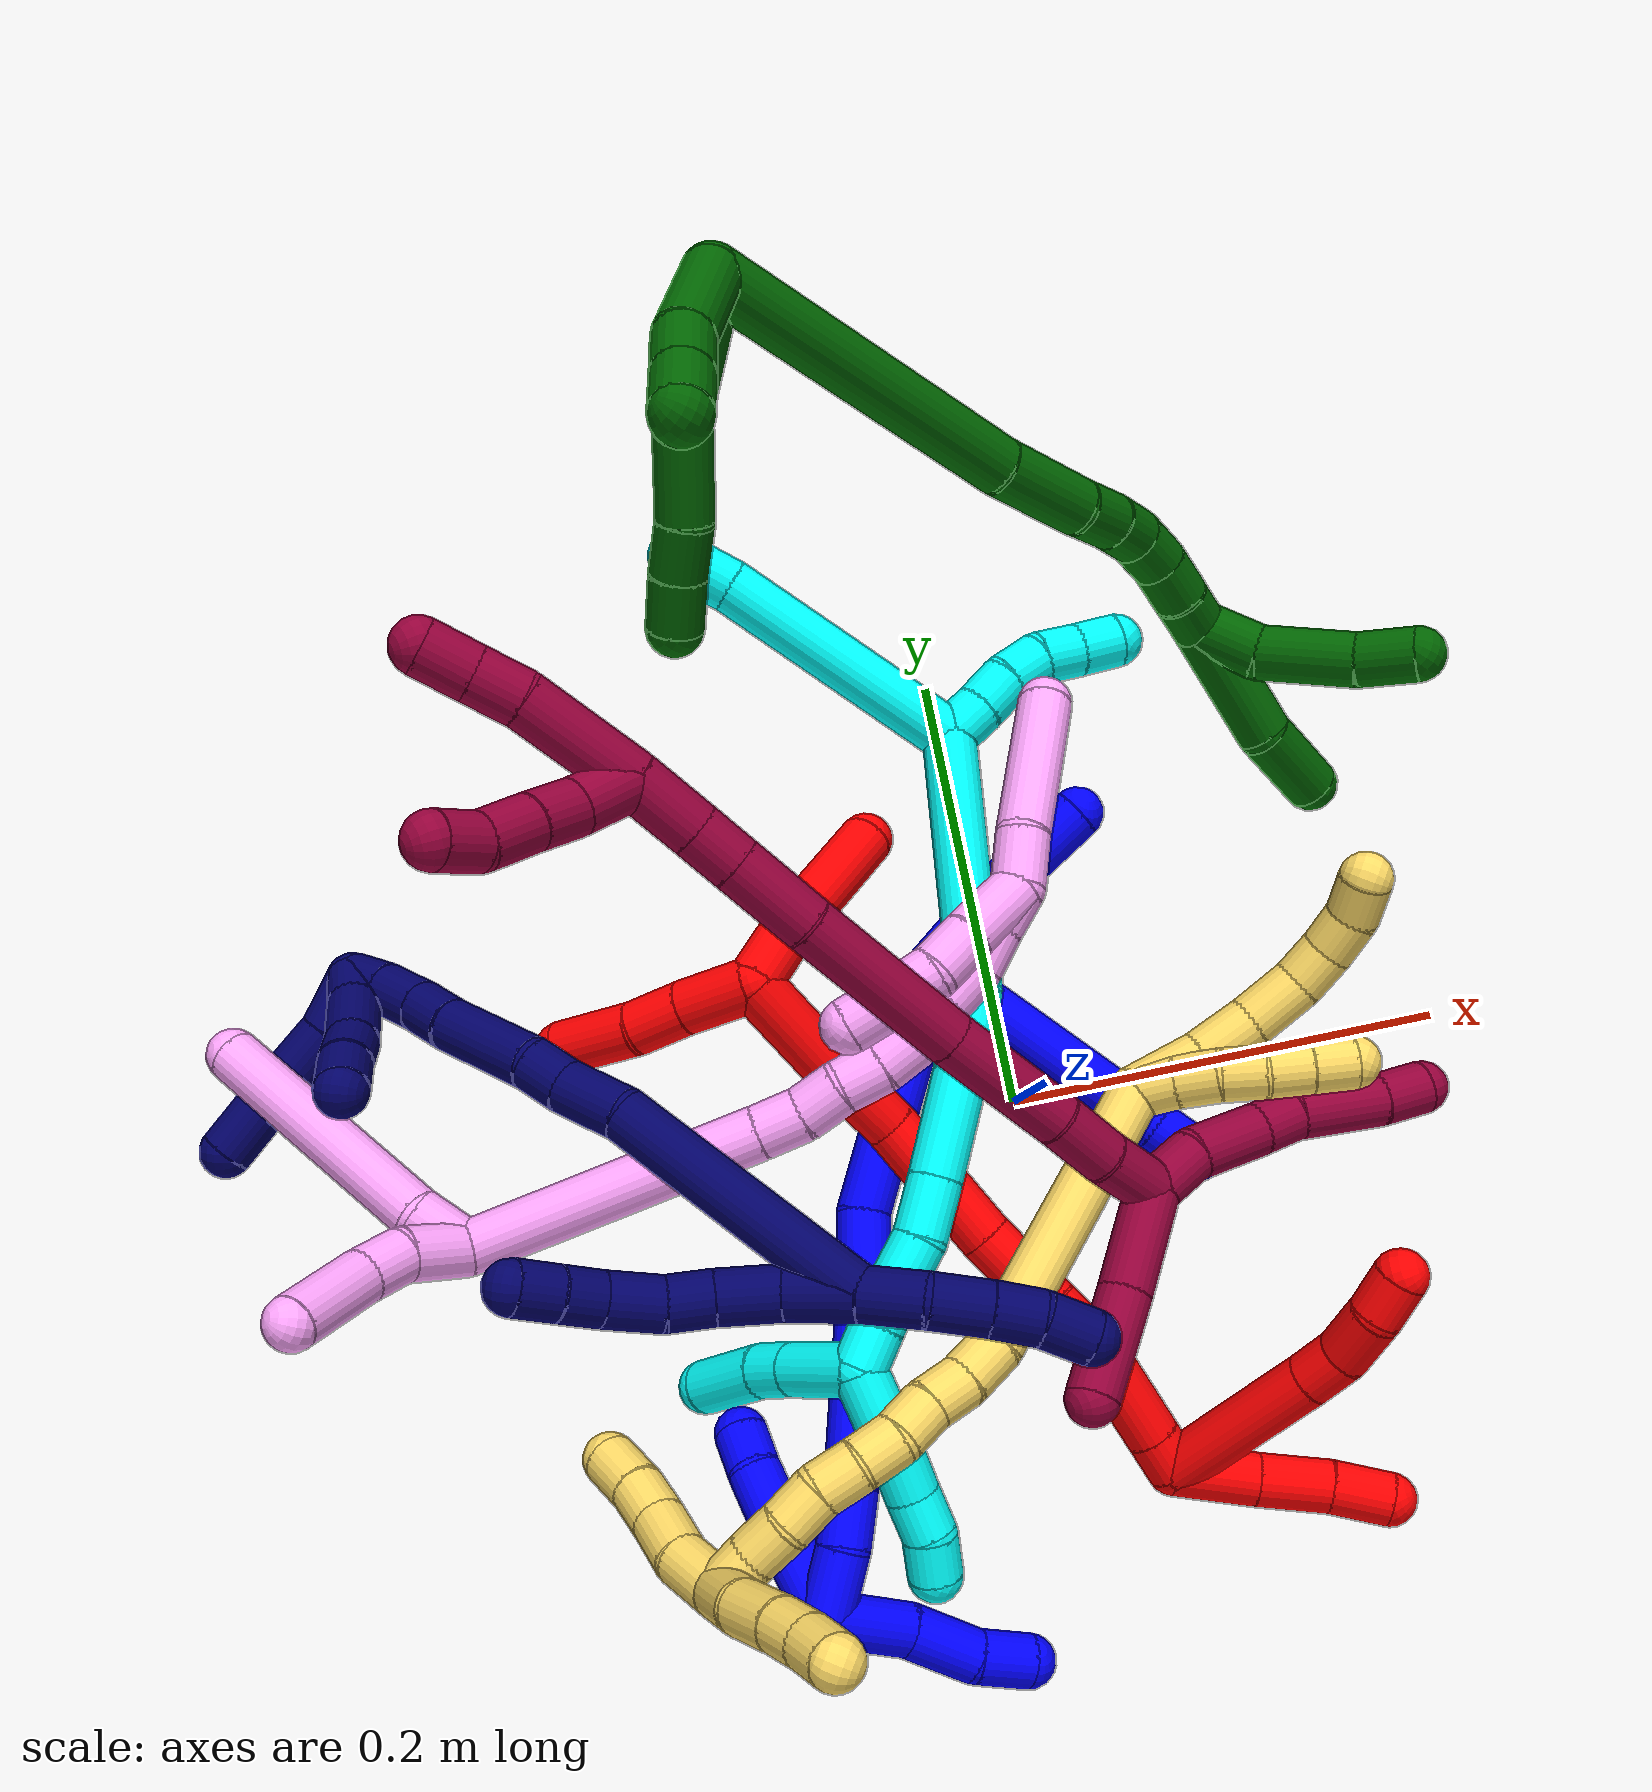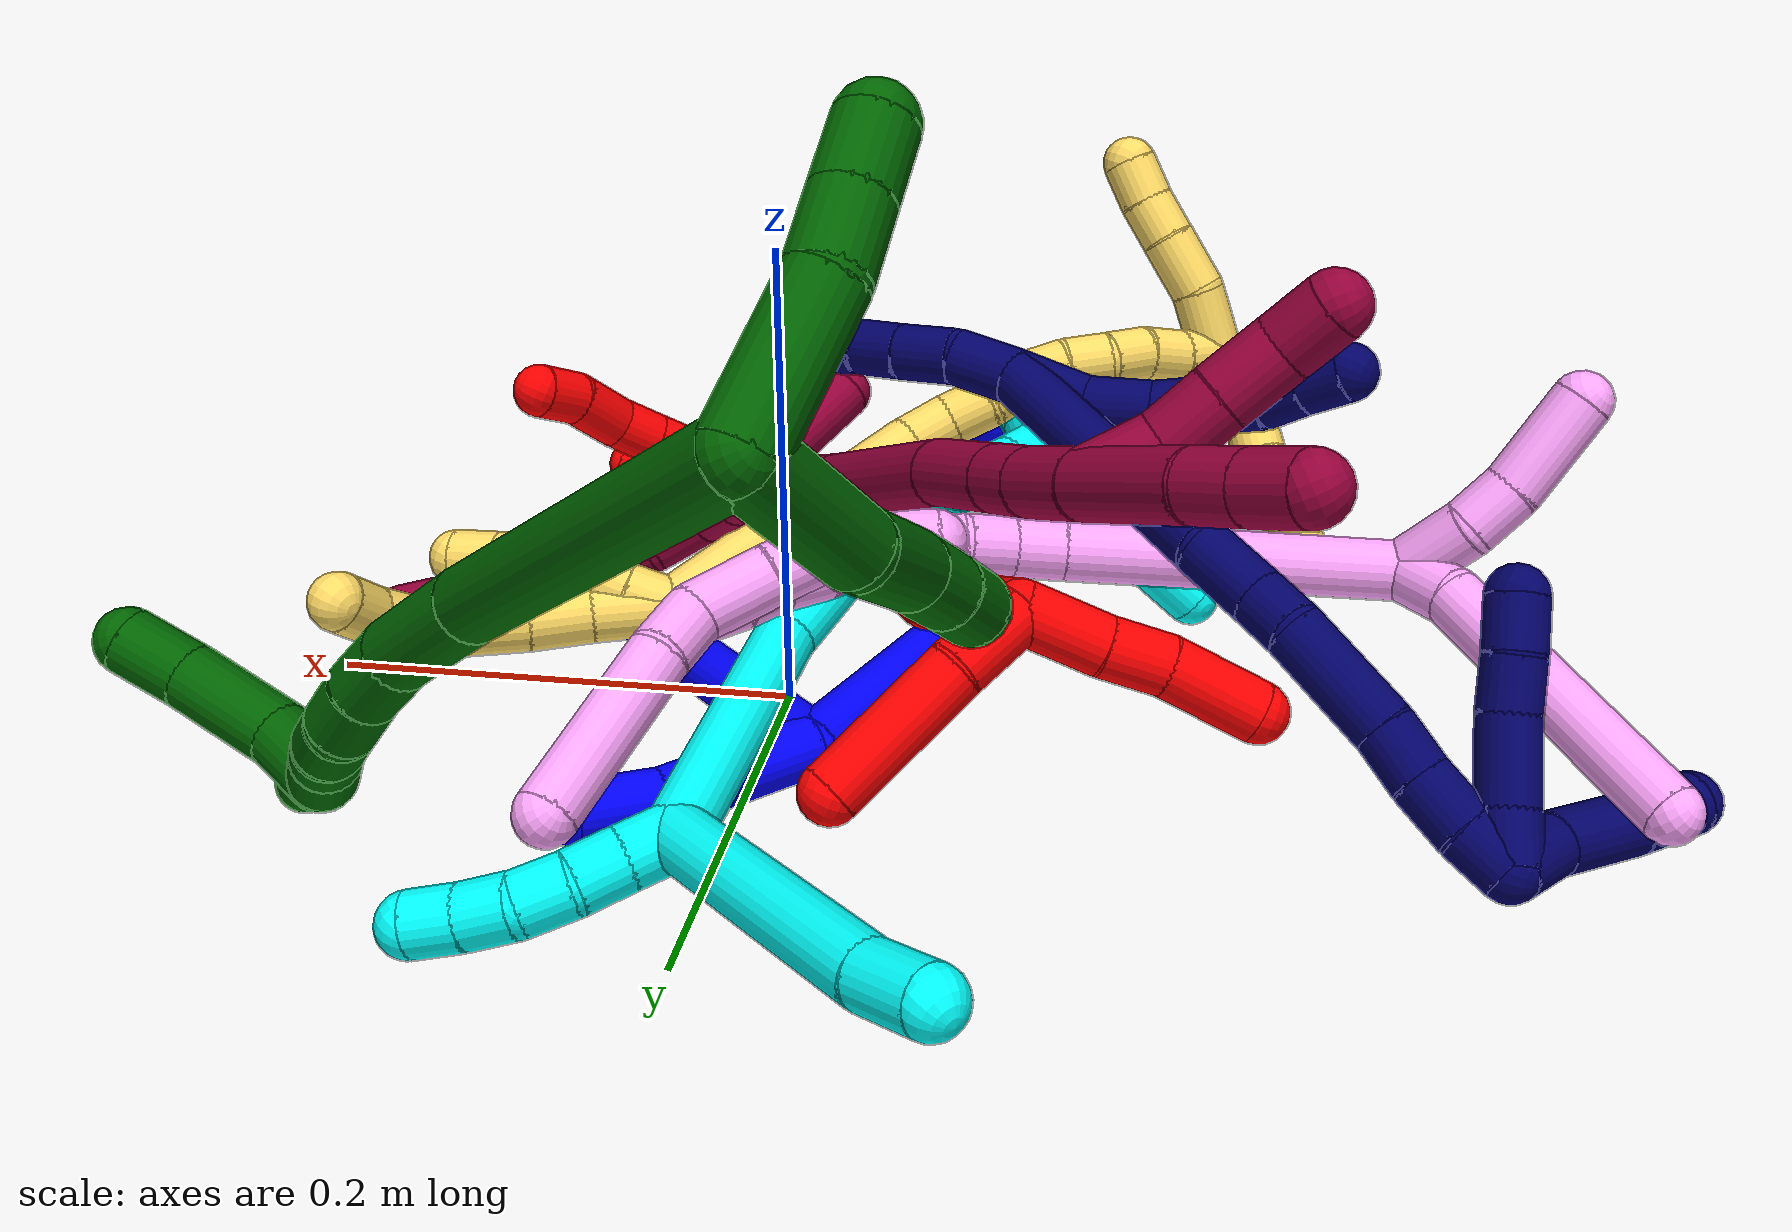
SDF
<sdf version="1.7">
 <world name="default">
  <plugin name="TubeGeneratorPlugin" filename="libtube_generator_plugin.so"/>
  <model name="photoneo_s_sensor">
   <static>1</static>
   <pose>0 0 2 1.57079 1.57079 3.14159</pose>
   <link name="link">
    <inertial><mass>0.1</mass></inertial>
    <sensor name="sensor" type="depth">
     <update_rate>30</update_rate>
     <camera>
      <horizontal_fov>1.22</horizontal_fov>
      <image><width>1920</width><height>1200</height><format>B8G8R8</format></image>
      <clip><near>0.1</near><far>4</far></clip>
      <depth_camera><output>points</output></depth_camera>
     </camera>
     <plugin name="camera_plugin" filename="libgazebo_ros_depth_camera.so">
      <baseline>0.2</baseline>
      <alwaysOn>1</alwaysOn>
      <updateRate>0.0</updateRate>
      <cameraName>camera_ir</cameraName>
      <imageTopicName>/camera/color/image_raw</imageTopicName>
      <cameraInfoTopicName>/camera/color/camera_info</cameraInfoTopicName>
      <depthImageTopicName>/camera/depth/image_raw</depthImageTopicName>
      <depthImageCameraInfoTopicName>/camera/depth/camera_info</depthImageCameraInfoTopicName>
      <pointCloudTopicName>/camera/depth/points</pointCloudTopicName>
      <frameName>fr_optical</frameName>
      <pointCloudCutoff>0.1</pointCloudCutoff>
      <pointCloudCutoffMax>2.0</pointCloudCutoffMax>
      <distortionK1>0</distortionK1>
      <distortionK2>0</distortionK2>
      <distortionK3>0</distortionK3>
      <distortionT1>0</distortionT1>
      <distortionT2>0</distortionT2>
      <CxPrime>0</CxPrime>
      <Cx>0</Cx>
      <Cy>0</Cy>
      <focalLength>0</focalLength>
      <hackBaseline>0</hackBaseline>
     </plugin>
    </sensor>
   </link>
  </model>
  <gravity>0 0 -9.8</gravity>
  <magnetic_field>6e-06 2.3e-05 -4.2e-05</magnetic_field>
  <atmosphere type="adiabatic"/>
  <physics name="default_physics" default="0" type="ode">
   <max_step_size>0.003</max_step_size>
   <real_time_factor>1</real_time_factor>
   <real_time_update_rate>1000</real_time_update_rate>
   <max_contacts>10000</max_contacts>
   <ode>
    <solver>
     <type>quick</type>
     <iters>100</iters>
     <sor>1.3</sor>
     <use_dynamic_moi_rescaling>0</use_dynamic_moi_rescaling>
    </solver>
    <constraints>
     <contact_max_correcting_vel>0</contact_max_correcting_vel>
     <contact_surface_layer>0.001</contact_surface_layer>
     <cfm>0</cfm>
     <erp>0.2</erp>
    </constraints>
   </ode>
  </physics>
  <scene><ambient>0.4 0.4 0.4 1</ambient><background>0.7 0.7 0.7 1</background><shadows>0</shadows></scene>
  <audio><device>default</device></audio>
  <spherical_coordinates>
   <surface_model>EARTH_WGS84</surface_model>
   <latitude_deg>0</latitude_deg>
   <longitude_deg>0</longitude_deg>
   <elevation>0</elevation>
   <heading_deg>0</heading_deg>
  </spherical_coordinates>
  <model name="bin">
   <static>1</static>
   <link name="bottom">
    <collision name="collision-bottom">
     <pose>0 0 -0.01 0 -0 0</pose>
     <geometry><box><size>0.8 0.6 0.02</size></box></geometry>
     <surface>
      <friction><ode><mu>100</mu><mu2>100</mu2></ode></friction>
      <contact><collide_bitmask>65535</collide_bitmask></contact>
     </surface>
    </collision>
   </link>
   <link name="west_wall">
    <collision name="collision-west_wall">
     <pose>-0.41 0 0.1 0 -0 0</pose>
     <geometry><box><size>0.02 0.6 0.2</size></box></geometry>
     <surface>
      <friction><ode><mu>100</mu><mu2>100</mu2></ode></friction>
      <contact><collide_bitmask>65535</collide_bitmask></contact>
     </surface>
    </collision>
   </link>
   <link name="east_wall">
    <collision name="collision-east_wall">
     <pose>0.41 0 0.1 0 -0 0</pose>
     <geometry><box><size>0.02 0.6 0.2</size></box></geometry>
     <surface>
      <friction><ode><mu>100</mu><mu2>100</mu2></ode></friction>
      <contact><collide_bitmask>65535</collide_bitmask></contact>
     </surface>
    </collision>
   </link>
   <link name="south_wall">
    <collision name="collision-south_wall">
     <pose>0 -0.31 0.1 0 -0 0</pose>
     <geometry><box><size>0.8 0.02 0.2</size></box></geometry>
     <surface>
      <friction><ode><mu>100</mu><mu2>100</mu2></ode></friction>
      <contact><collide_bitmask>65535</collide_bitmask></contact>
     </surface>
    </collision>
   </link>
   <link name="north_wall">
    <collision name="collision-north_wall">
     <pose>0 0.31 0.1 0 -0 0</pose>
     <geometry><box><size>0.8 0.02 0.2</size></box></geometry>
     <surface>
      <friction><ode><mu>100</mu><mu2>100</mu2></ode></friction>
      <contact><collide_bitmask>65535</collide_bitmask></contact>
     </surface>
    </collision>
   </link>
  </model>
  <model name="1">
   <static>0</static>
   <link name="1">
    <collision name="collision-cylinder-e_1_2_8">
     <pose>0.039285 -0.049537 -0.003282 1.63696 0.669416 0.711576</pose>
     <geometry><cylinder><radius>0.0125</radius><length>0.126618</length></cylinder></geometry>
     <surface>
      <friction><ode><mu>1.16</mu><mu2>1.16</mu2><slip1>0</slip1><slip2>0</slip2></ode></friction>
      <contact><ode><kp>1e+06</kp><kd>1</kd><max_vel>0</max_vel><min_depth>0.001</min_depth></ode></contact>
     </surface>
    </collision>
    <visual name="visual-cylinder-e_1_2_8">
     <pose>0.039285 -0.049537 -0.003282 1.63696 0.669416 0.711576</pose>
     <geometry><cylinder><radius>0.0125</radius><length>0.126618</length></cylinder></geometry>
     <material><ambient>0 0 1 1</ambient></material>
    </visual>
    <collision name="collision-cylinder-e_2_8_6">
     <pose>0.085212 -0.108691 -0.006281 1.54134 0.604223 0.587687</pose>
     <geometry><cylinder><radius>0.0125</radius><length>0.023382</length></cylinder></geometry>
     <surface>
      <friction><ode><mu>1.16</mu><mu2>1.16</mu2><slip1>0</slip1><slip2>0</slip2></ode></friction>
      <contact><ode><kp>1e+06</kp><kd>1</kd><max_vel>0</max_vel><min_depth>0.001</min_depth></ode></contact>
     </surface>
    </collision>
    <visual name="visual-cylinder-e_2_8_6">
     <pose>0.085212 -0.108691 -0.006281 1.54134 0.604223 0.587687</pose>
     <geometry><cylinder><radius>0.0125</radius><length>0.023382</length></cylinder></geometry>
     <material><ambient>0 0 1 1</ambient></material>
    </visual>
    <collision name="collision-cylinder-e_1_2_9">
     <pose>0.022949 0.012928 0.019539 -0.584514 0.775065 -0.244393</pose>
     <geometry><cylinder><radius>0.0125</radius><length>0.065592</length></cylinder></geometry>
     <surface>
      <friction><ode><mu>1.16</mu><mu2>1.16</mu2><slip1>0</slip1><slip2>0</slip2></ode></friction>
      <contact><ode><kp>1e+06</kp><kd>1</kd><max_vel>0</max_vel><min_depth>0.001</min_depth></ode></contact>
     </surface>
    </collision>
    <visual name="visual-cylinder-e_1_2_9">
     <pose>0.022949 0.012928 0.019539 -0.584514 0.775065 -0.244393</pose>
     <geometry><cylinder><radius>0.0125</radius><length>0.065592</length></cylinder></geometry>
     <material><ambient>0 0 1 1</ambient></material>
    </visual>
    <collision name="collision-cylinder-e_2_9_5">
     <pose>0.057638 0.030031 0.050942 -0.338395 0.750955 -0.134472</pose>
     <geometry><cylinder><radius>0.0125</radius><length>0.034408</length></cylinder></geometry>
     <surface>
      <friction><ode><mu>1.16</mu><mu2>1.16</mu2><slip1>0</slip1><slip2>0</slip2></ode></friction>
      <contact><ode><kp>1e+06</kp><kd>1</kd><max_vel>0</max_vel><min_depth>0.001</min_depth></ode></contact>
     </surface>
    </collision>
    <visual name="visual-cylinder-e_2_9_5">
     <pose>0.057638 0.030031 0.050942 -0.338395 0.750955 -0.134472</pose>
     <geometry><cylinder><radius>0.0125</radius><length>0.034408</length></cylinder></geometry>
     <material><ambient>0 0 1 1</ambient></material>
    </visual>
    <collision name="collision-cylinder-e_1_2_10">
     <pose>-0.02533 -0.042825 -0.032523 2.22031 -0.440211 -0.847108</pose>
     <geometry><cylinder><radius>0.0125</radius><length>0.118883</length></cylinder></geometry>
     <surface>
      <friction><ode><mu>1.16</mu><mu2>1.16</mu2><slip1>0</slip1><slip2>0</slip2></ode></friction>
      <contact><ode><kp>1e+06</kp><kd>1</kd><max_vel>0</max_vel><min_depth>0.001</min_depth></ode></contact>
     </surface>
    </collision>
    <visual name="visual-cylinder-e_1_2_10">
     <pose>-0.02533 -0.042825 -0.032523 2.22031 -0.440211 -0.847108</pose>
     <geometry><cylinder><radius>0.0125</radius><length>0.118883</length></cylinder></geometry>
     <material><ambient>0 0 1 1</ambient></material>
    </visual>
    <collision name="collision-cylinder-e_2_10_11">
     <pose>-0.054506 -0.098917 -0.070064 1.93245 -0.264802 -0.380872</pose>
     <geometry><cylinder><radius>0.0125</radius><length>0.029395</length></cylinder></geometry>
     <surface>
      <friction><ode><mu>1.16</mu><mu2>1.16</mu2><slip1>0</slip1><slip2>0</slip2></ode></friction>
      <contact><ode><kp>1e+06</kp><kd>1</kd><max_vel>0</max_vel><min_depth>0.001</min_depth></ode></contact>
     </surface>
    </collision>
    <visual name="visual-cylinder-e_2_10_11">
     <pose>-0.054506 -0.098917 -0.070064 1.93245 -0.264802 -0.380872</pose>
     <geometry><cylinder><radius>0.0125</radius><length>0.029395</length></cylinder></geometry>
     <material><ambient>0 0 1 1</ambient></material>
    </visual>
    <collision name="collision-cylinder-e_3_11_12">
     <pose>-0.07233 -0.152474 -0.09534 2.03667 -0.300567 -0.481707</pose>
     <geometry><cylinder><radius>0.0125</radius><length>0.094423</length></cylinder></geometry>
     <surface>
      <friction><ode><mu>1.16</mu><mu2>1.16</mu2><slip1>0</slip1><slip2>0</slip2></ode></friction>
      <contact><ode><kp>1e+06</kp><kd>1</kd><max_vel>0</max_vel><min_depth>0.001</min_depth></ode></contact>
     </surface>
    </collision>
    <visual name="visual-cylinder-e_3_11_12">
     <pose>-0.07233 -0.152474 -0.09534 2.03667 -0.300567 -0.481707</pose>
     <geometry><cylinder><radius>0.0125</radius><length>0.094423</length></cylinder></geometry>
     <material><ambient>0 0 1 1</ambient></material>
    </visual>
    <collision name="collision-cylinder-e_4_12_13">
     <pose>-0.090992 -0.203698 -0.121477 2.06418 -0.3608 -0.592361</pose>
     <geometry><cylinder><radius>0.0125</radius><length>0.026538</length></cylinder></geometry>
     <surface>
      <friction><ode><mu>1.16</mu><mu2>1.16</mu2><slip1>0</slip1><slip2>0</slip2></ode></friction>
      <contact><ode><kp>1e+06</kp><kd>1</kd><max_vel>0</max_vel><min_depth>0.001</min_depth></ode></contact>
     </surface>
    </collision>
    <visual name="visual-cylinder-e_4_12_13">
     <pose>-0.090992 -0.203698 -0.121477 2.06418 -0.3608 -0.592361</pose>
     <geometry><cylinder><radius>0.0125</radius><length>0.026538</length></cylinder></geometry>
     <material><ambient>0 0 1 1</ambient></material>
    </visual>
    <collision name="collision-cylinder-e_5_13_1">
     <pose>-0.101262 -0.225487 -0.136711 2.28208 -0.371693 -0.778578</pose>
     <geometry><cylinder><radius>0.0125</radius><length>0.030761</length></cylinder></geometry>
     <surface>
      <friction><ode><mu>1.16</mu><mu2>1.16</mu2><slip1>0</slip1><slip2>0</slip2></ode></friction>
      <contact><ode><kp>1e+06</kp><kd>1</kd><max_vel>0</max_vel><min_depth>0.001</min_depth></ode></contact>
     </surface>
    </collision>
    <visual name="visual-cylinder-e_5_13_1">
     <pose>-0.101262 -0.225487 -0.136711 2.28208 -0.371693 -0.778578</pose>
     <geometry><cylinder><radius>0.0125</radius><length>0.030761</length></cylinder></geometry>
     <material><ambient>0 0 1 1</ambient></material>
    </visual>
    <collision name="collision-cylinder-e_1_1_14">
     <pose>-0.10546 -0.211089 -0.150861 -1.75844 0.053956 -0.065159</pose>
     <geometry><cylinder><radius>0.0125</radius><length>0.051483</length></cylinder></geometry>
     <surface>
      <friction><ode><mu>1.16</mu><mu2>1.16</mu2><slip1>0</slip1><slip2>0</slip2></ode></friction>
      <contact><ode><kp>1e+06</kp><kd>1</kd><max_vel>0</max_vel><min_depth>0.001</min_depth></ode></contact>
     </surface>
    </collision>
    <visual name="visual-cylinder-e_1_1_14">
     <pose>-0.10546 -0.211089 -0.150861 -1.75844 0.053956 -0.065159</pose>
     <geometry><cylinder><radius>0.0125</radius><length>0.051483</length></cylinder></geometry>
     <material><ambient>0 0 1 1</ambient></material>
    </visual>
    <collision name="collision-cylinder-e_2_14_15">
     <pose>-0.104244 -0.171674 -0.155424 -1.5544 -0.012131 0.011934</pose>
     <geometry><cylinder><radius>0.0125</radius><length>0.02833</length></cylinder></geometry>
     <surface>
      <friction><ode><mu>1.16</mu><mu2>1.16</mu2><slip1>0</slip1><slip2>0</slip2></ode></friction>
      <contact><ode><kp>1e+06</kp><kd>1</kd><max_vel>0</max_vel><min_depth>0.001</min_depth></ode></contact>
     </surface>
    </collision>
    <visual name="visual-cylinder-e_2_14_15">
     <pose>-0.104244 -0.171674 -0.155424 -1.5544 -0.012131 0.011934</pose>
     <geometry><cylinder><radius>0.0125</radius><length>0.02833</length></cylinder></geometry>
     <material><ambient>0 0 1 1</ambient></material>
    </visual>
    <collision name="collision-cylinder-e_3_15_4">
     <pose>-0.103093 -0.147567 -0.156293 -1.68102 0.131452 -0.146751</pose>
     <geometry><cylinder><radius>0.0125</radius><length>0.020187</length></cylinder></geometry>
     <surface>
      <friction><ode><mu>1.16</mu><mu2>1.16</mu2><slip1>0</slip1><slip2>0</slip2></ode></friction>
      <contact><ode><kp>1e+06</kp><kd>1</kd><max_vel>0</max_vel><min_depth>0.001</min_depth></ode></contact>
     </surface>
    </collision>
    <visual name="visual-cylinder-e_3_15_4">
     <pose>-0.103093 -0.147567 -0.156293 -1.68102 0.131452 -0.146751</pose>
     <geometry><cylinder><radius>0.0125</radius><length>0.020187</length></cylinder></geometry>
     <material><ambient>0 0 1 1</ambient></material>
    </visual>
    <collision name="collision-cylinder-e_1_1_16">
     <pose>-0.087932 -0.243402 -0.147588 1.78307 1.20609 1.41229</pose>
     <geometry><cylinder><radius>0.0125</radius><length>0.040496</length></cylinder></geometry>
     <surface>
      <friction><ode><mu>1.16</mu><mu2>1.16</mu2><slip1>0</slip1><slip2>0</slip2></ode></friction>
      <contact><ode><kp>1e+06</kp><kd>1</kd><max_vel>0</max_vel><min_depth>0.001</min_depth></ode></contact>
     </surface>
    </collision>
    <visual name="visual-cylinder-e_1_1_16">
     <pose>-0.087932 -0.243402 -0.147588 1.78307 1.20609 1.41229</pose>
     <geometry><cylinder><radius>0.0125</radius><length>0.040496</length></cylinder></geometry>
     <material><ambient>0 0 1 1</ambient></material>
    </visual>
    <collision name="collision-cylinder-e_2_16_17">
     <pose>-0.055284 -0.260299 -0.149818 1.64271 0.947946 1.00761</pose>
     <geometry><cylinder><radius>0.0125</radius><length>0.033813</length></cylinder></geometry>
     <surface>
      <friction><ode><mu>1.16</mu><mu2>1.16</mu2><slip1>0</slip1><slip2>0</slip2></ode></friction>
      <contact><ode><kp>1e+06</kp><kd>1</kd><max_vel>0</max_vel><min_depth>0.001</min_depth></ode></contact>
     </surface>
    </collision>
    <visual name="visual-cylinder-e_2_16_17">
     <pose>-0.055284 -0.260299 -0.149818 1.64271 0.947946 1.00761</pose>
     <geometry><cylinder><radius>0.0125</radius><length>0.033813</length></cylinder></geometry>
     <material><ambient>0 0 1 1</ambient></material>
    </visual>
    <collision name="collision-cylinder-e_3_17_3">
     <pose>-0.029626 -0.274851 -0.149791 1.41602 1.19013 1.05041</pose>
     <geometry><cylinder><radius>0.0125</radius><length>0.025691</length></cylinder></geometry>
     <surface>
      <friction><ode><mu>1.16</mu><mu2>1.16</mu2><slip1>0</slip1><slip2>0</slip2></ode></friction>
      <contact><ode><kp>1e+06</kp><kd>1</kd><max_vel>0</max_vel><min_depth>0.001</min_depth></ode></contact>
     </surface>
    </collision>
    <visual name="visual-cylinder-e_3_17_3">
     <pose>-0.029626 -0.274851 -0.149791 1.41602 1.19013 1.05041</pose>
     <geometry><cylinder><radius>0.0125</radius><length>0.025691</length></cylinder></geometry>
     <material><ambient>0 0 1 1</ambient></material>
    </visual>
    <collision name="collision-sphere-3">
     <pose>-0.0177 -0.279567 -0.149055 0 -0 0</pose>
     <geometry><sphere><radius>0.0125</radius></sphere></geometry>
     <surface>
      <friction><ode><mu>1.16</mu><mu2>1.16</mu2><slip1>0</slip1><slip2>0</slip2></ode></friction>
      <contact><ode><kp>1e+06</kp><kd>1</kd><max_vel>0</max_vel><min_depth>0.001</min_depth></ode></contact>
     </surface>
    </collision>
    <visual name="visual-sphere-3">
     <pose>-0.0177 -0.279567 -0.149055 0 -0 0</pose>
     <geometry><sphere><radius>0.0125</radius></sphere></geometry>
     <material><ambient>0 0 1 1</ambient></material>
    </visual>
    <collision name="collision-sphere-17">
     <pose>-0.041552 -0.270136 -0.150526 0 -0 0</pose>
     <geometry><sphere><radius>0.0125</radius></sphere></geometry>
     <surface>
      <friction><ode><mu>1.16</mu><mu2>1.16</mu2><slip1>0</slip1><slip2>0</slip2></ode></friction>
      <contact><ode><kp>1e+06</kp><kd>1</kd><max_vel>0</max_vel><min_depth>0.001</min_depth></ode></contact>
     </surface>
    </collision>
    <visual name="visual-sphere-17">
     <pose>-0.041552 -0.270136 -0.150526 0 -0 0</pose>
     <geometry><sphere><radius>0.0125</radius></sphere></geometry>
     <material><ambient>0 0 1 1</ambient></material>
    </visual>
    <collision name="collision-sphere-16">
     <pose>-0.069016 -0.250462 -0.149109 0 -0 0</pose>
     <geometry><sphere><radius>0.0125</radius></sphere></geometry>
     <surface>
      <friction><ode><mu>1.16</mu><mu2>1.16</mu2><slip1>0</slip1><slip2>0</slip2></ode></friction>
      <contact><ode><kp>1e+06</kp><kd>1</kd><max_vel>0</max_vel><min_depth>0.001</min_depth></ode></contact>
     </surface>
    </collision>
    <visual name="visual-sphere-16">
     <pose>-0.069016 -0.250462 -0.149109 0 -0 0</pose>
     <geometry><sphere><radius>0.0125</radius></sphere></geometry>
     <material><ambient>0 0 1 1</ambient></material>
    </visual>
    <collision name="collision-sphere-4">
     <pose>-0.10177 -0.137621 -0.157393 0 -0 0</pose>
     <geometry><sphere><radius>0.0125</radius></sphere></geometry>
     <surface>
      <friction><ode><mu>1.16</mu><mu2>1.16</mu2><slip1>0</slip1><slip2>0</slip2></ode></friction>
      <contact><ode><kp>1e+06</kp><kd>1</kd><max_vel>0</max_vel><min_depth>0.001</min_depth></ode></contact>
     </surface>
    </collision>
    <visual name="visual-sphere-4">
     <pose>-0.10177 -0.137621 -0.157393 0 -0 0</pose>
     <geometry><sphere><radius>0.0125</radius></sphere></geometry>
     <material><ambient>0 0 1 1</ambient></material>
    </visual>
    <collision name="collision-sphere-15">
     <pose>-0.104416 -0.157513 -0.155192 0 -0 0</pose>
     <geometry><sphere><radius>0.0125</radius></sphere></geometry>
     <surface>
      <friction><ode><mu>1.16</mu><mu2>1.16</mu2><slip1>0</slip1><slip2>0</slip2></ode></friction>
      <contact><ode><kp>1e+06</kp><kd>1</kd><max_vel>0</max_vel><min_depth>0.001</min_depth></ode></contact>
     </surface>
    </collision>
    <visual name="visual-sphere-15">
     <pose>-0.104416 -0.157513 -0.155192 0 -0 0</pose>
     <geometry><sphere><radius>0.0125</radius></sphere></geometry>
     <material><ambient>0 0 1 1</ambient></material>
    </visual>
    <collision name="collision-sphere-14">
     <pose>-0.104072 -0.185836 -0.155656 0 -0 0</pose>
     <geometry><sphere><radius>0.0125</radius></sphere></geometry>
     <surface>
      <friction><ode><mu>1.16</mu><mu2>1.16</mu2><slip1>0</slip1><slip2>0</slip2></ode></friction>
      <contact><ode><kp>1e+06</kp><kd>1</kd><max_vel>0</max_vel><min_depth>0.001</min_depth></ode></contact>
     </surface>
    </collision>
    <visual name="visual-sphere-14">
     <pose>-0.104072 -0.185836 -0.155656 0 -0 0</pose>
     <geometry><sphere><radius>0.0125</radius></sphere></geometry>
     <material><ambient>0 0 1 1</ambient></material>
    </visual>
    <collision name="collision-sphere-1">
     <pose>-0.106849 -0.236342 -0.146066 0 -0 0</pose>
     <geometry><sphere><radius>0.0125</radius></sphere></geometry>
     <surface>
      <friction><ode><mu>1.16</mu><mu2>1.16</mu2><slip1>0</slip1><slip2>0</slip2></ode></friction>
      <contact><ode><kp>1e+06</kp><kd>1</kd><max_vel>0</max_vel><min_depth>0.001</min_depth></ode></contact>
     </surface>
    </collision>
    <visual name="visual-sphere-1">
     <pose>-0.106849 -0.236342 -0.146066 0 -0 0</pose>
     <geometry><sphere><radius>0.0125</radius></sphere></geometry>
     <material><ambient>0 0 1 1</ambient></material>
    </visual>
    <collision name="collision-sphere-13">
     <pose>-0.095676 -0.214632 -0.127357 0 -0 0</pose>
     <geometry><sphere><radius>0.0125</radius></sphere></geometry>
     <surface>
      <friction><ode><mu>1.16</mu><mu2>1.16</mu2><slip1>0</slip1><slip2>0</slip2></ode></friction>
      <contact><ode><kp>1e+06</kp><kd>1</kd><max_vel>0</max_vel><min_depth>0.001</min_depth></ode></contact>
     </surface>
    </collision>
    <visual name="visual-sphere-13">
     <pose>-0.095676 -0.214632 -0.127357 0 -0 0</pose>
     <geometry><sphere><radius>0.0125</radius></sphere></geometry>
     <material><ambient>0 0 1 1</ambient></material>
    </visual>
    <collision name="collision-sphere-12">
     <pose>-0.086308 -0.192763 -0.115597 0 -0 0</pose>
     <geometry><sphere><radius>0.0125</radius></sphere></geometry>
     <surface>
      <friction><ode><mu>1.16</mu><mu2>1.16</mu2><slip1>0</slip1><slip2>0</slip2></ode></friction>
      <contact><ode><kp>1e+06</kp><kd>1</kd><max_vel>0</max_vel><min_depth>0.001</min_depth></ode></contact>
     </surface>
    </collision>
    <visual name="visual-sphere-12">
     <pose>-0.086308 -0.192763 -0.115597 0 -0 0</pose>
     <geometry><sphere><radius>0.0125</radius></sphere></geometry>
     <material><ambient>0 0 1 1</ambient></material>
    </visual>
    <collision name="collision-sphere-11">
     <pose>-0.058353 -0.112185 -0.075083 0 -0 0</pose>
     <geometry><sphere><radius>0.0125</radius></sphere></geometry>
     <surface>
      <friction><ode><mu>1.16</mu><mu2>1.16</mu2><slip1>0</slip1><slip2>0</slip2></ode></friction>
      <contact><ode><kp>1e+06</kp><kd>1</kd><max_vel>0</max_vel><min_depth>0.001</min_depth></ode></contact>
     </surface>
    </collision>
    <visual name="visual-sphere-11">
     <pose>-0.058353 -0.112185 -0.075083 0 -0 0</pose>
     <geometry><sphere><radius>0.0125</radius></sphere></geometry>
     <material><ambient>0 0 1 1</ambient></material>
    </visual>
    <collision name="collision-sphere-8">
     <pose>0.07857 -0.099074 -0.006565 0 -0 0</pose>
     <geometry><sphere><radius>0.0125</radius></sphere></geometry>
     <surface>
      <friction><ode><mu>1.16</mu><mu2>1.16</mu2><slip1>0</slip1><slip2>0</slip2></ode></friction>
      <contact><ode><kp>1e+06</kp><kd>1</kd><max_vel>0</max_vel><min_depth>0.001</min_depth></ode></contact>
     </surface>
    </collision>
    <visual name="visual-sphere-8">
     <pose>0.07857 -0.099074 -0.006565 0 -0 0</pose>
     <geometry><sphere><radius>0.0125</radius></sphere></geometry>
     <material><ambient>0 0 1 1</ambient></material>
    </visual>
    <collision name="collision-sphere-2">
     <geometry><sphere><radius>0.0125</radius></sphere></geometry>
     <surface>
      <friction><ode><mu>1.16</mu><mu2>1.16</mu2><slip1>0</slip1><slip2>0</slip2></ode></friction>
      <contact><ode><kp>1e+06</kp><kd>1</kd><max_vel>0</max_vel><min_depth>0.001</min_depth></ode></contact>
     </surface>
    </collision>
    <visual name="visual-sphere-2">
     <geometry><sphere><radius>0.0125</radius></sphere></geometry>
     <material><ambient>0 0 1 1</ambient></material>
    </visual>
    <collision name="collision-sphere-9">
     <pose>0.045899 0.025856 0.039078 0 -0 0</pose>
     <geometry><sphere><radius>0.0125</radius></sphere></geometry>
     <surface>
      <friction><ode><mu>1.16</mu><mu2>1.16</mu2><slip1>0</slip1><slip2>0</slip2></ode></friction>
      <contact><ode><kp>1e+06</kp><kd>1</kd><max_vel>0</max_vel><min_depth>0.001</min_depth></ode></contact>
     </surface>
    </collision>
    <visual name="visual-sphere-9">
     <pose>0.045899 0.025856 0.039078 0 -0 0</pose>
     <geometry><sphere><radius>0.0125</radius></sphere></geometry>
     <material><ambient>0 0 1 1</ambient></material>
    </visual>
    <collision name="collision-sphere-6">
     <pose>0.091854 -0.118308 -0.005998 0 -0 0</pose>
     <geometry><sphere><radius>0.0125</radius></sphere></geometry>
     <surface>
      <friction><ode><mu>1.16</mu><mu2>1.16</mu2><slip1>0</slip1><slip2>0</slip2></ode></friction>
      <contact><ode><kp>1e+06</kp><kd>1</kd><max_vel>0</max_vel><min_depth>0.001</min_depth></ode></contact>
     </surface>
    </collision>
    <visual name="visual-sphere-6">
     <pose>0.091854 -0.118308 -0.005998 0 -0 0</pose>
     <geometry><sphere><radius>0.0125</radius></sphere></geometry>
     <material><ambient>0 0 1 1</ambient></material>
    </visual>
    <collision name="collision-sphere-5">
     <pose>0.069377 0.034206 0.062805 0 -0 0</pose>
     <geometry><sphere><radius>0.0125</radius></sphere></geometry>
     <surface>
      <friction><ode><mu>1.16</mu><mu2>1.16</mu2><slip1>0</slip1><slip2>0</slip2></ode></friction>
      <contact><ode><kp>1e+06</kp><kd>1</kd><max_vel>0</max_vel><min_depth>0.001</min_depth></ode></contact>
     </surface>
    </collision>
    <visual name="visual-sphere-5">
     <pose>0.069377 0.034206 0.062805 0 -0 0</pose>
     <geometry><sphere><radius>0.0125</radius></sphere></geometry>
     <material><ambient>0 0 1 1</ambient></material>
    </visual>
    <collision name="collision-sphere-10">
     <pose>-0.05066 -0.08565 -0.065045 0 -0 0</pose>
     <geometry><sphere><radius>0.0125</radius></sphere></geometry>
     <surface>
      <friction><ode><mu>1.16</mu><mu2>1.16</mu2><slip1>0</slip1><slip2>0</slip2></ode></friction>
      <contact><ode><kp>1e+06</kp><kd>1</kd><max_vel>0</max_vel><min_depth>0.001</min_depth></ode></contact>
     </surface>
    </collision>
    <visual name="visual-sphere-10">
     <pose>-0.05066 -0.08565 -0.065045 0 -0 0</pose>
     <geometry><sphere><radius>0.0125</radius></sphere></geometry>
     <material><ambient>0 0 1 1</ambient></material>
    </visual>
    <inertial>
     <pose>-0.030897 -0.1148 -0.066802 0 -0 0</pose>
     <mass>0.75</mass>
     <inertia>
      <ixx>0.000268</ixx>
      <ixy>0</ixy>
      <ixz>0</ixz>
      <iyy>-1.1e-05</iyy>
      <iyz>0</iyz>
      <izz>0.000224</izz>
     </inertia>
    </inertial>
   </link>
   <pose>-0.025145 0.068426 0.017543 -0.505327 0.560914 -0.034551</pose>
  </model>
  <model name="2">
   <static>0</static>
   <link name="2">
    <collision name="collision-cylinder-e_1_2_8">
     <pose>-0.010211 0.007007 0.038701 -0.179118 -0.254023 0.022934</pose>
     <geometry><cylinder><radius>0.0125</radius><length>0.081269</length></cylinder></geometry>
     <surface>
      <friction><ode><mu>1.16</mu><mu2>1.16</mu2><slip1>0</slip1><slip2>0</slip2></ode></friction>
      <contact><ode><kp>1e+06</kp><kd>1</kd><max_vel>0</max_vel><min_depth>0.001</min_depth></ode></contact>
     </surface>
    </collision>
    <visual name="visual-cylinder-e_1_2_8">
     <pose>-0.010211 0.007007 0.038701 -0.179118 -0.254023 0.022934</pose>
     <geometry><cylinder><radius>0.0125</radius><length>0.081269</length></cylinder></geometry>
     <material><ambient>1 0 0 1</ambient></material>
    </visual>
    <collision name="collision-cylinder-e_2_8_9">
     <pose>-0.023496 0.015931 0.087123 -0.19463 -0.30074 0.02958</pose>
     <geometry><cylinder><radius>0.0125</radius><length>0.020746</length></cylinder></geometry>
     <surface>
      <friction><ode><mu>1.16</mu><mu2>1.16</mu2><slip1>0</slip1><slip2>0</slip2></ode></friction>
      <contact><ode><kp>1e+06</kp><kd>1</kd><max_vel>0</max_vel><min_depth>0.001</min_depth></ode></contact>
     </surface>
    </collision>
    <visual name="visual-cylinder-e_2_8_9">
     <pose>-0.023496 0.015931 0.087123 -0.19463 -0.30074 0.02958</pose>
     <geometry><cylinder><radius>0.0125</radius><length>0.020746</length></cylinder></geometry>
     <material><ambient>1 0 0 1</ambient></material>
    </visual>
    <collision name="collision-cylinder-e_3_9_10">
     <pose>-0.033875 0.020971 0.107808 -0.277606 -0.569943 0.081804</pose>
     <geometry><cylinder><radius>0.0125</radius><length>0.027082</length></cylinder></geometry>
     <surface>
      <friction><ode><mu>1.16</mu><mu2>1.16</mu2><slip1>0</slip1><slip2>0</slip2></ode></friction>
      <contact><ode><kp>1e+06</kp><kd>1</kd><max_vel>0</max_vel><min_depth>0.001</min_depth></ode></contact>
     </surface>
    </collision>
    <visual name="visual-cylinder-e_3_9_10">
     <pose>-0.033875 0.020971 0.107808 -0.277606 -0.569943 0.081804</pose>
     <geometry><cylinder><radius>0.0125</radius><length>0.027082</length></cylinder></geometry>
     <material><ambient>1 0 0 1</ambient></material>
    </visual>
    <collision name="collision-cylinder-e_4_10_6">
     <pose>-0.045333 0.028934 0.127054 -0.528698 -0.408469 0.112012</pose>
     <geometry><cylinder><radius>0.0125</radius><length>0.020902</length></cylinder></geometry>
     <surface>
      <friction><ode><mu>1.16</mu><mu2>1.16</mu2><slip1>0</slip1><slip2>0</slip2></ode></friction>
      <contact><ode><kp>1e+06</kp><kd>1</kd><max_vel>0</max_vel><min_depth>0.001</min_depth></ode></contact>
     </surface>
    </collision>
    <visual name="visual-cylinder-e_4_10_6">
     <pose>-0.045333 0.028934 0.127054 -0.528698 -0.408469 0.112012</pose>
     <geometry><cylinder><radius>0.0125</radius><length>0.020902</length></cylinder></geometry>
     <material><ambient>1 0 0 1</ambient></material>
    </visual>
    <collision name="collision-cylinder-e_1_2_11">
     <pose>0.011241 -0.003033 0.015191 0.19705 0.627718 0.064146</pose>
     <geometry><cylinder><radius>0.0125</radius><length>0.038279</length></cylinder></geometry>
     <surface>
      <friction><ode><mu>1.16</mu><mu2>1.16</mu2><slip1>0</slip1><slip2>0</slip2></ode></friction>
      <contact><ode><kp>1e+06</kp><kd>1</kd><max_vel>0</max_vel><min_depth>0.001</min_depth></ode></contact>
     </surface>
    </collision>
    <visual name="visual-cylinder-e_1_2_11">
     <pose>0.011241 -0.003033 0.015191 0.19705 0.627718 0.064146</pose>
     <geometry><cylinder><radius>0.0125</radius><length>0.038279</length></cylinder></geometry>
     <material><ambient>1 0 0 1</ambient></material>
    </visual>
    <collision name="collision-cylinder-e_2_11_12">
     <pose>0.03178 -0.00846 0.04425 0.170962 0.583898 0.051495</pose>
     <geometry><cylinder><radius>0.0125</radius><length>0.033736</length></cylinder></geometry>
     <surface>
      <friction><ode><mu>1.16</mu><mu2>1.16</mu2><slip1>0</slip1><slip2>0</slip2></ode></friction>
      <contact><ode><kp>1e+06</kp><kd>1</kd><max_vel>0</max_vel><min_depth>0.001</min_depth></ode></contact>
     </surface>
    </collision>
    <visual name="visual-cylinder-e_2_11_12">
     <pose>0.03178 -0.00846 0.04425 0.170962 0.583898 0.051495</pose>
     <geometry><cylinder><radius>0.0125</radius><length>0.033736</length></cylinder></geometry>
     <material><ambient>1 0 0 1</ambient></material>
    </visual>
    <collision name="collision-cylinder-e_3_12_5">
     <pose>0.049031 -0.01435 0.069089 0.308505 0.604402 0.096871</pose>
     <geometry><cylinder><radius>0.0125</radius><length>0.027985</length></cylinder></geometry>
     <surface>
      <friction><ode><mu>1.16</mu><mu2>1.16</mu2><slip1>0</slip1><slip2>0</slip2></ode></friction>
      <contact><ode><kp>1e+06</kp><kd>1</kd><max_vel>0</max_vel><min_depth>0.001</min_depth></ode></contact>
     </surface>
    </collision>
    <visual name="visual-cylinder-e_3_12_5">
     <pose>0.049031 -0.01435 0.069089 0.308505 0.604402 0.096871</pose>
     <geometry><cylinder><radius>0.0125</radius><length>0.027985</length></cylinder></geometry>
     <material><ambient>1 0 0 1</ambient></material>
    </visual>
    <collision name="collision-cylinder-e_1_2_13">
     <pose>-0.00811 0.005865 -0.000915 -1.72556 -0.938977 1.06993</pose>
     <geometry><cylinder><radius>0.0125</radius><length>0.020099</length></cylinder></geometry>
     <surface>
      <friction><ode><mu>1.16</mu><mu2>1.16</mu2><slip1>0</slip1><slip2>0</slip2></ode></friction>
      <contact><ode><kp>1e+06</kp><kd>1</kd><max_vel>0</max_vel><min_depth>0.001</min_depth></ode></contact>
     </surface>
    </collision>
    <visual name="visual-cylinder-e_1_2_13">
     <pose>-0.00811 0.005865 -0.000915 -1.72556 -0.938977 1.06993</pose>
     <geometry><cylinder><radius>0.0125</radius><length>0.020099</length></cylinder></geometry>
     <material><ambient>1 0 0 1</ambient></material>
    </visual>
    <collision name="collision-cylinder-e_2_13_14">
     <pose>-0.036813 0.026699 -0.004241 -1.73046 -0.936111 1.07117</pose>
     <geometry><cylinder><radius>0.0125</radius><length>0.051148</length></cylinder></geometry>
     <surface>
      <friction><ode><mu>1.16</mu><mu2>1.16</mu2><slip1>0</slip1><slip2>0</slip2></ode></friction>
      <contact><ode><kp>1e+06</kp><kd>1</kd><max_vel>0</max_vel><min_depth>0.001</min_depth></ode></contact>
     </surface>
    </collision>
    <visual name="visual-cylinder-e_2_13_14">
     <pose>-0.036813 0.026699 -0.004241 -1.73046 -0.936111 1.07117</pose>
     <geometry><cylinder><radius>0.0125</radius><length>0.051148</length></cylinder></geometry>
     <material><ambient>1 0 0 1</ambient></material>
    </visual>
    <collision name="collision-cylinder-e_3_14_15">
     <pose>-0.068535 0.04959 -0.011306 -2.10212 -0.880703 1.3778</pose>
     <geometry><cylinder><radius>0.0125</radius><length>0.028862</length></cylinder></geometry>
     <surface>
      <friction><ode><mu>1.16</mu><mu2>1.16</mu2><slip1>0</slip1><slip2>0</slip2></ode></friction>
      <contact><ode><kp>1e+06</kp><kd>1</kd><max_vel>0</max_vel><min_depth>0.001</min_depth></ode></contact>
     </surface>
    </collision>
    <visual name="visual-cylinder-e_3_14_15">
     <pose>-0.068535 0.04959 -0.011306 -2.10212 -0.880703 1.3778</pose>
     <geometry><cylinder><radius>0.0125</radius><length>0.028862</length></cylinder></geometry>
     <material><ambient>1 0 0 1</ambient></material>
    </visual>
    <collision name="collision-cylinder-e_4_15_16">
     <pose>-0.093978 0.070754 -0.023628 -2.09556 -0.752009 1.20078</pose>
     <geometry><cylinder><radius>0.0125</radius><length>0.041907</length></cylinder></geometry>
     <surface>
      <friction><ode><mu>1.16</mu><mu2>1.16</mu2><slip1>0</slip1><slip2>0</slip2></ode></friction>
      <contact><ode><kp>1e+06</kp><kd>1</kd><max_vel>0</max_vel><min_depth>0.001</min_depth></ode></contact>
     </surface>
    </collision>
    <visual name="visual-cylinder-e_4_15_16">
     <pose>-0.093978 0.070754 -0.023628 -2.09556 -0.752009 1.20078</pose>
     <geometry><cylinder><radius>0.0125</radius><length>0.041907</length></cylinder></geometry>
     <material><ambient>1 0 0 1</ambient></material>
    </visual>
    <collision name="collision-cylinder-e_5_16_17">
     <pose>-0.132077 0.105125 -0.040507 -1.98198 -0.801147 1.14799</pose>
     <geometry><cylinder><radius>0.0125</radius><length>0.066242</length></cylinder></geometry>
     <surface>
      <friction><ode><mu>1.16</mu><mu2>1.16</mu2><slip1>0</slip1><slip2>0</slip2></ode></friction>
      <contact><ode><kp>1e+06</kp><kd>1</kd><max_vel>0</max_vel><min_depth>0.001</min_depth></ode></contact>
     </surface>
    </collision>
    <visual name="visual-cylinder-e_5_16_17">
     <pose>-0.132077 0.105125 -0.040507 -1.98198 -0.801147 1.14799</pose>
     <geometry><cylinder><radius>0.0125</radius><length>0.066242</length></cylinder></geometry>
     <material><ambient>1 0 0 1</ambient></material>
    </visual>
    <collision name="collision-cylinder-e_6_17_18">
     <pose>-0.17339 0.134585 -0.054449 -2.08711 -1.07051 1.58914</pose>
     <geometry><cylinder><radius>0.0125</radius><length>0.03995</length></cylinder></geometry>
     <surface>
      <friction><ode><mu>1.16</mu><mu2>1.16</mu2><slip1>0</slip1><slip2>0</slip2></ode></friction>
      <contact><ode><kp>1e+06</kp><kd>1</kd><max_vel>0</max_vel><min_depth>0.001</min_depth></ode></contact>
     </surface>
    </collision>
    <visual name="visual-cylinder-e_6_17_18">
     <pose>-0.17339 0.134585 -0.054449 -2.08711 -1.07051 1.58914</pose>
     <geometry><cylinder><radius>0.0125</radius><length>0.03995</length></cylinder></geometry>
     <material><ambient>1 0 0 1</ambient></material>
    </visual>
    <collision name="collision-cylinder-e_7_18_1">
     <pose>-0.213531 0.15446 -0.064277 -1.98665 -1.06187 1.46694</pose>
     <geometry><cylinder><radius>0.0125</radius><length>0.051792</length></cylinder></geometry>
     <surface>
      <friction><ode><mu>1.16</mu><mu2>1.16</mu2><slip1>0</slip1><slip2>0</slip2></ode></friction>
      <contact><ode><kp>1e+06</kp><kd>1</kd><max_vel>0</max_vel><min_depth>0.001</min_depth></ode></contact>
     </surface>
    </collision>
    <visual name="visual-cylinder-e_7_18_1">
     <pose>-0.213531 0.15446 -0.064277 -1.98665 -1.06187 1.46694</pose>
     <geometry><cylinder><radius>0.0125</radius><length>0.051792</length></cylinder></geometry>
     <material><ambient>1 0 0 1</ambient></material>
    </visual>
    <collision name="collision-cylinder-e_1_1_19">
     <pose>-0.236685 0.166477 -0.086709 -3.11416 -0.031092 1.69578</pose>
     <geometry><cylinder><radius>0.0125</radius><length>0.0347</length></cylinder></geometry>
     <surface>
      <friction><ode><mu>1.16</mu><mu2>1.16</mu2><slip1>0</slip1><slip2>0</slip2></ode></friction>
      <contact><ode><kp>1e+06</kp><kd>1</kd><max_vel>0</max_vel><min_depth>0.001</min_depth></ode></contact>
     </surface>
    </collision>
    <visual name="visual-cylinder-e_1_1_19">
     <pose>-0.236685 0.166477 -0.086709 -3.11416 -0.031092 1.69578</pose>
     <geometry><cylinder><radius>0.0125</radius><length>0.0347</length></cylinder></geometry>
     <material><ambient>1 0 0 1</ambient></material>
    </visual>
    <collision name="collision-cylinder-e_2_19_20">
     <pose>-0.238041 0.166026 -0.116963 3.06994 -0.062995 -1.44222</pose>
     <geometry><cylinder><radius>0.0125</radius><length>0.025955</length></cylinder></geometry>
     <surface>
      <friction><ode><mu>1.16</mu><mu2>1.16</mu2><slip1>0</slip1><slip2>0</slip2></ode></friction>
      <contact><ode><kp>1e+06</kp><kd>1</kd><max_vel>0</max_vel><min_depth>0.001</min_depth></ode></contact>
     </surface>
    </collision>
    <visual name="visual-cylinder-e_2_19_20">
     <pose>-0.238041 0.166026 -0.116963 3.06994 -0.062995 -1.44222</pose>
     <geometry><cylinder><radius>0.0125</radius><length>0.025955</length></cylinder></geometry>
     <material><ambient>1 0 0 1</ambient></material>
    </visual>
    <collision name="collision-cylinder-e_3_20_4">
     <pose>-0.239428 0.1672 -0.149433 -3.03451 -0.028946 0.527565</pose>
     <geometry><cylinder><radius>0.0125</radius><length>0.039345</length></cylinder></geometry>
     <surface>
      <friction><ode><mu>1.16</mu><mu2>1.16</mu2><slip1>0</slip1><slip2>0</slip2></ode></friction>
      <contact><ode><kp>1e+06</kp><kd>1</kd><max_vel>0</max_vel><min_depth>0.001</min_depth></ode></contact>
     </surface>
    </collision>
    <visual name="visual-cylinder-e_3_20_4">
     <pose>-0.239428 0.1672 -0.149433 -3.03451 -0.028946 0.527565</pose>
     <geometry><cylinder><radius>0.0125</radius><length>0.039345</length></cylinder></geometry>
     <material><ambient>1 0 0 1</ambient></material>
    </visual>
    <collision name="collision-cylinder-e_1_1_21">
     <pose>-0.231762 0.180939 -0.061259 -1.07314 0.25235 -0.150608</pose>
     <geometry><cylinder><radius>0.0125</radius><length>0.035111</length></cylinder></geometry>
     <surface>
      <friction><ode><mu>1.16</mu><mu2>1.16</mu2><slip1>0</slip1><slip2>0</slip2></ode></friction>
      <contact><ode><kp>1e+06</kp><kd>1</kd><max_vel>0</max_vel><min_depth>0.001</min_depth></ode></contact>
     </surface>
    </collision>
    <visual name="visual-cylinder-e_1_1_21">
     <pose>-0.231762 0.180939 -0.061259 -1.07314 0.25235 -0.150608</pose>
     <geometry><cylinder><radius>0.0125</radius><length>0.035111</length></cylinder></geometry>
     <material><ambient>1 0 0 1</ambient></material>
    </visual>
    <collision name="collision-cylinder-e_2_21_3">
     <pose>-0.214194 0.222387 -0.039878 -1.10682 0.418514 -0.260911</pose>
     <geometry><cylinder><radius>0.0125</radius><length>0.064889</length></cylinder></geometry>
     <surface>
      <friction><ode><mu>1.16</mu><mu2>1.16</mu2><slip1>0</slip1><slip2>0</slip2></ode></friction>
      <contact><ode><kp>1e+06</kp><kd>1</kd><max_vel>0</max_vel><min_depth>0.001</min_depth></ode></contact>
     </surface>
    </collision>
    <visual name="visual-cylinder-e_2_21_3">
     <pose>-0.214194 0.222387 -0.039878 -1.10682 0.418514 -0.260911</pose>
     <geometry><cylinder><radius>0.0125</radius><length>0.064889</length></cylinder></geometry>
     <material><ambient>1 0 0 1</ambient></material>
    </visual>
    <collision name="collision-sphere-3">
     <pose>-0.201008 0.248897 -0.026612 0 -0 0</pose>
     <geometry><sphere><radius>0.0125</radius></sphere></geometry>
     <surface>
      <friction><ode><mu>1.16</mu><mu2>1.16</mu2><slip1>0</slip1><slip2>0</slip2></ode></friction>
      <contact><ode><kp>1e+06</kp><kd>1</kd><max_vel>0</max_vel><min_depth>0.001</min_depth></ode></contact>
     </surface>
    </collision>
    <visual name="visual-sphere-3">
     <pose>-0.201008 0.248897 -0.026612 0 -0 0</pose>
     <geometry><sphere><radius>0.0125</radius></sphere></geometry>
     <material><ambient>1 0 0 1</ambient></material>
    </visual>
    <collision name="collision-sphere-21">
     <pose>-0.227379 0.195877 -0.053144 0 -0 0</pose>
     <geometry><sphere><radius>0.0125</radius></sphere></geometry>
     <surface>
      <friction><ode><mu>1.16</mu><mu2>1.16</mu2><slip1>0</slip1><slip2>0</slip2></ode></friction>
      <contact><ode><kp>1e+06</kp><kd>1</kd><max_vel>0</max_vel><min_depth>0.001</min_depth></ode></contact>
     </surface>
    </collision>
    <visual name="visual-sphere-21">
     <pose>-0.227379 0.195877 -0.053144 0 -0 0</pose>
     <geometry><sphere><radius>0.0125</radius></sphere></geometry>
     <material><ambient>1 0 0 1</ambient></material>
    </visual>
    <collision name="collision-sphere-4">
     <pose>-0.239997 0.169302 -0.168984 0 -0 0</pose>
     <geometry><sphere><radius>0.0125</radius></sphere></geometry>
     <surface>
      <friction><ode><mu>1.16</mu><mu2>1.16</mu2><slip1>0</slip1><slip2>0</slip2></ode></friction>
      <contact><ode><kp>1e+06</kp><kd>1</kd><max_vel>0</max_vel><min_depth>0.001</min_depth></ode></contact>
     </surface>
    </collision>
    <visual name="visual-sphere-4">
     <pose>-0.239997 0.169302 -0.168984 0 -0 0</pose>
     <geometry><sphere><radius>0.0125</radius></sphere></geometry>
     <material><ambient>1 0 0 1</ambient></material>
    </visual>
    <collision name="collision-sphere-20">
     <pose>-0.238858 0.165099 -0.129881 0 -0 0</pose>
     <geometry><sphere><radius>0.0125</radius></sphere></geometry>
     <surface>
      <friction><ode><mu>1.16</mu><mu2>1.16</mu2><slip1>0</slip1><slip2>0</slip2></ode></friction>
      <contact><ode><kp>1e+06</kp><kd>1</kd><max_vel>0</max_vel><min_depth>0.001</min_depth></ode></contact>
     </surface>
    </collision>
    <visual name="visual-sphere-20">
     <pose>-0.238858 0.165099 -0.129881 0 -0 0</pose>
     <geometry><sphere><radius>0.0125</radius></sphere></geometry>
     <material><ambient>1 0 0 1</ambient></material>
    </visual>
    <collision name="collision-sphere-11">
     <pose>0.022481 -0.006066 0.030382 0 -0 0</pose>
     <geometry><sphere><radius>0.0125</radius></sphere></geometry>
     <surface>
      <friction><ode><mu>1.16</mu><mu2>1.16</mu2><slip1>0</slip1><slip2>0</slip2></ode></friction>
      <contact><ode><kp>1e+06</kp><kd>1</kd><max_vel>0</max_vel><min_depth>0.001</min_depth></ode></contact>
     </surface>
    </collision>
    <visual name="visual-sphere-11">
     <pose>0.022481 -0.006066 0.030382 0 -0 0</pose>
     <geometry><sphere><radius>0.0125</radius></sphere></geometry>
     <material><ambient>1 0 0 1</ambient></material>
    </visual>
    <collision name="collision-sphere-6">
     <pose>-0.049484 0.033772 0.135336 0 -0 0</pose>
     <geometry><sphere><radius>0.0125</radius></sphere></geometry>
     <surface>
      <friction><ode><mu>1.16</mu><mu2>1.16</mu2><slip1>0</slip1><slip2>0</slip2></ode></friction>
      <contact><ode><kp>1e+06</kp><kd>1</kd><max_vel>0</max_vel><min_depth>0.001</min_depth></ode></contact>
     </surface>
    </collision>
    <visual name="visual-sphere-6">
     <pose>-0.049484 0.033772 0.135336 0 -0 0</pose>
     <geometry><sphere><radius>0.0125</radius></sphere></geometry>
     <material><ambient>1 0 0 1</ambient></material>
    </visual>
    <collision name="collision-sphere-10">
     <pose>-0.041182 0.024096 0.118772 0 -0 0</pose>
     <geometry><sphere><radius>0.0125</radius></sphere></geometry>
     <surface>
      <friction><ode><mu>1.16</mu><mu2>1.16</mu2><slip1>0</slip1><slip2>0</slip2></ode></friction>
      <contact><ode><kp>1e+06</kp><kd>1</kd><max_vel>0</max_vel><min_depth>0.001</min_depth></ode></contact>
     </surface>
    </collision>
    <visual name="visual-sphere-10">
     <pose>-0.041182 0.024096 0.118772 0 -0 0</pose>
     <geometry><sphere><radius>0.0125</radius></sphere></geometry>
     <material><ambient>1 0 0 1</ambient></material>
    </visual>
    <collision name="collision-sphere-9">
     <pose>-0.026569 0.017847 0.096844 0 -0 0</pose>
     <geometry><sphere><radius>0.0125</radius></sphere></geometry>
     <surface>
      <friction><ode><mu>1.16</mu><mu2>1.16</mu2><slip1>0</slip1><slip2>0</slip2></ode></friction>
      <contact><ode><kp>1e+06</kp><kd>1</kd><max_vel>0</max_vel><min_depth>0.001</min_depth></ode></contact>
     </surface>
    </collision>
    <visual name="visual-sphere-9">
     <pose>-0.026569 0.017847 0.096844 0 -0 0</pose>
     <geometry><sphere><radius>0.0125</radius></sphere></geometry>
     <material><ambient>1 0 0 1</ambient></material>
    </visual>
    <collision name="collision-sphere-2">
     <geometry><sphere><radius>0.0125</radius></sphere></geometry>
     <surface>
      <friction><ode><mu>1.16</mu><mu2>1.16</mu2><slip1>0</slip1><slip2>0</slip2></ode></friction>
      <contact><ode><kp>1e+06</kp><kd>1</kd><max_vel>0</max_vel><min_depth>0.001</min_depth></ode></contact>
     </surface>
    </collision>
    <visual name="visual-sphere-2">
     <geometry><sphere><radius>0.0125</radius></sphere></geometry>
     <material><ambient>1 0 0 1</ambient></material>
    </visual>
    <collision name="collision-sphere-19">
     <pose>-0.237224 0.166953 -0.104044 0 -0 0</pose>
     <geometry><sphere><radius>0.0125</radius></sphere></geometry>
     <surface>
      <friction><ode><mu>1.16</mu><mu2>1.16</mu2><slip1>0</slip1><slip2>0</slip2></ode></friction>
      <contact><ode><kp>1e+06</kp><kd>1</kd><max_vel>0</max_vel><min_depth>0.001</min_depth></ode></contact>
     </surface>
    </collision>
    <visual name="visual-sphere-19">
     <pose>-0.237224 0.166953 -0.104044 0 -0 0</pose>
     <geometry><sphere><radius>0.0125</radius></sphere></geometry>
     <material><ambient>1 0 0 1</ambient></material>
    </visual>
    <collision name="collision-sphere-8">
     <pose>-0.020423 0.014014 0.077402 0 -0 0</pose>
     <geometry><sphere><radius>0.0125</radius></sphere></geometry>
     <surface>
      <friction><ode><mu>1.16</mu><mu2>1.16</mu2><slip1>0</slip1><slip2>0</slip2></ode></friction>
      <contact><ode><kp>1e+06</kp><kd>1</kd><max_vel>0</max_vel><min_depth>0.001</min_depth></ode></contact>
     </surface>
    </collision>
    <visual name="visual-sphere-8">
     <pose>-0.020423 0.014014 0.077402 0 -0 0</pose>
     <geometry><sphere><radius>0.0125</radius></sphere></geometry>
     <material><ambient>1 0 0 1</ambient></material>
    </visual>
    <collision name="collision-sphere-12">
     <pose>0.041079 -0.010854 0.058118 0 -0 0</pose>
     <geometry><sphere><radius>0.0125</radius></sphere></geometry>
     <surface>
      <friction><ode><mu>1.16</mu><mu2>1.16</mu2><slip1>0</slip1><slip2>0</slip2></ode></friction>
      <contact><ode><kp>1e+06</kp><kd>1</kd><max_vel>0</max_vel><min_depth>0.001</min_depth></ode></contact>
     </surface>
    </collision>
    <visual name="visual-sphere-12">
     <pose>0.041079 -0.010854 0.058118 0 -0 0</pose>
     <geometry><sphere><radius>0.0125</radius></sphere></geometry>
     <material><ambient>1 0 0 1</ambient></material>
    </visual>
    <collision name="collision-sphere-5">
     <pose>0.056982 -0.017846 0.080059 0 -0 0</pose>
     <geometry><sphere><radius>0.0125</radius></sphere></geometry>
     <surface>
      <friction><ode><mu>1.16</mu><mu2>1.16</mu2><slip1>0</slip1><slip2>0</slip2></ode></friction>
      <contact><ode><kp>1e+06</kp><kd>1</kd><max_vel>0</max_vel><min_depth>0.001</min_depth></ode></contact>
     </surface>
    </collision>
    <visual name="visual-sphere-5">
     <pose>0.056982 -0.017846 0.080059 0 -0 0</pose>
     <geometry><sphere><radius>0.0125</radius></sphere></geometry>
     <material><ambient>1 0 0 1</ambient></material>
    </visual>
    <collision name="collision-sphere-13">
     <pose>-0.016219 0.011729 -0.00183 0 -0 0</pose>
     <geometry><sphere><radius>0.0125</radius></sphere></geometry>
     <surface>
      <friction><ode><mu>1.16</mu><mu2>1.16</mu2><slip1>0</slip1><slip2>0</slip2></ode></friction>
      <contact><ode><kp>1e+06</kp><kd>1</kd><max_vel>0</max_vel><min_depth>0.001</min_depth></ode></contact>
     </surface>
    </collision>
    <visual name="visual-sphere-13">
     <pose>-0.016219 0.011729 -0.00183 0 -0 0</pose>
     <geometry><sphere><radius>0.0125</radius></sphere></geometry>
     <material><ambient>1 0 0 1</ambient></material>
    </visual>
    <collision name="collision-sphere-14">
     <pose>-0.057406 0.04167 -0.006651 0 -0 0</pose>
     <geometry><sphere><radius>0.0125</radius></sphere></geometry>
     <surface>
      <friction><ode><mu>1.16</mu><mu2>1.16</mu2><slip1>0</slip1><slip2>0</slip2></ode></friction>
      <contact><ode><kp>1e+06</kp><kd>1</kd><max_vel>0</max_vel><min_depth>0.001</min_depth></ode></contact>
     </surface>
    </collision>
    <visual name="visual-sphere-14">
     <pose>-0.057406 0.04167 -0.006651 0 -0 0</pose>
     <geometry><sphere><radius>0.0125</radius></sphere></geometry>
     <material><ambient>1 0 0 1</ambient></material>
    </visual>
    <collision name="collision-sphere-15">
     <pose>-0.079664 0.057511 -0.015961 0 -0 0</pose>
     <geometry><sphere><radius>0.0125</radius></sphere></geometry>
     <surface>
      <friction><ode><mu>1.16</mu><mu2>1.16</mu2><slip1>0</slip1><slip2>0</slip2></ode></friction>
      <contact><ode><kp>1e+06</kp><kd>1</kd><max_vel>0</max_vel><min_depth>0.001</min_depth></ode></contact>
     </surface>
    </collision>
    <visual name="visual-sphere-15">
     <pose>-0.079664 0.057511 -0.015961 0 -0 0</pose>
     <geometry><sphere><radius>0.0125</radius></sphere></geometry>
     <material><ambient>1 0 0 1</ambient></material>
    </visual>
    <collision name="collision-sphere-16">
     <pose>-0.108291 0.083998 -0.031295 0 -0 0</pose>
     <geometry><sphere><radius>0.0125</radius></sphere></geometry>
     <surface>
      <friction><ode><mu>1.16</mu><mu2>1.16</mu2><slip1>0</slip1><slip2>0</slip2></ode></friction>
      <contact><ode><kp>1e+06</kp><kd>1</kd><max_vel>0</max_vel><min_depth>0.001</min_depth></ode></contact>
     </surface>
    </collision>
    <visual name="visual-sphere-16">
     <pose>-0.108291 0.083998 -0.031295 0 -0 0</pose>
     <geometry><sphere><radius>0.0125</radius></sphere></geometry>
     <material><ambient>1 0 0 1</ambient></material>
    </visual>
    <collision name="collision-sphere-17">
     <pose>-0.155863 0.126253 -0.049719 0 -0 0</pose>
     <geometry><sphere><radius>0.0125</radius></sphere></geometry>
     <surface>
      <friction><ode><mu>1.16</mu><mu2>1.16</mu2><slip1>0</slip1><slip2>0</slip2></ode></friction>
      <contact><ode><kp>1e+06</kp><kd>1</kd><max_vel>0</max_vel><min_depth>0.001</min_depth></ode></contact>
     </surface>
    </collision>
    <visual name="visual-sphere-17">
     <pose>-0.155863 0.126253 -0.049719 0 -0 0</pose>
     <geometry><sphere><radius>0.0125</radius></sphere></geometry>
     <material><ambient>1 0 0 1</ambient></material>
    </visual>
    <collision name="collision-sphere-18">
     <pose>-0.190917 0.142918 -0.05918 0 -0 0</pose>
     <geometry><sphere><radius>0.0125</radius></sphere></geometry>
     <surface>
      <friction><ode><mu>1.16</mu><mu2>1.16</mu2><slip1>0</slip1><slip2>0</slip2></ode></friction>
      <contact><ode><kp>1e+06</kp><kd>1</kd><max_vel>0</max_vel><min_depth>0.001</min_depth></ode></contact>
     </surface>
    </collision>
    <visual name="visual-sphere-18">
     <pose>-0.190917 0.142918 -0.05918 0 -0 0</pose>
     <geometry><sphere><radius>0.0125</radius></sphere></geometry>
     <material><ambient>1 0 0 1</ambient></material>
    </visual>
    <collision name="collision-sphere-1">
     <pose>-0.236146 0.166002 -0.069374 0 -0 0</pose>
     <geometry><sphere><radius>0.0125</radius></sphere></geometry>
     <surface>
      <friction><ode><mu>1.16</mu><mu2>1.16</mu2><slip1>0</slip1><slip2>0</slip2></ode></friction>
      <contact><ode><kp>1e+06</kp><kd>1</kd><max_vel>0</max_vel><min_depth>0.001</min_depth></ode></contact>
     </surface>
    </collision>
    <visual name="visual-sphere-1">
     <pose>-0.236146 0.166002 -0.069374 0 -0 0</pose>
     <geometry><sphere><radius>0.0125</radius></sphere></geometry>
     <material><ambient>1 0 0 1</ambient></material>
    </visual>
    <inertial>
     <pose>-0.107804 0.086583 -0.015821 0 -0 0</pose>
     <mass>0.75</mass>
     <inertia>
      <ixx>0.000138</ixx>
      <ixy>0</ixy>
      <ixz>0</ixz>
      <iyy>0.000181</iyy>
      <iyz>0</iyz>
      <izz>-1.5e-05</izz>
     </inertia>
    </inertial>
   </link>
   <pose>0.035363 -0.179552 0.015676 -0.875198 0.866341 -0.871281</pose>
  </model>
  <model name="3">
   <static>0</static>
   <link name="3">
    <collision name="collision-cylinder-e_1_2_8">
     <pose>-0.017038 0.006879 -0.05782 -3.02318 -0.284656 2.35712</pose>
     <geometry><cylinder><radius>0.0125</radius><length>0.121339</length></cylinder></geometry>
     <surface>
      <friction><ode><mu>1.16</mu><mu2>1.16</mu2><slip1>0</slip1><slip2>0</slip2></ode></friction>
      <contact><ode><kp>1e+06</kp><kd>1</kd><max_vel>0</max_vel><min_depth>0.001</min_depth></ode></contact>
     </surface>
    </collision>
    <visual name="visual-cylinder-e_1_2_8">
     <pose>-0.017038 0.006879 -0.05782 -3.02318 -0.284656 2.35712</pose>
     <geometry><cylinder><radius>0.0125</radius><length>0.121339</length></cylinder></geometry>
     <material><ambient>0.003922 1 0.996078 1</ambient></material>
    </visual>
    <collision name="collision-cylinder-e_2_8_6">
     <pose>-0.039914 0.014148 -0.128722 -3.11178 -0.419661 3.00184</pose>
     <geometry><cylinder><radius>0.0125</radius><length>0.028661</length></cylinder></geometry>
     <surface>
      <friction><ode><mu>1.16</mu><mu2>1.16</mu2><slip1>0</slip1><slip2>0</slip2></ode></friction>
      <contact><ode><kp>1e+06</kp><kd>1</kd><max_vel>0</max_vel><min_depth>0.001</min_depth></ode></contact>
     </surface>
    </collision>
    <visual name="visual-cylinder-e_2_8_6">
     <pose>-0.039914 0.014148 -0.128722 -3.11178 -0.419661 3.00184</pose>
     <geometry><cylinder><radius>0.0125</radius><length>0.028661</length></cylinder></geometry>
     <material><ambient>0.003922 1 0.996078 1</ambient></material>
    </visual>
    <collision name="collision-cylinder-e_1_2_9">
     <pose>0.006171 0.007747 0.001383 -1.39407 0.665004 -0.562884</pose>
     <geometry><cylinder><radius>0.0125</radius><length>0.02</length></cylinder></geometry>
     <surface>
      <friction><ode><mu>1.16</mu><mu2>1.16</mu2><slip1>0</slip1><slip2>0</slip2></ode></friction>
      <contact><ode><kp>1e+06</kp><kd>1</kd><max_vel>0</max_vel><min_depth>0.001</min_depth></ode></contact>
     </surface>
    </collision>
    <visual name="visual-cylinder-e_1_2_9">
     <pose>0.006171 0.007747 0.001383 -1.39407 0.665004 -0.562884</pose>
     <geometry><cylinder><radius>0.0125</radius><length>0.02</length></cylinder></geometry>
     <material><ambient>0.003922 1 0.996078 1</ambient></material>
    </visual>
    <collision name="collision-cylinder-e_2_9_10">
     <pose>0.018182 0.023569 0.003582 -1.47016 0.623778 -0.567272</pose>
     <geometry><cylinder><radius>0.0125</radius><length>0.02</length></cylinder></geometry>
     <surface>
      <friction><ode><mu>1.16</mu><mu2>1.16</mu2><slip1>0</slip1><slip2>0</slip2></ode></friction>
      <contact><ode><kp>1e+06</kp><kd>1</kd><max_vel>0</max_vel><min_depth>0.001</min_depth></ode></contact>
     </surface>
    </collision>
    <visual name="visual-cylinder-e_2_9_10">
     <pose>0.018182 0.023569 0.003582 -1.47016 0.623778 -0.567272</pose>
     <geometry><cylinder><radius>0.0125</radius><length>0.02</length></cylinder></geometry>
     <material><ambient>0.003922 1 0.996078 1</ambient></material>
    </visual>
    <collision name="collision-cylinder-e_3_10_11">
     <pose>0.030482 0.038789 0.00709 -1.21038 0.70214 -0.496275</pose>
     <geometry><cylinder><radius>0.0125</radius><length>0.02</length></cylinder></geometry>
     <surface>
      <friction><ode><mu>1.16</mu><mu2>1.16</mu2><slip1>0</slip1><slip2>0</slip2></ode></friction>
      <contact><ode><kp>1e+06</kp><kd>1</kd><max_vel>0</max_vel><min_depth>0.001</min_depth></ode></contact>
     </surface>
    </collision>
    <visual name="visual-cylinder-e_3_10_11">
     <pose>0.030482 0.038789 0.00709 -1.21038 0.70214 -0.496275</pose>
     <geometry><cylinder><radius>0.0125</radius><length>0.02</length></cylinder></geometry>
     <material><ambient>0.003922 1 0.996078 1</ambient></material>
    </visual>
    <collision name="collision-cylinder-e_4_11_12">
     <pose>0.043569 0.051114 0.015188 -0.764268 0.724675 -0.302367</pose>
     <geometry><cylinder><radius>0.0125</radius><length>0.02</length></cylinder></geometry>
     <surface>
      <friction><ode><mu>1.16</mu><mu2>1.16</mu2><slip1>0</slip1><slip2>0</slip2></ode></friction>
      <contact><ode><kp>1e+06</kp><kd>1</kd><max_vel>0</max_vel><min_depth>0.001</min_depth></ode></contact>
     </surface>
    </collision>
    <visual name="visual-cylinder-e_4_11_12">
     <pose>0.043569 0.051114 0.015188 -0.764268 0.724675 -0.302367</pose>
     <geometry><cylinder><radius>0.0125</radius><length>0.02</length></cylinder></geometry>
     <material><ambient>0.003922 1 0.996078 1</ambient></material>
    </visual>
    <collision name="collision-cylinder-e_5_12_5">
     <pose>0.05611 0.062048 0.026245 -0.79417 0.632525 -0.272766</pose>
     <geometry><cylinder><radius>0.0125</radius><length>0.02</length></cylinder></geometry>
     <surface>
      <friction><ode><mu>1.16</mu><mu2>1.16</mu2><slip1>0</slip1><slip2>0</slip2></ode></friction>
      <contact><ode><kp>1e+06</kp><kd>1</kd><max_vel>0</max_vel><min_depth>0.001</min_depth></ode></contact>
     </surface>
    </collision>
    <visual name="visual-cylinder-e_5_12_5">
     <pose>0.05611 0.062048 0.026245 -0.79417 0.632525 -0.272766</pose>
     <geometry><cylinder><radius>0.0125</radius><length>0.02</length></cylinder></geometry>
     <material><ambient>0.003922 1 0.996078 1</ambient></material>
    </visual>
    <collision name="collision-cylinder-e_1_2_13">
     <pose>-0.018423 -0.042715 0.038837 0.832916 -0.3089 -0.137516</pose>
     <geometry><cylinder><radius>0.0125</radius><length>0.121198</length></cylinder></geometry>
     <surface>
      <friction><ode><mu>1.16</mu><mu2>1.16</mu2><slip1>0</slip1><slip2>0</slip2></ode></friction>
      <contact><ode><kp>1e+06</kp><kd>1</kd><max_vel>0</max_vel><min_depth>0.001</min_depth></ode></contact>
     </surface>
    </collision>
    <visual name="visual-cylinder-e_1_2_13">
     <pose>-0.018423 -0.042715 0.038837 0.832916 -0.3089 -0.137516</pose>
     <geometry><cylinder><radius>0.0125</radius><length>0.121198</length></cylinder></geometry>
     <material><ambient>0.003922 1 0.996078 1</ambient></material>
    </visual>
    <collision name="collision-cylinder-e_2_13_14">
     <pose>-0.047596 -0.100251 0.086376 1.03986 -0.558948 -0.325671</pose>
     <geometry><cylinder><radius>0.0125</radius><length>0.040546</length></cylinder></geometry>
     <surface>
      <friction><ode><mu>1.16</mu><mu2>1.16</mu2><slip1>0</slip1><slip2>0</slip2></ode></friction>
      <contact><ode><kp>1e+06</kp><kd>1</kd><max_vel>0</max_vel><min_depth>0.001</min_depth></ode></contact>
     </surface>
    </collision>
    <visual name="visual-cylinder-e_2_13_14">
     <pose>-0.047596 -0.100251 0.086376 1.03986 -0.558948 -0.325671</pose>
     <geometry><cylinder><radius>0.0125</radius><length>0.040546</length></cylinder></geometry>
     <material><ambient>0.003922 1 0.996078 1</ambient></material>
    </visual>
    <collision name="collision-cylinder-e_3_14_15">
     <pose>-0.067809 -0.135506 0.103776 1.16837 -0.402785 -0.268346</pose>
     <geometry><cylinder><radius>0.0125</radius><length>0.048277</length></cylinder></geometry>
     <surface>
      <friction><ode><mu>1.16</mu><mu2>1.16</mu2><slip1>0</slip1><slip2>0</slip2></ode></friction>
      <contact><ode><kp>1e+06</kp><kd>1</kd><max_vel>0</max_vel><min_depth>0.001</min_depth></ode></contact>
     </surface>
    </collision>
    <visual name="visual-cylinder-e_3_14_15">
     <pose>-0.067809 -0.135506 0.103776 1.16837 -0.402785 -0.268346</pose>
     <geometry><cylinder><radius>0.0125</radius><length>0.048277</length></cylinder></geometry>
     <material><ambient>0.003922 1 0.996078 1</ambient></material>
    </visual>
    <collision name="collision-cylinder-e_4_15_16">
     <pose>-0.082904 -0.167505 0.117167 1.18532 -0.423908 -0.287816</pose>
     <geometry><cylinder><radius>0.0125</radius><length>0.027389</length></cylinder></geometry>
     <surface>
      <friction><ode><mu>1.16</mu><mu2>1.16</mu2><slip1>0</slip1><slip2>0</slip2></ode></friction>
      <contact><ode><kp>1e+06</kp><kd>1</kd><max_vel>0</max_vel><min_depth>0.001</min_depth></ode></contact>
     </surface>
    </collision>
    <visual name="visual-cylinder-e_4_15_16">
     <pose>-0.082904 -0.167505 0.117167 1.18532 -0.423908 -0.287816</pose>
     <geometry><cylinder><radius>0.0125</radius><length>0.027389</length></cylinder></geometry>
     <material><ambient>0.003922 1 0.996078 1</ambient></material>
    </visual>
    <collision name="collision-cylinder-e_5_16_17">
     <pose>-0.093081 -0.189237 0.123077 1.45172 -0.417749 -0.371889</pose>
     <geometry><cylinder><radius>0.0125</radius><length>0.022403</length></cylinder></geometry>
     <surface>
      <friction><ode><mu>1.16</mu><mu2>1.16</mu2><slip1>0</slip1><slip2>0</slip2></ode></friction>
      <contact><ode><kp>1e+06</kp><kd>1</kd><max_vel>0</max_vel><min_depth>0.001</min_depth></ode></contact>
     </surface>
    </collision>
    <visual name="visual-cylinder-e_5_16_17">
     <pose>-0.093081 -0.189237 0.123077 1.45172 -0.417749 -0.371889</pose>
     <geometry><cylinder><radius>0.0125</radius><length>0.022403</length></cylinder></geometry>
     <material><ambient>0.003922 1 0.996078 1</ambient></material>
    </visual>
    <collision name="collision-cylinder-e_6_17_18">
     <pose>-0.101355 -0.20853 0.126103 1.37508 -0.381174 -0.314257</pose>
     <geometry><cylinder><radius>0.0125</radius><length>0.020048</length></cylinder></geometry>
     <surface>
      <friction><ode><mu>1.16</mu><mu2>1.16</mu2><slip1>0</slip1><slip2>0</slip2></ode></friction>
      <contact><ode><kp>1e+06</kp><kd>1</kd><max_vel>0</max_vel><min_depth>0.001</min_depth></ode></contact>
     </surface>
    </collision>
    <visual name="visual-cylinder-e_6_17_18">
     <pose>-0.101355 -0.20853 0.126103 1.37508 -0.381174 -0.314257</pose>
     <geometry><cylinder><radius>0.0125</radius><length>0.020048</length></cylinder></geometry>
     <material><ambient>0.003922 1 0.996078 1</ambient></material>
    </visual>
    <collision name="collision-cylinder-e_7_18_1">
     <pose>-0.109321 -0.226564 0.12994 1.34697 -0.434307 -0.348533</pose>
     <geometry><cylinder><radius>0.0125</radius><length>0.020138</length></cylinder></geometry>
     <surface>
      <friction><ode><mu>1.16</mu><mu2>1.16</mu2><slip1>0</slip1><slip2>0</slip2></ode></friction>
      <contact><ode><kp>1e+06</kp><kd>1</kd><max_vel>0</max_vel><min_depth>0.001</min_depth></ode></contact>
     </surface>
    </collision>
    <visual name="visual-cylinder-e_7_18_1">
     <pose>-0.109321 -0.226564 0.12994 1.34697 -0.434307 -0.348533</pose>
     <geometry><cylinder><radius>0.0125</radius><length>0.020138</length></cylinder></geometry>
     <material><ambient>0.003922 1 0.996078 1</ambient></material>
    </visual>
    <collision name="collision-cylinder-e_1_1_19">
     <pose>-0.106185 -0.247801 0.117567 2.43345 0.370894 0.93929</pose>
     <geometry><cylinder><radius>0.0125</radius><length>0.040683</length></cylinder></geometry>
     <surface>
      <friction><ode><mu>1.16</mu><mu2>1.16</mu2><slip1>0</slip1><slip2>0</slip2></ode></friction>
      <contact><ode><kp>1e+06</kp><kd>1</kd><max_vel>0</max_vel><min_depth>0.001</min_depth></ode></contact>
     </surface>
    </collision>
    <visual name="visual-cylinder-e_1_1_19">
     <pose>-0.106185 -0.247801 0.117567 2.43345 0.370894 0.93929</pose>
     <geometry><cylinder><radius>0.0125</radius><length>0.040683</length></cylinder></geometry>
     <material><ambient>0.003922 1 0.996078 1</ambient></material>
    </visual>
    <collision name="collision-cylinder-e_2_19_20">
     <pose>-0.095312 -0.266566 0.096192 2.39645 0.353404 0.857137</pose>
     <geometry><cylinder><radius>0.0125</radius><length>0.020228</length></cylinder></geometry>
     <surface>
      <friction><ode><mu>1.16</mu><mu2>1.16</mu2><slip1>0</slip1><slip2>0</slip2></ode></friction>
      <contact><ode><kp>1e+06</kp><kd>1</kd><max_vel>0</max_vel><min_depth>0.001</min_depth></ode></contact>
     </surface>
    </collision>
    <visual name="visual-cylinder-e_2_19_20">
     <pose>-0.095312 -0.266566 0.096192 2.39645 0.353404 0.857137</pose>
     <geometry><cylinder><radius>0.0125</radius><length>0.020228</length></cylinder></geometry>
     <material><ambient>0.003922 1 0.996078 1</ambient></material>
    </visual>
    <collision name="collision-cylinder-e_3_20_4">
     <pose>-0.085769 -0.287727 0.077878 2.227 0.314282 0.623016</pose>
     <geometry><cylinder><radius>0.0125</radius><length>0.039089</length></cylinder></geometry>
     <surface>
      <friction><ode><mu>1.16</mu><mu2>1.16</mu2><slip1>0</slip1><slip2>0</slip2></ode></friction>
      <contact><ode><kp>1e+06</kp><kd>1</kd><max_vel>0</max_vel><min_depth>0.001</min_depth></ode></contact>
     </surface>
    </collision>
    <visual name="visual-cylinder-e_3_20_4">
     <pose>-0.085769 -0.287727 0.077878 2.227 0.314282 0.623016</pose>
     <geometry><cylinder><radius>0.0125</radius><length>0.039089</length></cylinder></geometry>
     <material><ambient>0.003922 1 0.996078 1</ambient></material>
    </visual>
    <collision name="collision-cylinder-e_1_1_21">
     <pose>-0.112113 -0.246593 0.146772 0.644346 0.077853 0.025999</pose>
     <geometry><cylinder><radius>0.0125</radius><length>0.037149</length></cylinder></geometry>
     <surface>
      <friction><ode><mu>1.16</mu><mu2>1.16</mu2><slip1>0</slip1><slip2>0</slip2></ode></friction>
      <contact><ode><kp>1e+06</kp><kd>1</kd><max_vel>0</max_vel><min_depth>0.001</min_depth></ode></contact>
     </surface>
    </collision>
    <visual name="visual-cylinder-e_1_1_21">
     <pose>-0.112113 -0.246593 0.146772 0.644346 0.077853 0.025999</pose>
     <geometry><cylinder><radius>0.0125</radius><length>0.037149</length></cylinder></geometry>
     <material><ambient>0.003922 1 0.996078 1</ambient></material>
    </visual>
    <collision name="collision-cylinder-e_2_21_22">
     <pose>-0.108206 -0.265364 0.169582 0.762561 0.218832 0.088024</pose>
     <geometry><cylinder><radius>0.0125</radius><length>0.022682</length></cylinder></geometry>
     <surface>
      <friction><ode><mu>1.16</mu><mu2>1.16</mu2><slip1>0</slip1><slip2>0</slip2></ode></friction>
      <contact><ode><kp>1e+06</kp><kd>1</kd><max_vel>0</max_vel><min_depth>0.001</min_depth></ode></contact>
     </surface>
    </collision>
    <visual name="visual-cylinder-e_2_21_22">
     <pose>-0.108206 -0.265364 0.169582 0.762561 0.218832 0.088024</pose>
     <geometry><cylinder><radius>0.0125</radius><length>0.022682</length></cylinder></geometry>
     <material><ambient>0.003922 1 0.996078 1</ambient></material>
    </visual>
    <collision name="collision-cylinder-e_3_22_23">
     <pose>-0.104318 -0.279365 0.185278 0.690518 0.142028 0.051157</pose>
     <geometry><cylinder><radius>0.0125</radius><length>0.020154</length></cylinder></geometry>
     <surface>
      <friction><ode><mu>1.16</mu><mu2>1.16</mu2><slip1>0</slip1><slip2>0</slip2></ode></friction>
      <contact><ode><kp>1e+06</kp><kd>1</kd><max_vel>0</max_vel><min_depth>0.001</min_depth></ode></contact>
     </surface>
    </collision>
    <visual name="visual-cylinder-e_3_22_23">
     <pose>-0.104318 -0.279365 0.185278 0.690518 0.142028 0.051157</pose>
     <geometry><cylinder><radius>0.0125</radius><length>0.020154</length></cylinder></geometry>
     <material><ambient>0.003922 1 0.996078 1</ambient></material>
    </visual>
    <collision name="collision-cylinder-e_4_23_3">
     <pose>-0.101094 -0.293955 0.198361 0.991028 0.180583 0.097792</pose>
     <geometry><cylinder><radius>0.0125</radius><length>0.020014</length></cylinder></geometry>
     <surface>
      <friction><ode><mu>1.16</mu><mu2>1.16</mu2><slip1>0</slip1><slip2>0</slip2></ode></friction>
      <contact><ode><kp>1e+06</kp><kd>1</kd><max_vel>0</max_vel><min_depth>0.001</min_depth></ode></contact>
     </surface>
    </collision>
    <visual name="visual-cylinder-e_4_23_3">
     <pose>-0.101094 -0.293955 0.198361 0.991028 0.180583 0.097792</pose>
     <geometry><cylinder><radius>0.0125</radius><length>0.020014</length></cylinder></geometry>
     <material><ambient>0.003922 1 0.996078 1</ambient></material>
    </visual>
    <collision name="collision-sphere-3">
     <pose>-0.099297 -0.302191 0.203754 0 -0 0</pose>
     <geometry><sphere><radius>0.0125</radius></sphere></geometry>
     <surface>
      <friction><ode><mu>1.16</mu><mu2>1.16</mu2><slip1>0</slip1><slip2>0</slip2></ode></friction>
      <contact><ode><kp>1e+06</kp><kd>1</kd><max_vel>0</max_vel><min_depth>0.001</min_depth></ode></contact>
     </surface>
    </collision>
    <visual name="visual-sphere-3">
     <pose>-0.099297 -0.302191 0.203754 0 -0 0</pose>
     <geometry><sphere><radius>0.0125</radius></sphere></geometry>
     <material><ambient>0.003922 1 0.996078 1</ambient></material>
    </visual>
    <collision name="collision-sphere-23">
     <pose>-0.102891 -0.285719 0.192968 0 -0 0</pose>
     <geometry><sphere><radius>0.0125</radius></sphere></geometry>
     <surface>
      <friction><ode><mu>1.16</mu><mu2>1.16</mu2><slip1>0</slip1><slip2>0</slip2></ode></friction>
      <contact><ode><kp>1e+06</kp><kd>1</kd><max_vel>0</max_vel><min_depth>0.001</min_depth></ode></contact>
     </surface>
    </collision>
    <visual name="visual-sphere-23">
     <pose>-0.102891 -0.285719 0.192968 0 -0 0</pose>
     <geometry><sphere><radius>0.0125</radius></sphere></geometry>
     <material><ambient>0.003922 1 0.996078 1</ambient></material>
    </visual>
    <collision name="collision-sphere-22">
     <pose>-0.105744 -0.273012 0.177587 0 -0 0</pose>
     <geometry><sphere><radius>0.0125</radius></sphere></geometry>
     <surface>
      <friction><ode><mu>1.16</mu><mu2>1.16</mu2><slip1>0</slip1><slip2>0</slip2></ode></friction>
      <contact><ode><kp>1e+06</kp><kd>1</kd><max_vel>0</max_vel><min_depth>0.001</min_depth></ode></contact>
     </surface>
    </collision>
    <visual name="visual-sphere-22">
     <pose>-0.105744 -0.273012 0.177587 0 -0 0</pose>
     <geometry><sphere><radius>0.0125</radius></sphere></geometry>
     <material><ambient>0.003922 1 0.996078 1</ambient></material>
    </visual>
    <collision name="collision-sphere-21">
     <pose>-0.110668 -0.257717 0.161578 0 -0 0</pose>
     <geometry><sphere><radius>0.0125</radius></sphere></geometry>
     <surface>
      <friction><ode><mu>1.16</mu><mu2>1.16</mu2><slip1>0</slip1><slip2>0</slip2></ode></friction>
      <contact><ode><kp>1e+06</kp><kd>1</kd><max_vel>0</max_vel><min_depth>0.001</min_depth></ode></contact>
     </surface>
    </collision>
    <visual name="visual-sphere-21">
     <pose>-0.110668 -0.257717 0.161578 0 -0 0</pose>
     <geometry><sphere><radius>0.0125</radius></sphere></geometry>
     <material><ambient>0.003922 1 0.996078 1</ambient></material>
    </visual>
    <collision name="collision-sphere-4">
     <pose>-0.079727 -0.302454 0.066537 0 -0 0</pose>
     <geometry><sphere><radius>0.0125</radius></sphere></geometry>
     <surface>
      <friction><ode><mu>1.16</mu><mu2>1.16</mu2><slip1>0</slip1><slip2>0</slip2></ode></friction>
      <contact><ode><kp>1e+06</kp><kd>1</kd><max_vel>0</max_vel><min_depth>0.001</min_depth></ode></contact>
     </surface>
    </collision>
    <visual name="visual-sphere-4">
     <pose>-0.079727 -0.302454 0.066537 0 -0 0</pose>
     <geometry><sphere><radius>0.0125</radius></sphere></geometry>
     <material><ambient>0.003922 1 0.996078 1</ambient></material>
    </visual>
    <collision name="collision-sphere-20">
     <pose>-0.091811 -0.273 0.089218 0 -0 0</pose>
     <geometry><sphere><radius>0.0125</radius></sphere></geometry>
     <surface>
      <friction><ode><mu>1.16</mu><mu2>1.16</mu2><slip1>0</slip1><slip2>0</slip2></ode></friction>
      <contact><ode><kp>1e+06</kp><kd>1</kd><max_vel>0</max_vel><min_depth>0.001</min_depth></ode></contact>
     </surface>
    </collision>
    <visual name="visual-sphere-20">
     <pose>-0.091811 -0.273 0.089218 0 -0 0</pose>
     <geometry><sphere><radius>0.0125</radius></sphere></geometry>
     <material><ambient>0.003922 1 0.996078 1</ambient></material>
    </visual>
    <collision name="collision-sphere-11">
     <pose>0.03694 0.045933 0.009783 0 -0 0</pose>
     <geometry><sphere><radius>0.0125</radius></sphere></geometry>
     <surface>
      <friction><ode><mu>1.16</mu><mu2>1.16</mu2><slip1>0</slip1><slip2>0</slip2></ode></friction>
      <contact><ode><kp>1e+06</kp><kd>1</kd><max_vel>0</max_vel><min_depth>0.001</min_depth></ode></contact>
     </surface>
    </collision>
    <visual name="visual-sphere-11">
     <pose>0.03694 0.045933 0.009783 0 -0 0</pose>
     <geometry><sphere><radius>0.0125</radius></sphere></geometry>
     <material><ambient>0.003922 1 0.996078 1</ambient></material>
    </visual>
    <collision name="collision-sphere-10">
     <pose>0.024023 0.031645 0.004398 0 -0 0</pose>
     <geometry><sphere><radius>0.0125</radius></sphere></geometry>
     <surface>
      <friction><ode><mu>1.16</mu><mu2>1.16</mu2><slip1>0</slip1><slip2>0</slip2></ode></friction>
      <contact><ode><kp>1e+06</kp><kd>1</kd><max_vel>0</max_vel><min_depth>0.001</min_depth></ode></contact>
     </surface>
    </collision>
    <visual name="visual-sphere-10">
     <pose>0.024023 0.031645 0.004398 0 -0 0</pose>
     <geometry><sphere><radius>0.0125</radius></sphere></geometry>
     <material><ambient>0.003922 1 0.996078 1</ambient></material>
    </visual>
    <collision name="collision-sphere-6">
     <pose>-0.045753 0.014538 -0.141803 0 -0 0</pose>
     <geometry><sphere><radius>0.0125</radius></sphere></geometry>
     <surface>
      <friction><ode><mu>1.16</mu><mu2>1.16</mu2><slip1>0</slip1><slip2>0</slip2></ode></friction>
      <contact><ode><kp>1e+06</kp><kd>1</kd><max_vel>0</max_vel><min_depth>0.001</min_depth></ode></contact>
     </surface>
    </collision>
    <visual name="visual-sphere-6">
     <pose>-0.045753 0.014538 -0.141803 0 -0 0</pose>
     <geometry><sphere><radius>0.0125</radius></sphere></geometry>
     <material><ambient>0.003922 1 0.996078 1</ambient></material>
    </visual>
    <collision name="collision-sphere-9">
     <pose>0.012341 0.015493 0.002767 0 -0 0</pose>
     <geometry><sphere><radius>0.0125</radius></sphere></geometry>
     <surface>
      <friction><ode><mu>1.16</mu><mu2>1.16</mu2><slip1>0</slip1><slip2>0</slip2></ode></friction>
      <contact><ode><kp>1e+06</kp><kd>1</kd><max_vel>0</max_vel><min_depth>0.001</min_depth></ode></contact>
     </surface>
    </collision>
    <visual name="visual-sphere-9">
     <pose>0.012341 0.015493 0.002767 0 -0 0</pose>
     <geometry><sphere><radius>0.0125</radius></sphere></geometry>
     <material><ambient>0.003922 1 0.996078 1</ambient></material>
    </visual>
    <collision name="collision-sphere-2">
     <geometry><sphere><radius>0.0125</radius></sphere></geometry>
     <surface>
      <friction><ode><mu>1.16</mu><mu2>1.16</mu2><slip1>0</slip1><slip2>0</slip2></ode></friction>
      <contact><ode><kp>1e+06</kp><kd>1</kd><max_vel>0</max_vel><min_depth>0.001</min_depth></ode></contact>
     </surface>
    </collision>
    <visual name="visual-sphere-2">
     <geometry><sphere><radius>0.0125</radius></sphere></geometry>
     <material><ambient>0.003922 1 0.996078 1</ambient></material>
    </visual>
    <collision name="collision-sphere-19">
     <pose>-0.098812 -0.260132 0.103166 0 -0 0</pose>
     <geometry><sphere><radius>0.0125</radius></sphere></geometry>
     <surface>
      <friction><ode><mu>1.16</mu><mu2>1.16</mu2><slip1>0</slip1><slip2>0</slip2></ode></friction>
      <contact><ode><kp>1e+06</kp><kd>1</kd><max_vel>0</max_vel><min_depth>0.001</min_depth></ode></contact>
     </surface>
    </collision>
    <visual name="visual-sphere-19">
     <pose>-0.098812 -0.260132 0.103166 0 -0 0</pose>
     <geometry><sphere><radius>0.0125</radius></sphere></geometry>
     <material><ambient>0.003922 1 0.996078 1</ambient></material>
    </visual>
    <collision name="collision-sphere-8">
     <pose>-0.034075 0.013758 -0.115641 0 -0 0</pose>
     <geometry><sphere><radius>0.0125</radius></sphere></geometry>
     <surface>
      <friction><ode><mu>1.16</mu><mu2>1.16</mu2><slip1>0</slip1><slip2>0</slip2></ode></friction>
      <contact><ode><kp>1e+06</kp><kd>1</kd><max_vel>0</max_vel><min_depth>0.001</min_depth></ode></contact>
     </surface>
    </collision>
    <visual name="visual-sphere-8">
     <pose>-0.034075 0.013758 -0.115641 0 -0 0</pose>
     <geometry><sphere><radius>0.0125</radius></sphere></geometry>
     <material><ambient>0.003922 1 0.996078 1</ambient></material>
    </visual>
    <collision name="collision-sphere-12">
     <pose>0.050198 0.056295 0.020592 0 -0 0</pose>
     <geometry><sphere><radius>0.0125</radius></sphere></geometry>
     <surface>
      <friction><ode><mu>1.16</mu><mu2>1.16</mu2><slip1>0</slip1><slip2>0</slip2></ode></friction>
      <contact><ode><kp>1e+06</kp><kd>1</kd><max_vel>0</max_vel><min_depth>0.001</min_depth></ode></contact>
     </surface>
    </collision>
    <visual name="visual-sphere-12">
     <pose>0.050198 0.056295 0.020592 0 -0 0</pose>
     <geometry><sphere><radius>0.0125</radius></sphere></geometry>
     <material><ambient>0.003922 1 0.996078 1</ambient></material>
    </visual>
    <collision name="collision-sphere-5">
     <pose>0.062022 0.067801 0.031898 0 -0 0</pose>
     <geometry><sphere><radius>0.0125</radius></sphere></geometry>
     <surface>
      <friction><ode><mu>1.16</mu><mu2>1.16</mu2><slip1>0</slip1><slip2>0</slip2></ode></friction>
      <contact><ode><kp>1e+06</kp><kd>1</kd><max_vel>0</max_vel><min_depth>0.001</min_depth></ode></contact>
     </surface>
    </collision>
    <visual name="visual-sphere-5">
     <pose>0.062022 0.067801 0.031898 0 -0 0</pose>
     <geometry><sphere><radius>0.0125</radius></sphere></geometry>
     <material><ambient>0.003922 1 0.996078 1</ambient></material>
    </visual>
    <collision name="collision-sphere-13">
     <pose>-0.036846 -0.08543 0.077674 0 -0 0</pose>
     <geometry><sphere><radius>0.0125</radius></sphere></geometry>
     <surface>
      <friction><ode><mu>1.16</mu><mu2>1.16</mu2><slip1>0</slip1><slip2>0</slip2></ode></friction>
      <contact><ode><kp>1e+06</kp><kd>1</kd><max_vel>0</max_vel><min_depth>0.001</min_depth></ode></contact>
     </surface>
    </collision>
    <visual name="visual-sphere-13">
     <pose>-0.036846 -0.08543 0.077674 0 -0 0</pose>
     <geometry><sphere><radius>0.0125</radius></sphere></geometry>
     <material><ambient>0.003922 1 0.996078 1</ambient></material>
    </visual>
    <collision name="collision-sphere-14">
     <pose>-0.058347 -0.115073 0.095079 0 -0 0</pose>
     <geometry><sphere><radius>0.0125</radius></sphere></geometry>
     <surface>
      <friction><ode><mu>1.16</mu><mu2>1.16</mu2><slip1>0</slip1><slip2>0</slip2></ode></friction>
      <contact><ode><kp>1e+06</kp><kd>1</kd><max_vel>0</max_vel><min_depth>0.001</min_depth></ode></contact>
     </surface>
    </collision>
    <visual name="visual-sphere-14">
     <pose>-0.058347 -0.115073 0.095079 0 -0 0</pose>
     <geometry><sphere><radius>0.0125</radius></sphere></geometry>
     <material><ambient>0.003922 1 0.996078 1</ambient></material>
    </visual>
    <collision name="collision-sphere-15">
     <pose>-0.077271 -0.155938 0.112474 0 -0 0</pose>
     <geometry><sphere><radius>0.0125</radius></sphere></geometry>
     <surface>
      <friction><ode><mu>1.16</mu><mu2>1.16</mu2><slip1>0</slip1><slip2>0</slip2></ode></friction>
      <contact><ode><kp>1e+06</kp><kd>1</kd><max_vel>0</max_vel><min_depth>0.001</min_depth></ode></contact>
     </surface>
    </collision>
    <visual name="visual-sphere-15">
     <pose>-0.077271 -0.155938 0.112474 0 -0 0</pose>
     <geometry><sphere><radius>0.0125</radius></sphere></geometry>
     <material><ambient>0.003922 1 0.996078 1</ambient></material>
    </visual>
    <collision name="collision-sphere-16">
     <pose>-0.088536 -0.179071 0.121861 0 -0 0</pose>
     <geometry><sphere><radius>0.0125</radius></sphere></geometry>
     <surface>
      <friction><ode><mu>1.16</mu><mu2>1.16</mu2><slip1>0</slip1><slip2>0</slip2></ode></friction>
      <contact><ode><kp>1e+06</kp><kd>1</kd><max_vel>0</max_vel><min_depth>0.001</min_depth></ode></contact>
     </surface>
    </collision>
    <visual name="visual-sphere-16">
     <pose>-0.088536 -0.179071 0.121861 0 -0 0</pose>
     <geometry><sphere><radius>0.0125</radius></sphere></geometry>
     <material><ambient>0.003922 1 0.996078 1</ambient></material>
    </visual>
    <collision name="collision-sphere-17">
     <pose>-0.097626 -0.199403 0.124293 0 -0 0</pose>
     <geometry><sphere><radius>0.0125</radius></sphere></geometry>
     <surface>
      <friction><ode><mu>1.16</mu><mu2>1.16</mu2><slip1>0</slip1><slip2>0</slip2></ode></friction>
      <contact><ode><kp>1e+06</kp><kd>1</kd><max_vel>0</max_vel><min_depth>0.001</min_depth></ode></contact>
     </surface>
    </collision>
    <visual name="visual-sphere-17">
     <pose>-0.097626 -0.199403 0.124293 0 -0 0</pose>
     <geometry><sphere><radius>0.0125</radius></sphere></geometry>
     <material><ambient>0.003922 1 0.996078 1</ambient></material>
    </visual>
    <collision name="collision-sphere-18">
     <pose>-0.105084 -0.217657 0.127912 0 -0 0</pose>
     <geometry><sphere><radius>0.0125</radius></sphere></geometry>
     <surface>
      <friction><ode><mu>1.16</mu><mu2>1.16</mu2><slip1>0</slip1><slip2>0</slip2></ode></friction>
      <contact><ode><kp>1e+06</kp><kd>1</kd><max_vel>0</max_vel><min_depth>0.001</min_depth></ode></contact>
     </surface>
    </collision>
    <visual name="visual-sphere-18">
     <pose>-0.105084 -0.217657 0.127912 0 -0 0</pose>
     <geometry><sphere><radius>0.0125</radius></sphere></geometry>
     <material><ambient>0.003922 1 0.996078 1</ambient></material>
    </visual>
    <collision name="collision-sphere-1">
     <pose>-0.113557 -0.23547 0.131967 0 -0 0</pose>
     <geometry><sphere><radius>0.0125</radius></sphere></geometry>
     <surface>
      <friction><ode><mu>1.16</mu><mu2>1.16</mu2><slip1>0</slip1><slip2>0</slip2></ode></friction>
      <contact><ode><kp>1e+06</kp><kd>1</kd><max_vel>0</max_vel><min_depth>0.001</min_depth></ode></contact>
     </surface>
    </collision>
    <visual name="visual-sphere-1">
     <pose>-0.113557 -0.23547 0.131967 0 -0 0</pose>
     <geometry><sphere><radius>0.0125</radius></sphere></geometry>
     <material><ambient>0.003922 1 0.996078 1</ambient></material>
    </visual>
    <inertial>
     <pose>-0.048656 -0.10915 0.055295 0 -0 0</pose>
     <mass>0.75</mass>
     <inertia>
      <ixx>0.000167</ixx>
      <ixy>0</ixy>
      <ixz>0</ixz>
      <iyy>0.000305</iyy>
      <iyz>0</iyz>
      <izz>0.000217</izz>
     </inertia>
    </inertial>
   </link>
   <pose>0.003294 0.169929 0.036093 1.03638 1.13371 0.281852</pose>
  </model>
  <model name="4">
   <static>0</static>
   <link name="4">
    <collision name="collision-cylinder-e_1_2_8">
     <pose>-0.009016 0.004822 0.008979 -0.492837 -0.724253 0.190002</pose>
     <geometry><cylinder><radius>0.0125</radius><length>0.027214</length></cylinder></geometry>
     <surface>
      <friction><ode><mu>1.16</mu><mu2>1.16</mu2><slip1>0</slip1><slip2>0</slip2></ode></friction>
      <contact><ode><kp>1e+06</kp><kd>1</kd><max_vel>0</max_vel><min_depth>0.001</min_depth></ode></contact>
     </surface>
    </collision>
    <visual name="visual-cylinder-e_1_2_8">
     <pose>-0.009016 0.004822 0.008979 -0.492837 -0.724253 0.190002</pose>
     <geometry><cylinder><radius>0.0125</radius><length>0.027214</length></cylinder></geometry>
     <material><ambient>1 0.65098 0.996078 1</ambient></material>
    </visual>
    <collision name="collision-cylinder-e_2_8_6">
     <pose>-0.068056 0.033826 0.044069 -0.74704 -0.952442 0.39894</pose>
     <geometry><cylinder><radius>0.0125</radius><length>0.122786</length></cylinder></geometry>
     <surface>
      <friction><ode><mu>1.16</mu><mu2>1.16</mu2><slip1>0</slip1><slip2>0</slip2></ode></friction>
      <contact><ode><kp>1e+06</kp><kd>1</kd><max_vel>0</max_vel><min_depth>0.001</min_depth></ode></contact>
     </surface>
    </collision>
    <visual name="visual-cylinder-e_2_8_6">
     <pose>-0.068056 0.033826 0.044069 -0.74704 -0.952442 0.39894</pose>
     <geometry><cylinder><radius>0.0125</radius><length>0.122786</length></cylinder></geometry>
     <material><ambient>1 0.65098 0.996078 1</ambient></material>
    </visual>
    <collision name="collision-cylinder-e_1_2_9">
     <pose>0.000697 -0.003339 0.016163 0.203704 0.042205 0.004314</pose>
     <geometry><cylinder><radius>0.0125</radius><length>0.033038</length></cylinder></geometry>
     <surface>
      <friction><ode><mu>1.16</mu><mu2>1.16</mu2><slip1>0</slip1><slip2>0</slip2></ode></friction>
      <contact><ode><kp>1e+06</kp><kd>1</kd><max_vel>0</max_vel><min_depth>0.001</min_depth></ode></contact>
     </surface>
    </collision>
    <visual name="visual-cylinder-e_1_2_9">
     <pose>0.000697 -0.003339 0.016163 0.203704 0.042205 0.004314</pose>
     <geometry><cylinder><radius>0.0125</radius><length>0.033038</length></cylinder></geometry>
     <material><ambient>1 0.65098 0.996078 1</ambient></material>
    </visual>
    <collision name="collision-cylinder-e_2_9_10">
     <pose>0.003161 -0.012337 0.041925 0.532771 0.157229 0.042985</pose>
     <geometry><cylinder><radius>0.0125</radius><length>0.022564</length></cylinder></geometry>
     <surface>
      <friction><ode><mu>1.16</mu><mu2>1.16</mu2><slip1>0</slip1><slip2>0</slip2></ode></friction>
      <contact><ode><kp>1e+06</kp><kd>1</kd><max_vel>0</max_vel><min_depth>0.001</min_depth></ode></contact>
     </surface>
    </collision>
    <visual name="visual-cylinder-e_2_9_10">
     <pose>0.003161 -0.012337 0.041925 0.532771 0.157229 0.042985</pose>
     <geometry><cylinder><radius>0.0125</radius><length>0.022564</length></cylinder></geometry>
     <material><ambient>1 0.65098 0.996078 1</ambient></material>
    </visual>
    <collision name="collision-cylinder-e_3_10_5">
     <pose>0.012429 -0.0285 0.069584 0.526718 0.344728 0.093809</pose>
     <geometry><cylinder><radius>0.0125</radius><length>0.044398</length></cylinder></geometry>
     <surface>
      <friction><ode><mu>1.16</mu><mu2>1.16</mu2><slip1>0</slip1><slip2>0</slip2></ode></friction>
      <contact><ode><kp>1e+06</kp><kd>1</kd><max_vel>0</max_vel><min_depth>0.001</min_depth></ode></contact>
     </surface>
    </collision>
    <visual name="visual-cylinder-e_3_10_5">
     <pose>0.012429 -0.0285 0.069584 0.526718 0.344728 0.093809</pose>
     <geometry><cylinder><radius>0.0125</radius><length>0.044398</length></cylinder></geometry>
     <material><ambient>1 0.65098 0.996078 1</ambient></material>
    </visual>
    <collision name="collision-cylinder-e_1_2_11">
     <pose>0.040575 0.039306 -0.040175 -2.36713 0.625285 -1.34043</pose>
     <geometry><cylinder><radius>0.0125</radius><length>0.138642</length></cylinder></geometry>
     <surface>
      <friction><ode><mu>1.16</mu><mu2>1.16</mu2><slip1>0</slip1><slip2>0</slip2></ode></friction>
      <contact><ode><kp>1e+06</kp><kd>1</kd><max_vel>0</max_vel><min_depth>0.001</min_depth></ode></contact>
     </surface>
    </collision>
    <visual name="visual-cylinder-e_1_2_11">
     <pose>0.040575 0.039306 -0.040175 -2.36713 0.625285 -1.34043</pose>
     <geometry><cylinder><radius>0.0125</radius><length>0.138642</length></cylinder></geometry>
     <material><ambient>1 0.65098 0.996078 1</ambient></material>
    </visual>
    <collision name="collision-cylinder-e_2_11_12">
     <pose>0.087299 0.084783 -0.086165 -2.32657 0.627382 -1.28892</pose>
     <geometry><cylinder><radius>0.0125</radius><length>0.020946</length></cylinder></geometry>
     <surface>
      <friction><ode><mu>1.16</mu><mu2>1.16</mu2><slip1>0</slip1><slip2>0</slip2></ode></friction>
      <contact><ode><kp>1e+06</kp><kd>1</kd><max_vel>0</max_vel><min_depth>0.001</min_depth></ode></contact>
     </surface>
    </collision>
    <visual name="visual-cylinder-e_2_11_12">
     <pose>0.087299 0.084783 -0.086165 -2.32657 0.627382 -1.28892</pose>
     <geometry><cylinder><radius>0.0125</radius><length>0.020946</length></cylinder></geometry>
     <material><ambient>1 0.65098 0.996078 1</ambient></material>
    </visual>
    <collision name="collision-cylinder-e_3_12_13">
     <pose>0.099042 0.098427 -0.096041 -2.06852 0.581808 -0.932751</pose>
     <geometry><cylinder><radius>0.0125</radius><length>0.020362</length></cylinder></geometry>
     <surface>
      <friction><ode><mu>1.16</mu><mu2>1.16</mu2><slip1>0</slip1><slip2>0</slip2></ode></friction>
      <contact><ode><kp>1e+06</kp><kd>1</kd><max_vel>0</max_vel><min_depth>0.001</min_depth></ode></contact>
     </surface>
    </collision>
    <visual name="visual-cylinder-e_3_12_13">
     <pose>0.099042 0.098427 -0.096041 -2.06852 0.581808 -0.932751</pose>
     <geometry><cylinder><radius>0.0125</radius><length>0.020362</length></cylinder></geometry>
     <material><ambient>1 0.65098 0.996078 1</ambient></material>
    </visual>
    <collision name="collision-cylinder-e_4_13_14">
     <pose>0.109526 0.112354 -0.105978 -2.3094 0.510674 -1.06712</pose>
     <geometry><cylinder><radius>0.0125</radius><length>0.020006</length></cylinder></geometry>
     <surface>
      <friction><ode><mu>1.16</mu><mu2>1.16</mu2><slip1>0</slip1><slip2>0</slip2></ode></friction>
      <contact><ode><kp>1e+06</kp><kd>1</kd><max_vel>0</max_vel><min_depth>0.001</min_depth></ode></contact>
     </surface>
    </collision>
    <visual name="visual-cylinder-e_4_13_14">
     <pose>0.109526 0.112354 -0.105978 -2.3094 0.510674 -1.06712</pose>
     <geometry><cylinder><radius>0.0125</radius><length>0.020006</length></cylinder></geometry>
     <material><ambient>1 0.65098 0.996078 1</ambient></material>
    </visual>
    <collision name="collision-cylinder-e_5_14_15">
     <pose>0.11864 0.126564 -0.116584 -2.1184 0.435248 -0.750375</pose>
     <geometry><cylinder><radius>0.0125</radius><length>0.020041</length></cylinder></geometry>
     <surface>
      <friction><ode><mu>1.16</mu><mu2>1.16</mu2><slip1>0</slip1><slip2>0</slip2></ode></friction>
      <contact><ode><kp>1e+06</kp><kd>1</kd><max_vel>0</max_vel><min_depth>0.001</min_depth></ode></contact>
     </surface>
    </collision>
    <visual name="visual-cylinder-e_5_14_15">
     <pose>0.11864 0.126564 -0.116584 -2.1184 0.435248 -0.750375</pose>
     <geometry><cylinder><radius>0.0125</radius><length>0.020041</length></cylinder></geometry>
     <material><ambient>1 0.65098 0.996078 1</ambient></material>
    </visual>
    <collision name="collision-cylinder-e_6_15_16">
     <pose>0.12419 0.143376 -0.125348 -1.98986 0.132918 -0.204305</pose>
     <geometry><cylinder><radius>0.0125</radius><length>0.020001</length></cylinder></geometry>
     <surface>
      <friction><ode><mu>1.16</mu><mu2>1.16</mu2><slip1>0</slip1><slip2>0</slip2></ode></friction>
      <contact><ode><kp>1e+06</kp><kd>1</kd><max_vel>0</max_vel><min_depth>0.001</min_depth></ode></contact>
     </surface>
    </collision>
    <visual name="visual-cylinder-e_6_15_16">
     <pose>0.12419 0.143376 -0.125348 -1.98986 0.132918 -0.204305</pose>
     <geometry><cylinder><radius>0.0125</radius><length>0.020001</length></cylinder></geometry>
     <material><ambient>1 0.65098 0.996078 1</ambient></material>
    </visual>
    <collision name="collision-cylinder-e_7_16_17">
     <pose>0.128121 0.161102 -0.133627 -2.02616 0.26359 -0.418806</pose>
     <geometry><cylinder><radius>0.0125</radius><length>0.02</length></cylinder></geometry>
     <surface>
      <friction><ode><mu>1.16</mu><mu2>1.16</mu2><slip1>0</slip1><slip2>0</slip2></ode></friction>
      <contact><ode><kp>1e+06</kp><kd>1</kd><max_vel>0</max_vel><min_depth>0.001</min_depth></ode></contact>
     </surface>
    </collision>
    <visual name="visual-cylinder-e_7_16_17">
     <pose>0.128121 0.161102 -0.133627 -2.02616 0.26359 -0.418806</pose>
     <geometry><cylinder><radius>0.0125</radius><length>0.02</length></cylinder></geometry>
     <material><ambient>1 0.65098 0.996078 1</ambient></material>
    </visual>
    <collision name="collision-cylinder-e_8_17_18">
     <pose>0.131612 0.179454 -0.140216 -1.80823 0.088615 -0.112572</pose>
     <geometry><cylinder><radius>0.0125</radius><length>0.02</length></cylinder></geometry>
     <surface>
      <friction><ode><mu>1.16</mu><mu2>1.16</mu2><slip1>0</slip1><slip2>0</slip2></ode></friction>
      <contact><ode><kp>1e+06</kp><kd>1</kd><max_vel>0</max_vel><min_depth>0.001</min_depth></ode></contact>
     </surface>
    </collision>
    <visual name="visual-cylinder-e_8_17_18">
     <pose>0.131612 0.179454 -0.140216 -1.80823 0.088615 -0.112572</pose>
     <geometry><cylinder><radius>0.0125</radius><length>0.02</length></cylinder></geometry>
     <material><ambient>1 0.65098 0.996078 1</ambient></material>
    </visual>
    <collision name="collision-cylinder-e_9_18_1">
     <pose>0.134131 0.198696 -0.144997 -1.82046 0.1642 -0.211013</pose>
     <geometry><cylinder><radius>0.0125</radius><length>0.020001</length></cylinder></geometry>
     <surface>
      <friction><ode><mu>1.16</mu><mu2>1.16</mu2><slip1>0</slip1><slip2>0</slip2></ode></friction>
      <contact><ode><kp>1e+06</kp><kd>1</kd><max_vel>0</max_vel><min_depth>0.001</min_depth></ode></contact>
     </surface>
    </collision>
    <visual name="visual-cylinder-e_9_18_1">
     <pose>0.134131 0.198696 -0.144997 -1.82046 0.1642 -0.211013</pose>
     <geometry><cylinder><radius>0.0125</radius><length>0.020001</length></cylinder></geometry>
     <material><ambient>1 0.65098 0.996078 1</ambient></material>
    </visual>
    <collision name="collision-cylinder-e_1_1_19">
     <pose>0.134464 0.195251 -0.137412 0.914196 -0.079153 -0.038946</pose>
     <geometry><cylinder><radius>0.0125</radius><length>0.03294</length></cylinder></geometry>
     <surface>
      <friction><ode><mu>1.16</mu><mu2>1.16</mu2><slip1>0</slip1><slip2>0</slip2></ode></friction>
      <contact><ode><kp>1e+06</kp><kd>1</kd><max_vel>0</max_vel><min_depth>0.001</min_depth></ode></contact>
     </surface>
    </collision>
    <visual name="visual-cylinder-e_1_1_19">
     <pose>0.134464 0.195251 -0.137412 0.914196 -0.079153 -0.038946</pose>
     <geometry><cylinder><radius>0.0125</radius><length>0.03294</length></cylinder></geometry>
     <material><ambient>1 0.65098 0.996078 1</ambient></material>
    </visual>
    <collision name="collision-cylinder-e_2_19_20">
     <pose>0.131954 0.172903 -0.121069 0.976002 -0.106662 -0.056657</pose>
     <geometry><cylinder><radius>0.0125</radius><length>0.022691</length></cylinder></geometry>
     <surface>
      <friction><ode><mu>1.16</mu><mu2>1.16</mu2><slip1>0</slip1><slip2>0</slip2></ode></friction>
      <contact><ode><kp>1e+06</kp><kd>1</kd><max_vel>0</max_vel><min_depth>0.001</min_depth></ode></contact>
     </surface>
    </collision>
    <visual name="visual-cylinder-e_2_19_20">
     <pose>0.131954 0.172903 -0.121069 0.976002 -0.106662 -0.056657</pose>
     <geometry><cylinder><radius>0.0125</radius><length>0.022691</length></cylinder></geometry>
     <material><ambient>1 0.65098 0.996078 1</ambient></material>
    </visual>
    <collision name="collision-cylinder-e_3_20_21">
     <pose>0.125986 0.154998 -0.107987 0.902353 -0.411443 -0.201523</pose>
     <geometry><cylinder><radius>0.0125</radius><length>0.023803</length></cylinder></geometry>
     <surface>
      <friction><ode><mu>1.16</mu><mu2>1.16</mu2><slip1>0</slip1><slip2>0</slip2></ode></friction>
      <contact><ode><kp>1e+06</kp><kd>1</kd><max_vel>0</max_vel><min_depth>0.001</min_depth></ode></contact>
     </surface>
    </collision>
    <visual name="visual-cylinder-e_3_20_21">
     <pose>0.125986 0.154998 -0.107987 0.902353 -0.411443 -0.201523</pose>
     <geometry><cylinder><radius>0.0125</radius><length>0.023803</length></cylinder></geometry>
     <material><ambient>1 0.65098 0.996078 1</ambient></material>
    </visual>
    <collision name="collision-cylinder-e_4_21_4">
     <pose>0.116039 0.13931 -0.095932 0.931934 -0.528818 -0.270655</pose>
     <geometry><cylinder><radius>0.0125</radius><length>0.020566</length></cylinder></geometry>
     <surface>
      <friction><ode><mu>1.16</mu><mu2>1.16</mu2><slip1>0</slip1><slip2>0</slip2></ode></friction>
      <contact><ode><kp>1e+06</kp><kd>1</kd><max_vel>0</max_vel><min_depth>0.001</min_depth></ode></contact>
     </surface>
    </collision>
    <visual name="visual-cylinder-e_4_21_4">
     <pose>0.116039 0.13931 -0.095932 0.931934 -0.528818 -0.270655</pose>
     <geometry><cylinder><radius>0.0125</radius><length>0.020566</length></cylinder></geometry>
     <material><ambient>1 0.65098 0.996078 1</ambient></material>
    </visual>
    <collision name="collision-cylinder-e_1_1_22">
     <pose>0.132103 0.220566 -0.14883 -1.68365 -0.287525 0.321392</pose>
     <geometry><cylinder><radius>0.0125</radius><length>0.025838</length></cylinder></geometry>
     <surface>
      <friction><ode><mu>1.16</mu><mu2>1.16</mu2><slip1>0</slip1><slip2>0</slip2></ode></friction>
      <contact><ode><kp>1e+06</kp><kd>1</kd><max_vel>0</max_vel><min_depth>0.001</min_depth></ode></contact>
     </surface>
    </collision>
    <visual name="visual-cylinder-e_1_1_22">
     <pose>0.132103 0.220566 -0.14883 -1.68365 -0.287525 0.321392</pose>
     <geometry><cylinder><radius>0.0125</radius><length>0.025838</length></cylinder></geometry>
     <material><ambient>1 0.65098 0.996078 1</ambient></material>
    </visual>
    <collision name="collision-cylinder-e_2_22_3">
     <pose>0.114364 0.265463 -0.160946 -1.88863 -0.389337 0.531943</pose>
     <geometry><cylinder><radius>0.0125</radius><length>0.074162</length></cylinder></geometry>
     <surface>
      <friction><ode><mu>1.16</mu><mu2>1.16</mu2><slip1>0</slip1><slip2>0</slip2></ode></friction>
      <contact><ode><kp>1e+06</kp><kd>1</kd><max_vel>0</max_vel><min_depth>0.001</min_depth></ode></contact>
     </surface>
    </collision>
    <visual name="visual-cylinder-e_2_22_3">
     <pose>0.114364 0.265463 -0.160946 -1.88863 -0.389337 0.531943</pose>
     <geometry><cylinder><radius>0.0125</radius><length>0.074162</length></cylinder></geometry>
     <material><ambient>1 0.65098 0.996078 1</ambient></material>
    </visual>
    <collision name="collision-sphere-3">
     <pose>0.100289 0.298051 -0.171666 0 -0 0</pose>
     <geometry><sphere><radius>0.0125</radius></sphere></geometry>
     <surface>
      <friction><ode><mu>1.16</mu><mu2>1.16</mu2><slip1>0</slip1><slip2>0</slip2></ode></friction>
      <contact><ode><kp>1e+06</kp><kd>1</kd><max_vel>0</max_vel><min_depth>0.001</min_depth></ode></contact>
     </surface>
    </collision>
    <visual name="visual-sphere-3">
     <pose>0.100289 0.298051 -0.171666 0 -0 0</pose>
     <geometry><sphere><radius>0.0125</radius></sphere></geometry>
     <material><ambient>1 0.65098 0.996078 1</ambient></material>
    </visual>
    <collision name="collision-sphere-22">
     <pose>0.128439 0.232876 -0.150225 0 -0 0</pose>
     <geometry><sphere><radius>0.0125</radius></sphere></geometry>
     <surface>
      <friction><ode><mu>1.16</mu><mu2>1.16</mu2><slip1>0</slip1><slip2>0</slip2></ode></friction>
      <contact><ode><kp>1e+06</kp><kd>1</kd><max_vel>0</max_vel><min_depth>0.001</min_depth></ode></contact>
     </surface>
    </collision>
    <visual name="visual-sphere-22">
     <pose>0.128439 0.232876 -0.150225 0 -0 0</pose>
     <geometry><sphere><radius>0.0125</radius></sphere></geometry>
     <material><ambient>1 0.65098 0.996078 1</ambient></material>
    </visual>
    <collision name="collision-sphere-4">
     <pose>0.110851 0.132183 -0.090638 0 -0 0</pose>
     <geometry><sphere><radius>0.0125</radius></sphere></geometry>
     <surface>
      <friction><ode><mu>1.16</mu><mu2>1.16</mu2><slip1>0</slip1><slip2>0</slip2></ode></friction>
      <contact><ode><kp>1e+06</kp><kd>1</kd><max_vel>0</max_vel><min_depth>0.001</min_depth></ode></contact>
     </surface>
    </collision>
    <visual name="visual-sphere-4">
     <pose>0.110851 0.132183 -0.090638 0 -0 0</pose>
     <geometry><sphere><radius>0.0125</radius></sphere></geometry>
     <material><ambient>1 0.65098 0.996078 1</ambient></material>
    </visual>
    <collision name="collision-sphere-21">
     <pose>0.121226 0.146438 -0.101226 0 -0 0</pose>
     <geometry><sphere><radius>0.0125</radius></sphere></geometry>
     <surface>
      <friction><ode><mu>1.16</mu><mu2>1.16</mu2><slip1>0</slip1><slip2>0</slip2></ode></friction>
      <contact><ode><kp>1e+06</kp><kd>1</kd><max_vel>0</max_vel><min_depth>0.001</min_depth></ode></contact>
     </surface>
    </collision>
    <visual name="visual-sphere-21">
     <pose>0.121226 0.146438 -0.101226 0 -0 0</pose>
     <geometry><sphere><radius>0.0125</radius></sphere></geometry>
     <material><ambient>1 0.65098 0.996078 1</ambient></material>
    </visual>
    <collision name="collision-sphere-20">
     <pose>0.130746 0.163559 -0.114747 0 -0 0</pose>
     <geometry><sphere><radius>0.0125</radius></sphere></geometry>
     <surface>
      <friction><ode><mu>1.16</mu><mu2>1.16</mu2><slip1>0</slip1><slip2>0</slip2></ode></friction>
      <contact><ode><kp>1e+06</kp><kd>1</kd><max_vel>0</max_vel><min_depth>0.001</min_depth></ode></contact>
     </surface>
    </collision>
    <visual name="visual-sphere-20">
     <pose>0.130746 0.163559 -0.114747 0 -0 0</pose>
     <geometry><sphere><radius>0.0125</radius></sphere></geometry>
     <material><ambient>1 0.65098 0.996078 1</ambient></material>
    </visual>
    <collision name="collision-sphere-5">
     <pose>0.019931 -0.039003 0.087645 0 -0 0</pose>
     <geometry><sphere><radius>0.0125</radius></sphere></geometry>
     <surface>
      <friction><ode><mu>1.16</mu><mu2>1.16</mu2><slip1>0</slip1><slip2>0</slip2></ode></friction>
      <contact><ode><kp>1e+06</kp><kd>1</kd><max_vel>0</max_vel><min_depth>0.001</min_depth></ode></contact>
     </surface>
    </collision>
    <visual name="visual-sphere-5">
     <pose>0.019931 -0.039003 0.087645 0 -0 0</pose>
     <geometry><sphere><radius>0.0125</radius></sphere></geometry>
     <material><ambient>1 0.65098 0.996078 1</ambient></material>
    </visual>
    <collision name="collision-sphere-10">
     <pose>0.004927 -0.017997 0.051523 0 -0 0</pose>
     <geometry><sphere><radius>0.0125</radius></sphere></geometry>
     <surface>
      <friction><ode><mu>1.16</mu><mu2>1.16</mu2><slip1>0</slip1><slip2>0</slip2></ode></friction>
      <contact><ode><kp>1e+06</kp><kd>1</kd><max_vel>0</max_vel><min_depth>0.001</min_depth></ode></contact>
     </surface>
    </collision>
    <visual name="visual-sphere-10">
     <pose>0.004927 -0.017997 0.051523 0 -0 0</pose>
     <geometry><sphere><radius>0.0125</radius></sphere></geometry>
     <material><ambient>1 0.65098 0.996078 1</ambient></material>
    </visual>
    <collision name="collision-sphere-6">
     <pose>-0.118081 0.058007 0.070181 0 -0 0</pose>
     <geometry><sphere><radius>0.0125</radius></sphere></geometry>
     <surface>
      <friction><ode><mu>1.16</mu><mu2>1.16</mu2><slip1>0</slip1><slip2>0</slip2></ode></friction>
      <contact><ode><kp>1e+06</kp><kd>1</kd><max_vel>0</max_vel><min_depth>0.001</min_depth></ode></contact>
     </surface>
    </collision>
    <visual name="visual-sphere-6">
     <pose>-0.118081 0.058007 0.070181 0 -0 0</pose>
     <geometry><sphere><radius>0.0125</radius></sphere></geometry>
     <material><ambient>1 0.65098 0.996078 1</ambient></material>
    </visual>
    <collision name="collision-sphere-9">
     <pose>0.001394 -0.006678 0.032326 0 -0 0</pose>
     <geometry><sphere><radius>0.0125</radius></sphere></geometry>
     <surface>
      <friction><ode><mu>1.16</mu><mu2>1.16</mu2><slip1>0</slip1><slip2>0</slip2></ode></friction>
      <contact><ode><kp>1e+06</kp><kd>1</kd><max_vel>0</max_vel><min_depth>0.001</min_depth></ode></contact>
     </surface>
    </collision>
    <visual name="visual-sphere-9">
     <pose>0.001394 -0.006678 0.032326 0 -0 0</pose>
     <geometry><sphere><radius>0.0125</radius></sphere></geometry>
     <material><ambient>1 0.65098 0.996078 1</ambient></material>
    </visual>
    <collision name="collision-sphere-2">
     <geometry><sphere><radius>0.0125</radius></sphere></geometry>
     <surface>
      <friction><ode><mu>1.16</mu><mu2>1.16</mu2><slip1>0</slip1><slip2>0</slip2></ode></friction>
      <contact><ode><kp>1e+06</kp><kd>1</kd><max_vel>0</max_vel><min_depth>0.001</min_depth></ode></contact>
     </surface>
    </collision>
    <visual name="visual-sphere-2">
     <geometry><sphere><radius>0.0125</radius></sphere></geometry>
     <material><ambient>1 0.65098 0.996078 1</ambient></material>
    </visual>
    <collision name="collision-sphere-19">
     <pose>0.133162 0.182246 -0.12739 0 -0 0</pose>
     <geometry><sphere><radius>0.0125</radius></sphere></geometry>
     <surface>
      <friction><ode><mu>1.16</mu><mu2>1.16</mu2><slip1>0</slip1><slip2>0</slip2></ode></friction>
      <contact><ode><kp>1e+06</kp><kd>1</kd><max_vel>0</max_vel><min_depth>0.001</min_depth></ode></contact>
     </surface>
    </collision>
    <visual name="visual-sphere-19">
     <pose>0.133162 0.182246 -0.12739 0 -0 0</pose>
     <geometry><sphere><radius>0.0125</radius></sphere></geometry>
     <material><ambient>1 0.65098 0.996078 1</ambient></material>
    </visual>
    <collision name="collision-sphere-8">
     <pose>-0.018031 0.009644 0.017958 0 -0 0</pose>
     <geometry><sphere><radius>0.0125</radius></sphere></geometry>
     <surface>
      <friction><ode><mu>1.16</mu><mu2>1.16</mu2><slip1>0</slip1><slip2>0</slip2></ode></friction>
      <contact><ode><kp>1e+06</kp><kd>1</kd><max_vel>0</max_vel><min_depth>0.001</min_depth></ode></contact>
     </surface>
    </collision>
    <visual name="visual-sphere-8">
     <pose>-0.018031 0.009644 0.017958 0 -0 0</pose>
     <geometry><sphere><radius>0.0125</radius></sphere></geometry>
     <material><ambient>1 0.65098 0.996078 1</ambient></material>
    </visual>
    <collision name="collision-sphere-11">
     <pose>0.081151 0.078612 -0.08035 0 -0 0</pose>
     <geometry><sphere><radius>0.0125</radius></sphere></geometry>
     <surface>
      <friction><ode><mu>1.16</mu><mu2>1.16</mu2><slip1>0</slip1><slip2>0</slip2></ode></friction>
      <contact><ode><kp>1e+06</kp><kd>1</kd><max_vel>0</max_vel><min_depth>0.001</min_depth></ode></contact>
     </surface>
    </collision>
    <visual name="visual-sphere-11">
     <pose>0.081151 0.078612 -0.08035 0 -0 0</pose>
     <geometry><sphere><radius>0.0125</radius></sphere></geometry>
     <material><ambient>1 0.65098 0.996078 1</ambient></material>
    </visual>
    <collision name="collision-sphere-12">
     <pose>0.093447 0.090953 -0.09198 0 -0 0</pose>
     <geometry><sphere><radius>0.0125</radius></sphere></geometry>
     <surface>
      <friction><ode><mu>1.16</mu><mu2>1.16</mu2><slip1>0</slip1><slip2>0</slip2></ode></friction>
      <contact><ode><kp>1e+06</kp><kd>1</kd><max_vel>0</max_vel><min_depth>0.001</min_depth></ode></contact>
     </surface>
    </collision>
    <visual name="visual-sphere-12">
     <pose>0.093447 0.090953 -0.09198 0 -0 0</pose>
     <geometry><sphere><radius>0.0125</radius></sphere></geometry>
     <material><ambient>1 0.65098 0.996078 1</ambient></material>
    </visual>
    <collision name="collision-sphere-13">
     <pose>0.104637 0.105901 -0.100102 0 -0 0</pose>
     <geometry><sphere><radius>0.0125</radius></sphere></geometry>
     <surface>
      <friction><ode><mu>1.16</mu><mu2>1.16</mu2><slip1>0</slip1><slip2>0</slip2></ode></friction>
      <contact><ode><kp>1e+06</kp><kd>1</kd><max_vel>0</max_vel><min_depth>0.001</min_depth></ode></contact>
     </surface>
    </collision>
    <visual name="visual-sphere-13">
     <pose>0.104637 0.105901 -0.100102 0 -0 0</pose>
     <geometry><sphere><radius>0.0125</radius></sphere></geometry>
     <material><ambient>1 0.65098 0.996078 1</ambient></material>
    </visual>
    <collision name="collision-sphere-14">
     <pose>0.114415 0.118806 -0.111853 0 -0 0</pose>
     <geometry><sphere><radius>0.0125</radius></sphere></geometry>
     <surface>
      <friction><ode><mu>1.16</mu><mu2>1.16</mu2><slip1>0</slip1><slip2>0</slip2></ode></friction>
      <contact><ode><kp>1e+06</kp><kd>1</kd><max_vel>0</max_vel><min_depth>0.001</min_depth></ode></contact>
     </surface>
    </collision>
    <visual name="visual-sphere-14">
     <pose>0.114415 0.118806 -0.111853 0 -0 0</pose>
     <geometry><sphere><radius>0.0125</radius></sphere></geometry>
     <material><ambient>1 0.65098 0.996078 1</ambient></material>
    </visual>
    <collision name="collision-sphere-15">
     <pose>0.122865 0.134322 -0.121315 0 -0 0</pose>
     <geometry><sphere><radius>0.0125</radius></sphere></geometry>
     <surface>
      <friction><ode><mu>1.16</mu><mu2>1.16</mu2><slip1>0</slip1><slip2>0</slip2></ode></friction>
      <contact><ode><kp>1e+06</kp><kd>1</kd><max_vel>0</max_vel><min_depth>0.001</min_depth></ode></contact>
     </surface>
    </collision>
    <visual name="visual-sphere-15">
     <pose>0.122865 0.134322 -0.121315 0 -0 0</pose>
     <geometry><sphere><radius>0.0125</radius></sphere></geometry>
     <material><ambient>1 0.65098 0.996078 1</ambient></material>
    </visual>
    <collision name="collision-sphere-16">
     <pose>0.125516 0.152431 -0.129381 0 -0 0</pose>
     <geometry><sphere><radius>0.0125</radius></sphere></geometry>
     <surface>
      <friction><ode><mu>1.16</mu><mu2>1.16</mu2><slip1>0</slip1><slip2>0</slip2></ode></friction>
      <contact><ode><kp>1e+06</kp><kd>1</kd><max_vel>0</max_vel><min_depth>0.001</min_depth></ode></contact>
     </surface>
    </collision>
    <visual name="visual-sphere-16">
     <pose>0.125516 0.152431 -0.129381 0 -0 0</pose>
     <geometry><sphere><radius>0.0125</radius></sphere></geometry>
     <material><ambient>1 0.65098 0.996078 1</ambient></material>
    </visual>
    <collision name="collision-sphere-17">
     <pose>0.130727 0.169773 -0.137873 0 -0 0</pose>
     <geometry><sphere><radius>0.0125</radius></sphere></geometry>
     <surface>
      <friction><ode><mu>1.16</mu><mu2>1.16</mu2><slip1>0</slip1><slip2>0</slip2></ode></friction>
      <contact><ode><kp>1e+06</kp><kd>1</kd><max_vel>0</max_vel><min_depth>0.001</min_depth></ode></contact>
     </surface>
    </collision>
    <visual name="visual-sphere-17">
     <pose>0.130727 0.169773 -0.137873 0 -0 0</pose>
     <geometry><sphere><radius>0.0125</radius></sphere></geometry>
     <material><ambient>1 0.65098 0.996078 1</ambient></material>
    </visual>
    <collision name="collision-sphere-18">
     <pose>0.132497 0.189135 -0.142559 0 -0 0</pose>
     <geometry><sphere><radius>0.0125</radius></sphere></geometry>
     <surface>
      <friction><ode><mu>1.16</mu><mu2>1.16</mu2><slip1>0</slip1><slip2>0</slip2></ode></friction>
      <contact><ode><kp>1e+06</kp><kd>1</kd><max_vel>0</max_vel><min_depth>0.001</min_depth></ode></contact>
     </surface>
    </collision>
    <visual name="visual-sphere-18">
     <pose>0.132497 0.189135 -0.142559 0 -0 0</pose>
     <geometry><sphere><radius>0.0125</radius></sphere></geometry>
     <material><ambient>1 0.65098 0.996078 1</ambient></material>
    </visual>
    <collision name="collision-sphere-1">
     <pose>0.135766 0.208256 -0.147435 0 -0 0</pose>
     <geometry><sphere><radius>0.0125</radius></sphere></geometry>
     <surface>
      <friction><ode><mu>1.16</mu><mu2>1.16</mu2><slip1>0</slip1><slip2>0</slip2></ode></friction>
      <contact><ode><kp>1e+06</kp><kd>1</kd><max_vel>0</max_vel><min_depth>0.001</min_depth></ode></contact>
     </surface>
    </collision>
    <visual name="visual-sphere-1">
     <pose>0.135766 0.208256 -0.147435 0 -0 0</pose>
     <geometry><sphere><radius>0.0125</radius></sphere></geometry>
     <material><ambient>1 0.65098 0.996078 1</ambient></material>
    </visual>
    <inertial>
     <pose>0.054865 0.096791 -0.05606 0 -0 0</pose>
     <mass>0.75</mass>
     <inertia><ixx>6e-05</ixx><ixy>0</ixy><ixz>0</ixz><iyy>0.000101</iyy><iyz>0</iyz><izz>-0.000212</izz></inertia>
    </inertial>
   </link>
   <pose>-0.253656 -0.015535 0.070878 0.054697 -0.845767 -0.473271</pose>
  </model>
  <model name="5">
   <static>0</static>
   <link name="5">
    <collision name="collision-cylinder-e_1_2_8">
     <pose>0.012932 0.000393 -0.010883 -3.10552 0.870906 -3.0641</pose>
     <geometry><cylinder><radius>0.0125</radius><length>0.033812</length></cylinder></geometry>
     <surface>
      <friction><ode><mu>1.16</mu><mu2>1.16</mu2><slip1>0</slip1><slip2>0</slip2></ode></friction>
      <contact><ode><kp>1e+06</kp><kd>1</kd><max_vel>0</max_vel><min_depth>0.001</min_depth></ode></contact>
     </surface>
    </collision>
    <visual name="visual-cylinder-e_1_2_8">
     <pose>0.012932 0.000393 -0.010883 -3.10552 0.870906 -3.0641</pose>
     <geometry><cylinder><radius>0.0125</radius><length>0.033812</length></cylinder></geometry>
     <material><ambient>1 0.858824 0.4 1</ambient></material>
    </visual>
    <collision name="collision-cylinder-e_2_8_9">
     <pose>0.037528 0.000729 -0.029352 3.1341 0.994122 3.12778</pose>
     <geometry><cylinder><radius>0.0125</radius><length>0.027829</length></cylinder></geometry>
     <surface>
      <friction><ode><mu>1.16</mu><mu2>1.16</mu2><slip1>0</slip1><slip2>0</slip2></ode></friction>
      <contact><ode><kp>1e+06</kp><kd>1</kd><max_vel>0</max_vel><min_depth>0.001</min_depth></ode></contact>
     </surface>
    </collision>
    <visual name="visual-cylinder-e_2_8_9">
     <pose>0.037528 0.000729 -0.029352 3.1341 0.994122 3.12778</pose>
     <geometry><cylinder><radius>0.0125</radius><length>0.027829</length></cylinder></geometry>
     <material><ambient>1 0.858824 0.4 1</ambient></material>
    </visual>
    <collision name="collision-cylinder-e_3_9_10">
     <pose>0.061315 -0.000936 -0.043908 2.91489 1.03777 2.74807</pose>
     <geometry><cylinder><radius>0.0125</radius><length>0.028152</length></cylinder></geometry>
     <surface>
      <friction><ode><mu>1.16</mu><mu2>1.16</mu2><slip1>0</slip1><slip2>0</slip2></ode></friction>
      <contact><ode><kp>1e+06</kp><kd>1</kd><max_vel>0</max_vel><min_depth>0.001</min_depth></ode></contact>
     </surface>
    </collision>
    <visual name="visual-cylinder-e_3_9_10">
     <pose>0.061315 -0.000936 -0.043908 2.91489 1.03777 2.74807</pose>
     <geometry><cylinder><radius>0.0125</radius><length>0.028152</length></cylinder></geometry>
     <material><ambient>1 0.858824 0.4 1</ambient></material>
    </visual>
    <collision name="collision-cylinder-e_4_10_11">
     <pose>0.082263 -0.005847 -0.054278 2.37073 1.07782 1.94925</pose>
     <geometry><cylinder><radius>0.0125</radius><length>0.020034</length></cylinder></geometry>
     <surface>
      <friction><ode><mu>1.16</mu><mu2>1.16</mu2><slip1>0</slip1><slip2>0</slip2></ode></friction>
      <contact><ode><kp>1e+06</kp><kd>1</kd><max_vel>0</max_vel><min_depth>0.001</min_depth></ode></contact>
     </surface>
    </collision>
    <visual name="visual-cylinder-e_4_10_11">
     <pose>0.082263 -0.005847 -0.054278 2.37073 1.07782 1.94925</pose>
     <geometry><cylinder><radius>0.0125</radius><length>0.020034</length></cylinder></geometry>
     <material><ambient>1 0.858824 0.4 1</ambient></material>
    </visual>
    <collision name="collision-cylinder-e_5_11_12">
     <pose>0.099229 -0.01461 -0.05998 1.96967 0.941656 1.30846</pose>
     <geometry><cylinder><radius>0.0125</radius><length>0.020139</length></cylinder></geometry>
     <surface>
      <friction><ode><mu>1.16</mu><mu2>1.16</mu2><slip1>0</slip1><slip2>0</slip2></ode></friction>
      <contact><ode><kp>1e+06</kp><kd>1</kd><max_vel>0</max_vel><min_depth>0.001</min_depth></ode></contact>
     </surface>
    </collision>
    <visual name="visual-cylinder-e_5_11_12">
     <pose>0.099229 -0.01461 -0.05998 1.96967 0.941656 1.30846</pose>
     <geometry><cylinder><radius>0.0125</radius><length>0.020139</length></cylinder></geometry>
     <material><ambient>1 0.858824 0.4 1</ambient></material>
    </visual>
    <collision name="collision-cylinder-e_6_12_6">
     <pose>0.114668 -0.026911 -0.061757 1.49429 0.816216 0.761886</pose>
     <geometry><cylinder><radius>0.0125</radius><length>0.020034</length></cylinder></geometry>
     <surface>
      <friction><ode><mu>1.16</mu><mu2>1.16</mu2><slip1>0</slip1><slip2>0</slip2></ode></friction>
      <contact><ode><kp>1e+06</kp><kd>1</kd><max_vel>0</max_vel><min_depth>0.001</min_depth></ode></contact>
     </surface>
    </collision>
    <visual name="visual-cylinder-e_6_12_6">
     <pose>0.114668 -0.026911 -0.061757 1.49429 0.816216 0.761886</pose>
     <geometry><cylinder><radius>0.0125</radius><length>0.020034</length></cylinder></geometry>
     <material><ambient>1 0.858824 0.4 1</ambient></material>
    </visual>
    <collision name="collision-cylinder-e_1_2_13">
     <pose>0.00524 -0.002834 -0.008032 2.80236 0.551597 2.0532</pose>
     <geometry><cylinder><radius>0.0125</radius><length>0.02</length></cylinder></geometry>
     <surface>
      <friction><ode><mu>1.16</mu><mu2>1.16</mu2><slip1>0</slip1><slip2>0</slip2></ode></friction>
      <contact><ode><kp>1e+06</kp><kd>1</kd><max_vel>0</max_vel><min_depth>0.001</min_depth></ode></contact>
     </surface>
    </collision>
    <visual name="visual-cylinder-e_1_2_13">
     <pose>0.00524 -0.002834 -0.008032 2.80236 0.551597 2.0532</pose>
     <geometry><cylinder><radius>0.0125</radius><length>0.02</length></cylinder></geometry>
     <material><ambient>1 0.858824 0.4 1</ambient></material>
    </visual>
    <collision name="collision-cylinder-e_2_13_14">
     <pose>0.01496 -0.008552 -0.024526 2.81315 0.464467 1.9192</pose>
     <geometry><cylinder><radius>0.0125</radius><length>0.02</length></cylinder></geometry>
     <surface>
      <friction><ode><mu>1.16</mu><mu2>1.16</mu2><slip1>0</slip1><slip2>0</slip2></ode></friction>
      <contact><ode><kp>1e+06</kp><kd>1</kd><max_vel>0</max_vel><min_depth>0.001</min_depth></ode></contact>
     </surface>
    </collision>
    <visual name="visual-cylinder-e_2_13_14">
     <pose>0.01496 -0.008552 -0.024526 2.81315 0.464467 1.9192</pose>
     <geometry><cylinder><radius>0.0125</radius><length>0.02</length></cylinder></geometry>
     <material><ambient>1 0.858824 0.4 1</ambient></material>
    </visual>
    <collision name="collision-cylinder-e_3_14_15">
     <pose>0.02357 -0.012358 -0.042049 3.04024 0.425758 2.68063</pose>
     <geometry><cylinder><radius>0.0125</radius><length>0.02</length></cylinder></geometry>
     <surface>
      <friction><ode><mu>1.16</mu><mu2>1.16</mu2><slip1>0</slip1><slip2>0</slip2></ode></friction>
      <contact><ode><kp>1e+06</kp><kd>1</kd><max_vel>0</max_vel><min_depth>0.001</min_depth></ode></contact>
     </surface>
    </collision>
    <visual name="visual-cylinder-e_3_14_15">
     <pose>0.02357 -0.012358 -0.042049 3.04024 0.425758 2.68063</pose>
     <geometry><cylinder><radius>0.0125</radius><length>0.02</length></cylinder></geometry>
     <material><ambient>1 0.858824 0.4 1</ambient></material>
    </visual>
    <collision name="collision-cylinder-e_4_15_16">
     <pose>0.032391 -0.012725 -0.059923 -3.07877 0.488278 -2.89066</pose>
     <geometry><cylinder><radius>0.0125</radius><length>0.02</length></cylinder></geometry>
     <surface>
      <friction><ode><mu>1.16</mu><mu2>1.16</mu2><slip1>0</slip1><slip2>0</slip2></ode></friction>
      <contact><ode><kp>1e+06</kp><kd>1</kd><max_vel>0</max_vel><min_depth>0.001</min_depth></ode></contact>
     </surface>
    </collision>
    <visual name="visual-cylinder-e_4_15_16">
     <pose>0.032391 -0.012725 -0.059923 -3.07877 0.488278 -2.89066</pose>
     <geometry><cylinder><radius>0.0125</radius><length>0.02</length></cylinder></geometry>
     <material><ambient>1 0.858824 0.4 1</ambient></material>
    </visual>
    <collision name="collision-cylinder-e_5_16_5">
     <pose>0.041864 -0.011332 -0.07748 -3.04603 0.498558 -2.77027</pose>
     <geometry><cylinder><radius>0.0125</radius><length>0.02</length></cylinder></geometry>
     <surface>
      <friction><ode><mu>1.16</mu><mu2>1.16</mu2><slip1>0</slip1><slip2>0</slip2></ode></friction>
      <contact><ode><kp>1e+06</kp><kd>1</kd><max_vel>0</max_vel><min_depth>0.001</min_depth></ode></contact>
     </surface>
    </collision>
    <visual name="visual-cylinder-e_5_16_5">
     <pose>0.041864 -0.011332 -0.07748 -3.04603 0.498558 -2.77027</pose>
     <geometry><cylinder><radius>0.0125</radius><length>0.02</length></cylinder></geometry>
     <material><ambient>1 0.858824 0.4 1</ambient></material>
    </visual>
    <collision name="collision-cylinder-e_1_2_17">
     <pose>-0.066151 -0.016798 0.008733 1.09137 -1.29205 -0.858625</pose>
     <geometry><cylinder><radius>0.0125</radius><length>0.137614</length></cylinder></geometry>
     <surface>
      <friction><ode><mu>1.16</mu><mu2>1.16</mu2><slip1>0</slip1><slip2>0</slip2></ode></friction>
      <contact><ode><kp>1e+06</kp><kd>1</kd><max_vel>0</max_vel><min_depth>0.001</min_depth></ode></contact>
     </surface>
    </collision>
    <visual name="visual-cylinder-e_1_2_17">
     <pose>-0.066151 -0.016798 0.008733 1.09137 -1.29205 -0.858625</pose>
     <geometry><cylinder><radius>0.0125</radius><length>0.137614</length></cylinder></geometry>
     <material><ambient>1 0.858824 0.4 1</ambient></material>
    </visual>
    <collision name="collision-cylinder-e_2_17_18">
     <pose>-0.141852 -0.037016 0.021249 0.735095 -1.08027 -0.453804</pose>
     <geometry><cylinder><radius>0.0125</radius><length>0.021652</length></cylinder></geometry>
     <surface>
      <friction><ode><mu>1.16</mu><mu2>1.16</mu2><slip1>0</slip1><slip2>0</slip2></ode></friction>
      <contact><ode><kp>1e+06</kp><kd>1</kd><max_vel>0</max_vel><min_depth>0.001</min_depth></ode></contact>
     </surface>
    </collision>
    <visual name="visual-cylinder-e_2_17_18">
     <pose>-0.141852 -0.037016 0.021249 0.735095 -1.08027 -0.453804</pose>
     <geometry><cylinder><radius>0.0125</radius><length>0.021652</length></cylinder></geometry>
     <material><ambient>1 0.858824 0.4 1</ambient></material>
    </visual>
    <collision name="collision-cylinder-e_3_18_19">
     <pose>-0.159339 -0.044 0.030258 0.598498 -0.897953 -0.295119</pose>
     <geometry><cylinder><radius>0.0125</radius><length>0.020299</length></cylinder></geometry>
     <surface>
      <friction><ode><mu>1.16</mu><mu2>1.16</mu2><slip1>0</slip1><slip2>0</slip2></ode></friction>
      <contact><ode><kp>1e+06</kp><kd>1</kd><max_vel>0</max_vel><min_depth>0.001</min_depth></ode></contact>
     </surface>
    </collision>
    <visual name="visual-cylinder-e_3_18_19">
     <pose>-0.159339 -0.044 0.030258 0.598498 -0.897953 -0.295119</pose>
     <geometry><cylinder><radius>0.0125</radius><length>0.020299</length></cylinder></geometry>
     <material><ambient>1 0.858824 0.4 1</ambient></material>
    </visual>
    <collision name="collision-cylinder-e_4_19_20">
     <pose>-0.176036 -0.051516 0.038871 0.862187 -1.03464 -0.511944</pose>
     <geometry><cylinder><radius>0.0125</radius><length>0.020378</length></cylinder></geometry>
     <surface>
      <friction><ode><mu>1.16</mu><mu2>1.16</mu2><slip1>0</slip1><slip2>0</slip2></ode></friction>
      <contact><ode><kp>1e+06</kp><kd>1</kd><max_vel>0</max_vel><min_depth>0.001</min_depth></ode></contact>
     </surface>
    </collision>
    <visual name="visual-cylinder-e_4_19_20">
     <pose>-0.176036 -0.051516 0.038871 0.862187 -1.03464 -0.511944</pose>
     <geometry><cylinder><radius>0.0125</radius><length>0.020378</length></cylinder></geometry>
     <material><ambient>1 0.858824 0.4 1</ambient></material>
    </visual>
    <collision name="collision-cylinder-e_5_20_21">
     <pose>-0.192921 -0.057681 0.047654 0.389248 -0.948271 -0.201629</pose>
     <geometry><cylinder><radius>0.0125</radius><length>0.020004</length></cylinder></geometry>
     <surface>
      <friction><ode><mu>1.16</mu><mu2>1.16</mu2><slip1>0</slip1><slip2>0</slip2></ode></friction>
      <contact><ode><kp>1e+06</kp><kd>1</kd><max_vel>0</max_vel><min_depth>0.001</min_depth></ode></contact>
     </surface>
    </collision>
    <visual name="visual-cylinder-e_5_20_21">
     <pose>-0.192921 -0.057681 0.047654 0.389248 -0.948271 -0.201629</pose>
     <geometry><cylinder><radius>0.0125</radius><length>0.020004</length></cylinder></geometry>
     <material><ambient>1 0.858824 0.4 1</ambient></material>
    </visual>
    <collision name="collision-cylinder-e_6_21_22">
     <pose>-0.209181 -0.060351 0.058881 0.078263 -0.947388 -0.040134</pose>
     <geometry><cylinder><radius>0.0125</radius><length>0.020037</length></cylinder></geometry>
     <surface>
      <friction><ode><mu>1.16</mu><mu2>1.16</mu2><slip1>0</slip1><slip2>0</slip2></ode></friction>
      <contact><ode><kp>1e+06</kp><kd>1</kd><max_vel>0</max_vel><min_depth>0.001</min_depth></ode></contact>
     </surface>
    </collision>
    <visual name="visual-cylinder-e_6_21_22">
     <pose>-0.209181 -0.060351 0.058881 0.078263 -0.947388 -0.040134</pose>
     <geometry><cylinder><radius>0.0125</radius><length>0.020037</length></cylinder></geometry>
     <material><ambient>1 0.858824 0.4 1</ambient></material>
    </visual>
    <collision name="collision-cylinder-e_7_22_23">
     <pose>-0.226564 -0.060253 0.068488 -0.146173 -1.17938 0.097901</pose>
     <geometry><cylinder><radius>0.0125</radius><length>0.020013</length></cylinder></geometry>
     <surface>
      <friction><ode><mu>1.16</mu><mu2>1.16</mu2><slip1>0</slip1><slip2>0</slip2></ode></friction>
      <contact><ode><kp>1e+06</kp><kd>1</kd><max_vel>0</max_vel><min_depth>0.001</min_depth></ode></contact>
     </surface>
    </collision>
    <visual name="visual-cylinder-e_7_22_23">
     <pose>-0.226564 -0.060253 0.068488 -0.146173 -1.17938 0.097901</pose>
     <geometry><cylinder><radius>0.0125</radius><length>0.020013</length></cylinder></geometry>
     <material><ambient>1 0.858824 0.4 1</ambient></material>
    </visual>
    <collision name="collision-cylinder-e_8_23_24">
     <pose>-0.244468 -0.057118 0.076562 -0.5405 -1.04591 0.316732</pose>
     <geometry><cylinder><radius>0.0125</radius><length>0.020001</length></cylinder></geometry>
     <surface>
      <friction><ode><mu>1.16</mu><mu2>1.16</mu2><slip1>0</slip1><slip2>0</slip2></ode></friction>
      <contact><ode><kp>1e+06</kp><kd>1</kd><max_vel>0</max_vel><min_depth>0.001</min_depth></ode></contact>
     </surface>
    </collision>
    <visual name="visual-cylinder-e_8_23_24">
     <pose>-0.244468 -0.057118 0.076562 -0.5405 -1.04591 0.316732</pose>
     <geometry><cylinder><radius>0.0125</radius><length>0.020001</length></cylinder></geometry>
     <material><ambient>1 0.858824 0.4 1</ambient></material>
    </visual>
    <collision name="collision-cylinder-e_9_24_1">
     <pose>-0.262301 -0.05329 0.084627 -0.320204 -1.16265 0.211419</pose>
     <geometry><cylinder><radius>0.0125</radius><length>0.020002</length></cylinder></geometry>
     <surface>
      <friction><ode><mu>1.16</mu><mu2>1.16</mu2><slip1>0</slip1><slip2>0</slip2></ode></friction>
      <contact><ode><kp>1e+06</kp><kd>1</kd><max_vel>0</max_vel><min_depth>0.001</min_depth></ode></contact>
     </surface>
    </collision>
    <visual name="visual-cylinder-e_9_24_1">
     <pose>-0.262301 -0.05329 0.084627 -0.320204 -1.16265 0.211419</pose>
     <geometry><cylinder><radius>0.0125</radius><length>0.020002</length></cylinder></geometry>
     <material><ambient>1 0.858824 0.4 1</ambient></material>
    </visual>
    <collision name="collision-cylinder-e_1_1_25">
     <pose>-0.271694 -0.066413 0.081767 2.00288 -0.013444 -0.021005</pose>
     <geometry><cylinder><radius>0.0125</radius><length>0.031657</length></cylinder></geometry>
     <surface>
      <friction><ode><mu>1.16</mu><mu2>1.16</mu2><slip1>0</slip1><slip2>0</slip2></ode></friction>
      <contact><ode><kp>1e+06</kp><kd>1</kd><max_vel>0</max_vel><min_depth>0.001</min_depth></ode></contact>
     </surface>
    </collision>
    <visual name="visual-cylinder-e_1_1_25">
     <pose>-0.271694 -0.066413 0.081767 2.00288 -0.013444 -0.021005</pose>
     <geometry><cylinder><radius>0.0125</radius><length>0.031657</length></cylinder></geometry>
     <material><ambient>1 0.858824 0.4 1</ambient></material>
    </visual>
    <collision name="collision-cylinder-e_2_25_26">
     <pose>-0.271361 -0.091545 0.066119 2.26847 0.038857 0.083242</pose>
     <geometry><cylinder><radius>0.0125</radius><length>0.028102</length></cylinder></geometry>
     <surface>
      <friction><ode><mu>1.16</mu><mu2>1.16</mu2><slip1>0</slip1><slip2>0</slip2></ode></friction>
      <contact><ode><kp>1e+06</kp><kd>1</kd><max_vel>0</max_vel><min_depth>0.001</min_depth></ode></contact>
     </surface>
    </collision>
    <visual name="visual-cylinder-e_2_25_26">
     <pose>-0.271361 -0.091545 0.066119 2.26847 0.038857 0.083242</pose>
     <geometry><cylinder><radius>0.0125</radius><length>0.028102</length></cylinder></geometry>
     <material><ambient>1 0.858824 0.4 1</ambient></material>
    </visual>
    <collision name="collision-cylinder-e_3_26_27">
     <pose>-0.271111 -0.109577 0.050228 2.32778 -0.029597 -0.068656</pose>
     <geometry><cylinder><radius>0.0125</radius><length>0.020018</length></cylinder></geometry>
     <surface>
      <friction><ode><mu>1.16</mu><mu2>1.16</mu2><slip1>0</slip1><slip2>0</slip2></ode></friction>
      <contact><ode><kp>1e+06</kp><kd>1</kd><max_vel>0</max_vel><min_depth>0.001</min_depth></ode></contact>
     </surface>
    </collision>
    <visual name="visual-cylinder-e_3_26_27">
     <pose>-0.271111 -0.109577 0.050228 2.32778 -0.029597 -0.068656</pose>
     <geometry><cylinder><radius>0.0125</radius><length>0.020018</length></cylinder></geometry>
     <material><ambient>1 0.858824 0.4 1</ambient></material>
    </visual>
    <collision name="collision-cylinder-e_4_27_4">
     <pose>-0.272325 -0.124719 0.037074 2.24463 -0.090908 -0.188495</pose>
     <geometry><cylinder><radius>0.0125</radius><length>0.020223</length></cylinder></geometry>
     <surface>
      <friction><ode><mu>1.16</mu><mu2>1.16</mu2><slip1>0</slip1><slip2>0</slip2></ode></friction>
      <contact><ode><kp>1e+06</kp><kd>1</kd><max_vel>0</max_vel><min_depth>0.001</min_depth></ode></contact>
     </surface>
    </collision>
    <visual name="visual-cylinder-e_4_27_4">
     <pose>-0.272325 -0.124719 0.037074 2.24463 -0.090908 -0.188495</pose>
     <geometry><cylinder><radius>0.0125</radius><length>0.020223</length></cylinder></geometry>
     <material><ambient>1 0.858824 0.4 1</ambient></material>
    </visual>
    <collision name="collision-cylinder-e_1_1_28">
     <pose>-0.269004 -0.043387 0.099211 -0.674722 0.176943 -0.062209</pose>
     <geometry><cylinder><radius>0.0125</radius><length>0.028143</length></cylinder></geometry>
     <surface>
      <friction><ode><mu>1.16</mu><mu2>1.16</mu2><slip1>0</slip1><slip2>0</slip2></ode></friction>
      <contact><ode><kp>1e+06</kp><kd>1</kd><max_vel>0</max_vel><min_depth>0.001</min_depth></ode></contact>
     </surface>
    </collision>
    <visual name="visual-cylinder-e_1_1_28">
     <pose>-0.269004 -0.043387 0.099211 -0.674722 0.176943 -0.062209</pose>
     <geometry><cylinder><radius>0.0125</radius><length>0.028143</length></cylinder></geometry>
     <material><ambient>1 0.858824 0.4 1</ambient></material>
    </visual>
    <collision name="collision-cylinder-e_2_28_29">
     <pose>-0.261551 -0.025922 0.118446 -0.808243 0.387633 -0.16749</pose>
     <geometry><cylinder><radius>0.0125</radius><length>0.026328</length></cylinder></geometry>
     <surface>
      <friction><ode><mu>1.16</mu><mu2>1.16</mu2><slip1>0</slip1><slip2>0</slip2></ode></friction>
      <contact><ode><kp>1e+06</kp><kd>1</kd><max_vel>0</max_vel><min_depth>0.001</min_depth></ode></contact>
     </surface>
    </collision>
    <visual name="visual-cylinder-e_2_28_29">
     <pose>-0.261551 -0.025922 0.118446 -0.808243 0.387633 -0.16749</pose>
     <geometry><cylinder><radius>0.0125</radius><length>0.026328</length></cylinder></geometry>
     <material><ambient>1 0.858824 0.4 1</ambient></material>
    </visual>
    <collision name="collision-cylinder-e_3_29_30">
     <pose>-0.252209 -0.01087 0.134714 -0.671697 0.41071 -0.145162</pose>
     <geometry><cylinder><radius>0.0125</radius><length>0.021872</length></cylinder></geometry>
     <surface>
      <friction><ode><mu>1.16</mu><mu2>1.16</mu2><slip1>0</slip1><slip2>0</slip2></ode></friction>
      <contact><ode><kp>1e+06</kp><kd>1</kd><max_vel>0</max_vel><min_depth>0.001</min_depth></ode></contact>
     </surface>
    </collision>
    <visual name="visual-cylinder-e_3_29_30">
     <pose>-0.252209 -0.01087 0.134714 -0.671697 0.41071 -0.145162</pose>
     <geometry><cylinder><radius>0.0125</radius><length>0.021872</length></cylinder></geometry>
     <material><ambient>1 0.858824 0.4 1</ambient></material>
    </visual>
    <collision name="collision-cylinder-e_4_30_3">
     <pose>-0.244506 0.002187 0.151634 -0.644417 0.28593 -0.096037</pose>
     <geometry><cylinder><radius>0.0125</radius><length>0.023657</length></cylinder></geometry>
     <surface>
      <friction><ode><mu>1.16</mu><mu2>1.16</mu2><slip1>0</slip1><slip2>0</slip2></ode></friction>
      <contact><ode><kp>1e+06</kp><kd>1</kd><max_vel>0</max_vel><min_depth>0.001</min_depth></ode></contact>
     </surface>
    </collision>
    <visual name="visual-cylinder-e_4_30_3">
     <pose>-0.244506 0.002187 0.151634 -0.644417 0.28593 -0.096037</pose>
     <geometry><cylinder><radius>0.0125</radius><length>0.023657</length></cylinder></geometry>
     <material><ambient>1 0.858824 0.4 1</ambient></material>
    </visual>
    <collision name="collision-sphere-3">
     <pose>-0.24117 0.009004 0.160706 0 -0 0</pose>
     <geometry><sphere><radius>0.0125</radius></sphere></geometry>
     <surface>
      <friction><ode><mu>1.16</mu><mu2>1.16</mu2><slip1>0</slip1><slip2>0</slip2></ode></friction>
      <contact><ode><kp>1e+06</kp><kd>1</kd><max_vel>0</max_vel><min_depth>0.001</min_depth></ode></contact>
     </surface>
    </collision>
    <visual name="visual-sphere-3">
     <pose>-0.24117 0.009004 0.160706 0 -0 0</pose>
     <geometry><sphere><radius>0.0125</radius></sphere></geometry>
     <material><ambient>1 0.858824 0.4 1</ambient></material>
    </visual>
    <collision name="collision-sphere-30">
     <pose>-0.247842 -0.00463 0.142562 0 -0 0</pose>
     <geometry><sphere><radius>0.0125</radius></sphere></geometry>
     <surface>
      <friction><ode><mu>1.16</mu><mu2>1.16</mu2><slip1>0</slip1><slip2>0</slip2></ode></friction>
      <contact><ode><kp>1e+06</kp><kd>1</kd><max_vel>0</max_vel><min_depth>0.001</min_depth></ode></contact>
     </surface>
    </collision>
    <visual name="visual-sphere-30">
     <pose>-0.247842 -0.00463 0.142562 0 -0 0</pose>
     <geometry><sphere><radius>0.0125</radius></sphere></geometry>
     <material><ambient>1 0.858824 0.4 1</ambient></material>
    </visual>
    <collision name="collision-sphere-29">
     <pose>-0.256575 -0.01711 0.126865 0 -0 0</pose>
     <geometry><sphere><radius>0.0125</radius></sphere></geometry>
     <surface>
      <friction><ode><mu>1.16</mu><mu2>1.16</mu2><slip1>0</slip1><slip2>0</slip2></ode></friction>
      <contact><ode><kp>1e+06</kp><kd>1</kd><max_vel>0</max_vel><min_depth>0.001</min_depth></ode></contact>
     </surface>
    </collision>
    <visual name="visual-sphere-29">
     <pose>-0.256575 -0.01711 0.126865 0 -0 0</pose>
     <geometry><sphere><radius>0.0125</radius></sphere></geometry>
     <material><ambient>1 0.858824 0.4 1</ambient></material>
    </visual>
    <collision name="collision-sphere-28">
     <pose>-0.266527 -0.034735 0.110028 0 -0 0</pose>
     <geometry><sphere><radius>0.0125</radius></sphere></geometry>
     <surface>
      <friction><ode><mu>1.16</mu><mu2>1.16</mu2><slip1>0</slip1><slip2>0</slip2></ode></friction>
      <contact><ode><kp>1e+06</kp><kd>1</kd><max_vel>0</max_vel><min_depth>0.001</min_depth></ode></contact>
     </surface>
    </collision>
    <visual name="visual-sphere-28">
     <pose>-0.266527 -0.034735 0.110028 0 -0 0</pose>
     <geometry><sphere><radius>0.0125</radius></sphere></geometry>
     <material><ambient>1 0.858824 0.4 1</ambient></material>
    </visual>
    <collision name="collision-sphere-4">
     <pose>-0.273243 -0.132587 0.030791 0 -0 0</pose>
     <geometry><sphere><radius>0.0125</radius></sphere></geometry>
     <surface>
      <friction><ode><mu>1.16</mu><mu2>1.16</mu2><slip1>0</slip1><slip2>0</slip2></ode></friction>
      <contact><ode><kp>1e+06</kp><kd>1</kd><max_vel>0</max_vel><min_depth>0.001</min_depth></ode></contact>
     </surface>
    </collision>
    <visual name="visual-sphere-4">
     <pose>-0.273243 -0.132587 0.030791 0 -0 0</pose>
     <geometry><sphere><radius>0.0125</radius></sphere></geometry>
     <material><ambient>1 0.858824 0.4 1</ambient></material>
    </visual>
    <collision name="collision-sphere-27">
     <pose>-0.271407 -0.11685 0.043358 0 -0 0</pose>
     <geometry><sphere><radius>0.0125</radius></sphere></geometry>
     <surface>
      <friction><ode><mu>1.16</mu><mu2>1.16</mu2><slip1>0</slip1><slip2>0</slip2></ode></friction>
      <contact><ode><kp>1e+06</kp><kd>1</kd><max_vel>0</max_vel><min_depth>0.001</min_depth></ode></contact>
     </surface>
    </collision>
    <visual name="visual-sphere-27">
     <pose>-0.271407 -0.11685 0.043358 0 -0 0</pose>
     <geometry><sphere><radius>0.0125</radius></sphere></geometry>
     <material><ambient>1 0.858824 0.4 1</ambient></material>
    </visual>
    <collision name="collision-sphere-26">
     <pose>-0.270815 -0.102305 0.057099 0 -0 0</pose>
     <geometry><sphere><radius>0.0125</radius></sphere></geometry>
     <surface>
      <friction><ode><mu>1.16</mu><mu2>1.16</mu2><slip1>0</slip1><slip2>0</slip2></ode></friction>
      <contact><ode><kp>1e+06</kp><kd>1</kd><max_vel>0</max_vel><min_depth>0.001</min_depth></ode></contact>
     </surface>
    </collision>
    <visual name="visual-sphere-26">
     <pose>-0.270815 -0.102305 0.057099 0 -0 0</pose>
     <geometry><sphere><radius>0.0125</radius></sphere></geometry>
     <material><ambient>1 0.858824 0.4 1</ambient></material>
    </visual>
    <collision name="collision-sphere-25">
     <pose>-0.271906 -0.080785 0.075139 0 -0 0</pose>
     <geometry><sphere><radius>0.0125</radius></sphere></geometry>
     <surface>
      <friction><ode><mu>1.16</mu><mu2>1.16</mu2><slip1>0</slip1><slip2>0</slip2></ode></friction>
      <contact><ode><kp>1e+06</kp><kd>1</kd><max_vel>0</max_vel><min_depth>0.001</min_depth></ode></contact>
     </surface>
    </collision>
    <visual name="visual-sphere-25">
     <pose>-0.271906 -0.080785 0.075139 0 -0 0</pose>
     <geometry><sphere><radius>0.0125</radius></sphere></geometry>
     <material><ambient>1 0.858824 0.4 1</ambient></material>
    </visual>
    <collision name="collision-sphere-1">
     <pose>-0.271481 -0.05204 0.088394 0 -0 0</pose>
     <geometry><sphere><radius>0.0125</radius></sphere></geometry>
     <surface>
      <friction><ode><mu>1.16</mu><mu2>1.16</mu2><slip1>0</slip1><slip2>0</slip2></ode></friction>
      <contact><ode><kp>1e+06</kp><kd>1</kd><max_vel>0</max_vel><min_depth>0.001</min_depth></ode></contact>
     </surface>
    </collision>
    <visual name="visual-sphere-1">
     <pose>-0.271481 -0.05204 0.088394 0 -0 0</pose>
     <geometry><sphere><radius>0.0125</radius></sphere></geometry>
     <material><ambient>1 0.858824 0.4 1</ambient></material>
    </visual>
    <collision name="collision-sphere-24">
     <pose>-0.253122 -0.054539 0.080859 0 -0 0</pose>
     <geometry><sphere><radius>0.0125</radius></sphere></geometry>
     <surface>
      <friction><ode><mu>1.16</mu><mu2>1.16</mu2><slip1>0</slip1><slip2>0</slip2></ode></friction>
      <contact><ode><kp>1e+06</kp><kd>1</kd><max_vel>0</max_vel><min_depth>0.001</min_depth></ode></contact>
     </surface>
    </collision>
    <visual name="visual-sphere-24">
     <pose>-0.253122 -0.054539 0.080859 0 -0 0</pose>
     <geometry><sphere><radius>0.0125</radius></sphere></geometry>
     <material><ambient>1 0.858824 0.4 1</ambient></material>
    </visual>
    <collision name="collision-sphere-23">
     <pose>-0.235814 -0.059697 0.072265 0 -0 0</pose>
     <geometry><sphere><radius>0.0125</radius></sphere></geometry>
     <surface>
      <friction><ode><mu>1.16</mu><mu2>1.16</mu2><slip1>0</slip1><slip2>0</slip2></ode></friction>
      <contact><ode><kp>1e+06</kp><kd>1</kd><max_vel>0</max_vel><min_depth>0.001</min_depth></ode></contact>
     </surface>
    </collision>
    <visual name="visual-sphere-23">
     <pose>-0.235814 -0.059697 0.072265 0 -0 0</pose>
     <geometry><sphere><radius>0.0125</radius></sphere></geometry>
     <material><ambient>1 0.858824 0.4 1</ambient></material>
    </visual>
    <collision name="collision-sphere-22">
     <pose>-0.217315 -0.060809 0.064712 0 -0 0</pose>
     <geometry><sphere><radius>0.0125</radius></sphere></geometry>
     <surface>
      <friction><ode><mu>1.16</mu><mu2>1.16</mu2><slip1>0</slip1><slip2>0</slip2></ode></friction>
      <contact><ode><kp>1e+06</kp><kd>1</kd><max_vel>0</max_vel><min_depth>0.001</min_depth></ode></contact>
     </surface>
    </collision>
    <visual name="visual-sphere-22">
     <pose>-0.217315 -0.060809 0.064712 0 -0 0</pose>
     <geometry><sphere><radius>0.0125</radius></sphere></geometry>
     <material><ambient>1 0.858824 0.4 1</ambient></material>
    </visual>
    <collision name="collision-sphere-21">
     <pose>-0.201047 -0.059894 0.05305 0 -0 0</pose>
     <geometry><sphere><radius>0.0125</radius></sphere></geometry>
     <surface>
      <friction><ode><mu>1.16</mu><mu2>1.16</mu2><slip1>0</slip1><slip2>0</slip2></ode></friction>
      <contact><ode><kp>1e+06</kp><kd>1</kd><max_vel>0</max_vel><min_depth>0.001</min_depth></ode></contact>
     </surface>
    </collision>
    <visual name="visual-sphere-21">
     <pose>-0.201047 -0.059894 0.05305 0 -0 0</pose>
     <geometry><sphere><radius>0.0125</radius></sphere></geometry>
     <material><ambient>1 0.858824 0.4 1</ambient></material>
    </visual>
    <collision name="collision-sphere-12">
     <pose>0.10737 -0.02007 -0.062281 0 -0 0</pose>
     <geometry><sphere><radius>0.0125</radius></sphere></geometry>
     <surface>
      <friction><ode><mu>1.16</mu><mu2>1.16</mu2><slip1>0</slip1><slip2>0</slip2></ode></friction>
      <contact><ode><kp>1e+06</kp><kd>1</kd><max_vel>0</max_vel><min_depth>0.001</min_depth></ode></contact>
     </surface>
    </collision>
    <visual name="visual-sphere-12">
     <pose>0.10737 -0.02007 -0.062281 0 -0 0</pose>
     <geometry><sphere><radius>0.0125</radius></sphere></geometry>
     <material><ambient>1 0.858824 0.4 1</ambient></material>
    </visual>
    <collision name="collision-sphere-11">
     <pose>0.091087 -0.00915 -0.057679 0 -0 0</pose>
     <geometry><sphere><radius>0.0125</radius></sphere></geometry>
     <surface>
      <friction><ode><mu>1.16</mu><mu2>1.16</mu2><slip1>0</slip1><slip2>0</slip2></ode></friction>
      <contact><ode><kp>1e+06</kp><kd>1</kd><max_vel>0</max_vel><min_depth>0.001</min_depth></ode></contact>
     </surface>
    </collision>
    <visual name="visual-sphere-11">
     <pose>0.091087 -0.00915 -0.057679 0 -0 0</pose>
     <geometry><sphere><radius>0.0125</radius></sphere></geometry>
     <material><ambient>1 0.858824 0.4 1</ambient></material>
    </visual>
    <collision name="collision-sphere-10">
     <pose>0.073438 -0.002544 -0.050878 0 -0 0</pose>
     <geometry><sphere><radius>0.0125</radius></sphere></geometry>
     <surface>
      <friction><ode><mu>1.16</mu><mu2>1.16</mu2><slip1>0</slip1><slip2>0</slip2></ode></friction>
      <contact><ode><kp>1e+06</kp><kd>1</kd><max_vel>0</max_vel><min_depth>0.001</min_depth></ode></contact>
     </surface>
    </collision>
    <visual name="visual-sphere-10">
     <pose>0.073438 -0.002544 -0.050878 0 -0 0</pose>
     <geometry><sphere><radius>0.0125</radius></sphere></geometry>
     <material><ambient>1 0.858824 0.4 1</ambient></material>
    </visual>
    <collision name="collision-sphere-9">
     <pose>0.049192 0.000672 -0.036938 0 -0 0</pose>
     <geometry><sphere><radius>0.0125</radius></sphere></geometry>
     <surface>
      <friction><ode><mu>1.16</mu><mu2>1.16</mu2><slip1>0</slip1><slip2>0</slip2></ode></friction>
      <contact><ode><kp>1e+06</kp><kd>1</kd><max_vel>0</max_vel><min_depth>0.001</min_depth></ode></contact>
     </surface>
    </collision>
    <visual name="visual-sphere-9">
     <pose>0.049192 0.000672 -0.036938 0 -0 0</pose>
     <geometry><sphere><radius>0.0125</radius></sphere></geometry>
     <material><ambient>1 0.858824 0.4 1</ambient></material>
    </visual>
    <collision name="collision-sphere-2">
     <geometry><sphere><radius>0.0125</radius></sphere></geometry>
     <surface>
      <friction><ode><mu>1.16</mu><mu2>1.16</mu2><slip1>0</slip1><slip2>0</slip2></ode></friction>
      <contact><ode><kp>1e+06</kp><kd>1</kd><max_vel>0</max_vel><min_depth>0.001</min_depth></ode></contact>
     </surface>
    </collision>
    <visual name="visual-sphere-2">
     <geometry><sphere><radius>0.0125</radius></sphere></geometry>
     <material><ambient>1 0.858824 0.4 1</ambient></material>
    </visual>
    <collision name="collision-sphere-19">
     <pose>-0.167277 -0.047564 0.035484 0 -0 0</pose>
     <geometry><sphere><radius>0.0125</radius></sphere></geometry>
     <surface>
      <friction><ode><mu>1.16</mu><mu2>1.16</mu2><slip1>0</slip1><slip2>0</slip2></ode></friction>
      <contact><ode><kp>1e+06</kp><kd>1</kd><max_vel>0</max_vel><min_depth>0.001</min_depth></ode></contact>
     </surface>
    </collision>
    <visual name="visual-sphere-19">
     <pose>-0.167277 -0.047564 0.035484 0 -0 0</pose>
     <geometry><sphere><radius>0.0125</radius></sphere></geometry>
     <material><ambient>1 0.858824 0.4 1</ambient></material>
    </visual>
    <collision name="collision-sphere-8">
     <pose>0.025863 0.000785 -0.021765 0 -0 0</pose>
     <geometry><sphere><radius>0.0125</radius></sphere></geometry>
     <surface>
      <friction><ode><mu>1.16</mu><mu2>1.16</mu2><slip1>0</slip1><slip2>0</slip2></ode></friction>
      <contact><ode><kp>1e+06</kp><kd>1</kd><max_vel>0</max_vel><min_depth>0.001</min_depth></ode></contact>
     </surface>
    </collision>
    <visual name="visual-sphere-8">
     <pose>0.025863 0.000785 -0.021765 0 -0 0</pose>
     <geometry><sphere><radius>0.0125</radius></sphere></geometry>
     <material><ambient>1 0.858824 0.4 1</ambient></material>
    </visual>
    <collision name="collision-sphere-6">
     <pose>0.121966 -0.033753 -0.061232 0 -0 0</pose>
     <geometry><sphere><radius>0.0125</radius></sphere></geometry>
     <surface>
      <friction><ode><mu>1.16</mu><mu2>1.16</mu2><slip1>0</slip1><slip2>0</slip2></ode></friction>
      <contact><ode><kp>1e+06</kp><kd>1</kd><max_vel>0</max_vel><min_depth>0.001</min_depth></ode></contact>
     </surface>
    </collision>
    <visual name="visual-sphere-6">
     <pose>0.121966 -0.033753 -0.061232 0 -0 0</pose>
     <geometry><sphere><radius>0.0125</radius></sphere></geometry>
     <material><ambient>1 0.858824 0.4 1</ambient></material>
    </visual>
    <collision name="collision-sphere-13">
     <pose>0.010481 -0.005668 -0.016063 0 -0 0</pose>
     <geometry><sphere><radius>0.0125</radius></sphere></geometry>
     <surface>
      <friction><ode><mu>1.16</mu><mu2>1.16</mu2><slip1>0</slip1><slip2>0</slip2></ode></friction>
      <contact><ode><kp>1e+06</kp><kd>1</kd><max_vel>0</max_vel><min_depth>0.001</min_depth></ode></contact>
     </surface>
    </collision>
    <visual name="visual-sphere-13">
     <pose>0.010481 -0.005668 -0.016063 0 -0 0</pose>
     <geometry><sphere><radius>0.0125</radius></sphere></geometry>
     <material><ambient>1 0.858824 0.4 1</ambient></material>
    </visual>
    <collision name="collision-sphere-14">
     <pose>0.01944 -0.011436 -0.032988 0 -0 0</pose>
     <geometry><sphere><radius>0.0125</radius></sphere></geometry>
     <surface>
      <friction><ode><mu>1.16</mu><mu2>1.16</mu2><slip1>0</slip1><slip2>0</slip2></ode></friction>
      <contact><ode><kp>1e+06</kp><kd>1</kd><max_vel>0</max_vel><min_depth>0.001</min_depth></ode></contact>
     </surface>
    </collision>
    <visual name="visual-sphere-14">
     <pose>0.01944 -0.011436 -0.032988 0 -0 0</pose>
     <geometry><sphere><radius>0.0125</radius></sphere></geometry>
     <material><ambient>1 0.858824 0.4 1</ambient></material>
    </visual>
    <collision name="collision-sphere-15">
     <pose>0.0277 -0.013279 -0.051109 0 -0 0</pose>
     <geometry><sphere><radius>0.0125</radius></sphere></geometry>
     <surface>
      <friction><ode><mu>1.16</mu><mu2>1.16</mu2><slip1>0</slip1><slip2>0</slip2></ode></friction>
      <contact><ode><kp>1e+06</kp><kd>1</kd><max_vel>0</max_vel><min_depth>0.001</min_depth></ode></contact>
     </surface>
    </collision>
    <visual name="visual-sphere-15">
     <pose>0.0277 -0.013279 -0.051109 0 -0 0</pose>
     <geometry><sphere><radius>0.0125</radius></sphere></geometry>
     <material><ambient>1 0.858824 0.4 1</ambient></material>
    </visual>
    <collision name="collision-sphere-16">
     <pose>0.037082 -0.01217 -0.068737 0 -0 0</pose>
     <geometry><sphere><radius>0.0125</radius></sphere></geometry>
     <surface>
      <friction><ode><mu>1.16</mu><mu2>1.16</mu2><slip1>0</slip1><slip2>0</slip2></ode></friction>
      <contact><ode><kp>1e+06</kp><kd>1</kd><max_vel>0</max_vel><min_depth>0.001</min_depth></ode></contact>
     </surface>
    </collision>
    <visual name="visual-sphere-16">
     <pose>0.037082 -0.01217 -0.068737 0 -0 0</pose>
     <geometry><sphere><radius>0.0125</radius></sphere></geometry>
     <material><ambient>1 0.858824 0.4 1</ambient></material>
    </visual>
    <collision name="collision-sphere-5">
     <pose>0.046645 -0.010494 -0.086223 0 -0 0</pose>
     <geometry><sphere><radius>0.0125</radius></sphere></geometry>
     <surface>
      <friction><ode><mu>1.16</mu><mu2>1.16</mu2><slip1>0</slip1><slip2>0</slip2></ode></friction>
      <contact><ode><kp>1e+06</kp><kd>1</kd><max_vel>0</max_vel><min_depth>0.001</min_depth></ode></contact>
     </surface>
    </collision>
    <visual name="visual-sphere-5">
     <pose>0.046645 -0.010494 -0.086223 0 -0 0</pose>
     <geometry><sphere><radius>0.0125</radius></sphere></geometry>
     <material><ambient>1 0.858824 0.4 1</ambient></material>
    </visual>
    <collision name="collision-sphere-17">
     <pose>-0.132302 -0.033596 0.017466 0 -0 0</pose>
     <geometry><sphere><radius>0.0125</radius></sphere></geometry>
     <surface>
      <friction><ode><mu>1.16</mu><mu2>1.16</mu2><slip1>0</slip1><slip2>0</slip2></ode></friction>
      <contact><ode><kp>1e+06</kp><kd>1</kd><max_vel>0</max_vel><min_depth>0.001</min_depth></ode></contact>
     </surface>
    </collision>
    <visual name="visual-sphere-17">
     <pose>-0.132302 -0.033596 0.017466 0 -0 0</pose>
     <geometry><sphere><radius>0.0125</radius></sphere></geometry>
     <material><ambient>1 0.858824 0.4 1</ambient></material>
    </visual>
    <collision name="collision-sphere-18">
     <pose>-0.151402 -0.040436 0.025032 0 -0 0</pose>
     <geometry><sphere><radius>0.0125</radius></sphere></geometry>
     <surface>
      <friction><ode><mu>1.16</mu><mu2>1.16</mu2><slip1>0</slip1><slip2>0</slip2></ode></friction>
      <contact><ode><kp>1e+06</kp><kd>1</kd><max_vel>0</max_vel><min_depth>0.001</min_depth></ode></contact>
     </surface>
    </collision>
    <visual name="visual-sphere-18">
     <pose>-0.151402 -0.040436 0.025032 0 -0 0</pose>
     <geometry><sphere><radius>0.0125</radius></sphere></geometry>
     <material><ambient>1 0.858824 0.4 1</ambient></material>
    </visual>
    <collision name="collision-sphere-20">
     <pose>-0.184795 -0.055468 0.042258 0 -0 0</pose>
     <geometry><sphere><radius>0.0125</radius></sphere></geometry>
     <surface>
      <friction><ode><mu>1.16</mu><mu2>1.16</mu2><slip1>0</slip1><slip2>0</slip2></ode></friction>
      <contact><ode><kp>1e+06</kp><kd>1</kd><max_vel>0</max_vel><min_depth>0.001</min_depth></ode></contact>
     </surface>
    </collision>
    <visual name="visual-sphere-20">
     <pose>-0.184795 -0.055468 0.042258 0 -0 0</pose>
     <geometry><sphere><radius>0.0125</radius></sphere></geometry>
     <material><ambient>1 0.858824 0.4 1</ambient></material>
    </visual>
    <inertial>
     <pose>-0.110832 -0.032284 0.024331 0 -0 0</pose>
     <mass>0.75</mass>
     <inertia><ixx>5e-06</ixx><ixy>0</ixy><ixz>0</ixz><iyy>0.00019</iyy><iyz>0</iyz><izz>0.000264</izz></inertia>
    </inertial>
   </link>
   <pose>0.052518 -0.007634 0.03607 -1.64759 0.084314 0.984302</pose>
  </model>
  <model name="6">
   <static>0</static>
   <link name="6">
    <collision name="collision-cylinder-e_1_2_8">
     <pose>-0.025165 -0.00774 -0.011774 2.56003 -1.06036 -2.19748</pose>
     <geometry><cylinder><radius>0.0125</radius><length>0.057682</length></cylinder></geometry>
     <surface>
      <friction><ode><mu>1.16</mu><mu2>1.16</mu2><slip1>0</slip1><slip2>0</slip2></ode></friction>
      <contact><ode><kp>1e+06</kp><kd>1</kd><max_vel>0</max_vel><min_depth>0.001</min_depth></ode></contact>
     </surface>
    </collision>
    <visual name="visual-cylinder-e_1_2_8">
     <pose>-0.025165 -0.00774 -0.011774 2.56003 -1.06036 -2.19748</pose>
     <geometry><cylinder><radius>0.0125</radius><length>0.057682</length></cylinder></geometry>
     <material><ambient>0 0.392157 0.003922 1</ambient></material>
    </visual>
    <collision name="collision-cylinder-e_2_8_9">
     <pose>-0.065483 -0.026711 -0.036161 2.41412 -0.731344 -1.5766</pose>
     <geometry><cylinder><radius>0.0125</radius><length>0.045381</length></cylinder></geometry>
     <surface>
      <friction><ode><mu>1.16</mu><mu2>1.16</mu2><slip1>0</slip1><slip2>0</slip2></ode></friction>
      <contact><ode><kp>1e+06</kp><kd>1</kd><max_vel>0</max_vel><min_depth>0.001</min_depth></ode></contact>
     </surface>
    </collision>
    <visual name="visual-cylinder-e_2_8_9">
     <pose>-0.065483 -0.026711 -0.036161 2.41412 -0.731344 -1.5766</pose>
     <geometry><cylinder><radius>0.0125</radius><length>0.045381</length></cylinder></geometry>
     <material><ambient>0 0.392157 0.003922 1</ambient></material>
    </visual>
    <collision name="collision-cylinder-e_3_9_10">
     <pose>-0.089941 -0.04259 -0.054133 2.42697 -0.919313 -1.84924</pose>
     <geometry><cylinder><radius>0.0125</radius><length>0.023398</length></cylinder></geometry>
     <surface>
      <friction><ode><mu>1.16</mu><mu2>1.16</mu2><slip1>0</slip1><slip2>0</slip2></ode></friction>
      <contact><ode><kp>1e+06</kp><kd>1</kd><max_vel>0</max_vel><min_depth>0.001</min_depth></ode></contact>
     </surface>
    </collision>
    <visual name="visual-cylinder-e_3_9_10">
     <pose>-0.089941 -0.04259 -0.054133 2.42697 -0.919313 -1.84924</pose>
     <geometry><cylinder><radius>0.0125</radius><length>0.023398</length></cylinder></geometry>
     <material><ambient>0 0.392157 0.003922 1</ambient></material>
    </visual>
    <collision name="collision-cylinder-e_4_10_6">
     <pose>-0.108158 -0.051996 -0.065527 2.47416 -0.859322 -1.84617</pose>
     <geometry><cylinder><radius>0.0125</radius><length>0.023539</length></cylinder></geometry>
     <surface>
      <friction><ode><mu>1.16</mu><mu2>1.16</mu2><slip1>0</slip1><slip2>0</slip2></ode></friction>
      <contact><ode><kp>1e+06</kp><kd>1</kd><max_vel>0</max_vel><min_depth>0.001</min_depth></ode></contact>
     </surface>
    </collision>
    <visual name="visual-cylinder-e_4_10_6">
     <pose>-0.108158 -0.051996 -0.065527 2.47416 -0.859322 -1.84617</pose>
     <geometry><cylinder><radius>0.0125</radius><length>0.023539</length></cylinder></geometry>
     <material><ambient>0 0.392157 0.003922 1</ambient></material>
    </visual>
    <collision name="collision-cylinder-e_1_2_11">
     <pose>0.002688 -0.024749 0.006154 1.32708 0.105014 0.082128</pose>
     <geometry><cylinder><radius>0.0125</radius><length>0.051289</length></cylinder></geometry>
     <surface>
      <friction><ode><mu>1.16</mu><mu2>1.16</mu2><slip1>0</slip1><slip2>0</slip2></ode></friction>
      <contact><ode><kp>1e+06</kp><kd>1</kd><max_vel>0</max_vel><min_depth>0.001</min_depth></ode></contact>
     </surface>
    </collision>
    <visual name="visual-cylinder-e_1_2_11">
     <pose>0.002688 -0.024749 0.006154 1.32708 0.105014 0.082128</pose>
     <geometry><cylinder><radius>0.0125</radius><length>0.051289</length></cylinder></geometry>
     <material><ambient>0 0.392157 0.003922 1</ambient></material>
    </visual>
    <collision name="collision-cylinder-e_2_11_12">
     <pose>0.007468 -0.06159 0.012811 1.5293 0.171135 0.16421</pose>
     <geometry><cylinder><radius>0.0125</radius><length>0.024562</length></cylinder></geometry>
     <surface>
      <friction><ode><mu>1.16</mu><mu2>1.16</mu2><slip1>0</slip1><slip2>0</slip2></ode></friction>
      <contact><ode><kp>1e+06</kp><kd>1</kd><max_vel>0</max_vel><min_depth>0.001</min_depth></ode></contact>
     </surface>
    </collision>
    <visual name="visual-cylinder-e_2_11_12">
     <pose>0.007468 -0.06159 0.012811 1.5293 0.171135 0.16421</pose>
     <geometry><cylinder><radius>0.0125</radius><length>0.024562</length></cylinder></geometry>
     <material><ambient>0 0.392157 0.003922 1</ambient></material>
    </visual>
    <collision name="collision-cylinder-e_3_12_5">
     <pose>0.011648 -0.085555 0.013975 1.51508 0.173869 0.164485</pose>
     <geometry><cylinder><radius>0.0125</radius><length>0.024149</length></cylinder></geometry>
     <surface>
      <friction><ode><mu>1.16</mu><mu2>1.16</mu2><slip1>0</slip1><slip2>0</slip2></ode></friction>
      <contact><ode><kp>1e+06</kp><kd>1</kd><max_vel>0</max_vel><min_depth>0.001</min_depth></ode></contact>
     </surface>
    </collision>
    <visual name="visual-cylinder-e_3_12_5">
     <pose>0.011648 -0.085555 0.013975 1.51508 0.173869 0.164485</pose>
     <geometry><cylinder><radius>0.0125</radius><length>0.024149</length></cylinder></geometry>
     <material><ambient>0 0.392157 0.003922 1</ambient></material>
    </visual>
    <collision name="collision-cylinder-e_1_2_13">
     <pose>-0.00177 0.000803 -0.074628 -3.13083 -0.02371 2.28956</pose>
     <geometry><cylinder><radius>0.0125</radius><length>0.149306</length></cylinder></geometry>
     <surface>
      <friction><ode><mu>1.16</mu><mu2>1.16</mu2><slip1>0</slip1><slip2>0</slip2></ode></friction>
      <contact><ode><kp>1e+06</kp><kd>1</kd><max_vel>0</max_vel><min_depth>0.001</min_depth></ode></contact>
     </surface>
    </collision>
    <visual name="visual-cylinder-e_1_2_13">
     <pose>-0.00177 0.000803 -0.074628 -3.13083 -0.02371 2.28956</pose>
     <geometry><cylinder><radius>0.0125</radius><length>0.149306</length></cylinder></geometry>
     <material><ambient>0 0.392157 0.003922 1</ambient></material>
    </visual>
    <collision name="collision-cylinder-e_2_13_14">
     <pose>-0.003907 0.004983 -0.171457 -2.99063 -0.01633 0.215104</pose>
     <geometry><cylinder><radius>0.0125</radius><length>0.044919</length></cylinder></geometry>
     <surface>
      <friction><ode><mu>1.16</mu><mu2>1.16</mu2><slip1>0</slip1><slip2>0</slip2></ode></friction>
      <contact><ode><kp>1e+06</kp><kd>1</kd><max_vel>0</max_vel><min_depth>0.001</min_depth></ode></contact>
     </surface>
    </collision>
    <visual name="visual-cylinder-e_2_13_14">
     <pose>-0.003907 0.004983 -0.171457 -2.99063 -0.01633 0.215104</pose>
     <geometry><cylinder><radius>0.0125</radius><length>0.044919</length></cylinder></geometry>
     <material><ambient>0 0.392157 0.003922 1</ambient></material>
    </visual>
    <collision name="collision-cylinder-e_3_14_15">
     <pose>-0.005441 0.012009 -0.204215 -2.80888 -0.104156 0.602004</pose>
     <geometry><cylinder><radius>0.0125</radius><length>0.02246</length></cylinder></geometry>
     <surface>
      <friction><ode><mu>1.16</mu><mu2>1.16</mu2><slip1>0</slip1><slip2>0</slip2></ode></friction>
      <contact><ode><kp>1e+06</kp><kd>1</kd><max_vel>0</max_vel><min_depth>0.001</min_depth></ode></contact>
     </surface>
    </collision>
    <visual name="visual-cylinder-e_3_14_15">
     <pose>-0.005441 0.012009 -0.204215 -2.80888 -0.104156 0.602004</pose>
     <geometry><cylinder><radius>0.0125</radius><length>0.02246</length></cylinder></geometry>
     <material><ambient>0 0.392157 0.003922 1</ambient></material>
    </visual>
    <collision name="collision-cylinder-e_4_15_16">
     <pose>-0.008717 0.018852 -0.224229 -2.81576 -0.208166 1.13226</pose>
     <geometry><cylinder><radius>0.0125</radius><length>0.020406</length></cylinder></geometry>
     <surface>
      <friction><ode><mu>1.16</mu><mu2>1.16</mu2><slip1>0</slip1><slip2>0</slip2></ode></friction>
      <contact><ode><kp>1e+06</kp><kd>1</kd><max_vel>0</max_vel><min_depth>0.001</min_depth></ode></contact>
     </surface>
    </collision>
    <visual name="visual-cylinder-e_4_15_16">
     <pose>-0.008717 0.018852 -0.224229 -2.81576 -0.208166 1.13226</pose>
     <geometry><cylinder><radius>0.0125</radius><length>0.020406</length></cylinder></geometry>
     <material><ambient>0 0.392157 0.003922 1</ambient></material>
    </visual>
    <collision name="collision-cylinder-e_5_16_17">
     <pose>-0.013305 0.022191 -0.243433 -3.12686 -0.24906 3.02407</pose>
     <geometry><cylinder><radius>0.0125</radius><length>0.020117</length></cylinder></geometry>
     <surface>
      <friction><ode><mu>1.16</mu><mu2>1.16</mu2><slip1>0</slip1><slip2>0</slip2></ode></friction>
      <contact><ode><kp>1e+06</kp><kd>1</kd><max_vel>0</max_vel><min_depth>0.001</min_depth></ode></contact>
     </surface>
    </collision>
    <visual name="visual-cylinder-e_5_16_17">
     <pose>-0.013305 0.022191 -0.243433 -3.12686 -0.24906 3.02407</pose>
     <geometry><cylinder><radius>0.0125</radius><length>0.020117</length></cylinder></geometry>
     <material><ambient>0 0.392157 0.003922 1</ambient></material>
    </visual>
    <collision name="collision-cylinder-e_6_17_18">
     <pose>-0.019034 0.020617 -0.263162 2.97113 -0.310456 -2.1421</pose>
     <geometry><cylinder><radius>0.0125</radius><length>0.021273</length></cylinder></geometry>
     <surface>
      <friction><ode><mu>1.16</mu><mu2>1.16</mu2><slip1>0</slip1><slip2>0</slip2></ode></friction>
      <contact><ode><kp>1e+06</kp><kd>1</kd><max_vel>0</max_vel><min_depth>0.001</min_depth></ode></contact>
     </surface>
    </collision>
    <visual name="visual-cylinder-e_6_17_18">
     <pose>-0.019034 0.020617 -0.263162 2.97113 -0.310456 -2.1421</pose>
     <geometry><cylinder><radius>0.0125</radius><length>0.021273</length></cylinder></geometry>
     <material><ambient>0 0.392157 0.003922 1</ambient></material>
    </visual>
    <collision name="collision-cylinder-e_7_18_1">
     <pose>-0.026142 0.018427 -0.283175 3.09462 -0.366872 -2.88971</pose>
     <geometry><cylinder><radius>0.0125</radius><length>0.021518</length></cylinder></geometry>
     <surface>
      <friction><ode><mu>1.16</mu><mu2>1.16</mu2><slip1>0</slip1><slip2>0</slip2></ode></friction>
      <contact><ode><kp>1e+06</kp><kd>1</kd><max_vel>0</max_vel><min_depth>0.001</min_depth></ode></contact>
     </surface>
    </collision>
    <visual name="visual-cylinder-e_7_18_1">
     <pose>-0.026142 0.018427 -0.283175 3.09462 -0.366872 -2.88971</pose>
     <geometry><cylinder><radius>0.0125</radius><length>0.021518</length></cylinder></geometry>
     <material><ambient>0 0.392157 0.003922 1</ambient></material>
    </visual>
    <collision name="collision-cylinder-e_1_1_19">
     <pose>-0.022612 0.01188 -0.304049 2.63078 0.53647 1.6221</pose>
     <geometry><cylinder><radius>0.0125</radius><length>0.028918</length></cylinder></geometry>
     <surface>
      <friction><ode><mu>1.16</mu><mu2>1.16</mu2><slip1>0</slip1><slip2>0</slip2></ode></friction>
      <contact><ode><kp>1e+06</kp><kd>1</kd><max_vel>0</max_vel><min_depth>0.001</min_depth></ode></contact>
     </surface>
    </collision>
    <visual name="visual-cylinder-e_1_1_19">
     <pose>-0.022612 0.01188 -0.304049 2.63078 0.53647 1.6221</pose>
     <geometry><cylinder><radius>0.0125</radius><length>0.028918</length></cylinder></geometry>
     <material><ambient>0 0.392157 0.003922 1</ambient></material>
    </visual>
    <collision name="collision-cylinder-e_2_19_20">
     <pose>0.001177 0.000804 -0.328778 2.79606 0.837899 2.39463</pose>
     <geometry><cylinder><radius>0.0125</radius><length>0.044127</length></cylinder></geometry>
     <surface>
      <friction><ode><mu>1.16</mu><mu2>1.16</mu2><slip1>0</slip1><slip2>0</slip2></ode></friction>
      <contact><ode><kp>1e+06</kp><kd>1</kd><max_vel>0</max_vel><min_depth>0.001</min_depth></ode></contact>
     </surface>
    </collision>
    <visual name="visual-cylinder-e_2_19_20">
     <pose>0.001177 0.000804 -0.328778 2.79606 0.837899 2.39463</pose>
     <geometry><cylinder><radius>0.0125</radius><length>0.044127</length></cylinder></geometry>
     <material><ambient>0 0.392157 0.003922 1</ambient></material>
    </visual>
    <collision name="collision-cylinder-e_3_20_4">
     <pose>0.028996 -0.005998 -0.349592 2.88685 1.01107 2.68686</pose>
     <geometry><cylinder><radius>0.0125</radius><length>0.026955</length></cylinder></geometry>
     <surface>
      <friction><ode><mu>1.16</mu><mu2>1.16</mu2><slip1>0</slip1><slip2>0</slip2></ode></friction>
      <contact><ode><kp>1e+06</kp><kd>1</kd><max_vel>0</max_vel><min_depth>0.001</min_depth></ode></contact>
     </surface>
    </collision>
    <visual name="visual-cylinder-e_3_20_4">
     <pose>0.028996 -0.005998 -0.349592 2.88685 1.01107 2.68686</pose>
     <geometry><cylinder><radius>0.0125</radius><length>0.026955</length></cylinder></geometry>
     <material><ambient>0 0.392157 0.003922 1</ambient></material>
    </visual>
    <collision name="collision-cylinder-e_1_1_21">
     <pose>-0.035917 0.005521 -0.319264 2.69635 -0.202096 -0.842223</pose>
     <geometry><cylinder><radius>0.0125</radius><length>0.058944</length></cylinder></geometry>
     <surface>
      <friction><ode><mu>1.16</mu><mu2>1.16</mu2><slip1>0</slip1><slip2>0</slip2></ode></friction>
      <contact><ode><kp>1e+06</kp><kd>1</kd><max_vel>0</max_vel><min_depth>0.001</min_depth></ode></contact>
     </surface>
    </collision>
    <visual name="visual-cylinder-e_1_1_21">
     <pose>-0.035917 0.005521 -0.319264 2.69635 -0.202096 -0.842223</pose>
     <geometry><cylinder><radius>0.0125</radius><length>0.058944</length></cylinder></geometry>
     <material><ambient>0 0.392157 0.003922 1</ambient></material>
    </visual>
    <collision name="collision-cylinder-e_2_21_3">
     <pose>-0.046043 -0.008822 -0.365323 3.04645 -0.206544 -2.2804</pose>
     <geometry><cylinder><radius>0.0125</radius><length>0.041056</length></cylinder></geometry>
     <surface>
      <friction><ode><mu>1.16</mu><mu2>1.16</mu2><slip1>0</slip1><slip2>0</slip2></ode></friction>
      <contact><ode><kp>1e+06</kp><kd>1</kd><max_vel>0</max_vel><min_depth>0.001</min_depth></ode></contact>
     </surface>
    </collision>
    <visual name="visual-cylinder-e_2_21_3">
     <pose>-0.046043 -0.008822 -0.365323 3.04645 -0.206544 -2.2804</pose>
     <geometry><cylinder><radius>0.0125</radius><length>0.041056</length></cylinder></geometry>
     <material><ambient>0 0.392157 0.003922 1</ambient></material>
    </visual>
    <collision name="collision-sphere-3">
     <pose>-0.050253 -0.010731 -0.385324 0 -0 0</pose>
     <geometry><sphere><radius>0.0125</radius></sphere></geometry>
     <surface>
      <friction><ode><mu>1.16</mu><mu2>1.16</mu2><slip1>0</slip1><slip2>0</slip2></ode></friction>
      <contact><ode><kp>1e+06</kp><kd>1</kd><max_vel>0</max_vel><min_depth>0.001</min_depth></ode></contact>
     </surface>
    </collision>
    <visual name="visual-sphere-3">
     <pose>-0.050253 -0.010731 -0.385324 0 -0 0</pose>
     <geometry><sphere><radius>0.0125</radius></sphere></geometry>
     <material><ambient>0 0.392157 0.003922 1</ambient></material>
    </visual>
    <collision name="collision-sphere-21">
     <pose>-0.041833 -0.006913 -0.345322 0 -0 0</pose>
     <geometry><sphere><radius>0.0125</radius></sphere></geometry>
     <surface>
      <friction><ode><mu>1.16</mu><mu2>1.16</mu2><slip1>0</slip1><slip2>0</slip2></ode></friction>
      <contact><ode><kp>1e+06</kp><kd>1</kd><max_vel>0</max_vel><min_depth>0.001</min_depth></ode></contact>
     </surface>
    </collision>
    <visual name="visual-sphere-21">
     <pose>-0.041833 -0.006913 -0.345322 0 -0 0</pose>
     <geometry><sphere><radius>0.0125</radius></sphere></geometry>
     <material><ambient>0 0.392157 0.003922 1</ambient></material>
    </visual>
    <collision name="collision-sphere-4">
     <pose>0.040417 -0.007802 -0.356517 0 -0 0</pose>
     <geometry><sphere><radius>0.0125</radius></sphere></geometry>
     <surface>
      <friction><ode><mu>1.16</mu><mu2>1.16</mu2><slip1>0</slip1><slip2>0</slip2></ode></friction>
      <contact><ode><kp>1e+06</kp><kd>1</kd><max_vel>0</max_vel><min_depth>0.001</min_depth></ode></contact>
     </surface>
    </collision>
    <visual name="visual-sphere-4">
     <pose>0.040417 -0.007802 -0.356517 0 -0 0</pose>
     <geometry><sphere><radius>0.0125</radius></sphere></geometry>
     <material><ambient>0 0.392157 0.003922 1</ambient></material>
    </visual>
    <collision name="collision-sphere-20">
     <pose>0.017575 -0.004195 -0.342667 0 -0 0</pose>
     <geometry><sphere><radius>0.0125</radius></sphere></geometry>
     <surface>
      <friction><ode><mu>1.16</mu><mu2>1.16</mu2><slip1>0</slip1><slip2>0</slip2></ode></friction>
      <contact><ode><kp>1e+06</kp><kd>1</kd><max_vel>0</max_vel><min_depth>0.001</min_depth></ode></contact>
     </surface>
    </collision>
    <visual name="visual-sphere-20">
     <pose>0.017575 -0.004195 -0.342667 0 -0 0</pose>
     <geometry><sphere><radius>0.0125</radius></sphere></geometry>
     <material><ambient>0 0.392157 0.003922 1</ambient></material>
    </visual>
    <collision name="collision-sphere-11">
     <pose>0.005376 -0.049499 0.012309 0 -0 0</pose>
     <geometry><sphere><radius>0.0125</radius></sphere></geometry>
     <surface>
      <friction><ode><mu>1.16</mu><mu2>1.16</mu2><slip1>0</slip1><slip2>0</slip2></ode></friction>
      <contact><ode><kp>1e+06</kp><kd>1</kd><max_vel>0</max_vel><min_depth>0.001</min_depth></ode></contact>
     </surface>
    </collision>
    <visual name="visual-sphere-11">
     <pose>0.005376 -0.049499 0.012309 0 -0 0</pose>
     <geometry><sphere><radius>0.0125</radius></sphere></geometry>
     <material><ambient>0 0.392157 0.003922 1</ambient></material>
    </visual>
    <collision name="collision-sphere-6">
     <pose>-0.117072 -0.056753 -0.071562 0 -0 0</pose>
     <geometry><sphere><radius>0.0125</radius></sphere></geometry>
     <surface>
      <friction><ode><mu>1.16</mu><mu2>1.16</mu2><slip1>0</slip1><slip2>0</slip2></ode></friction>
      <contact><ode><kp>1e+06</kp><kd>1</kd><max_vel>0</max_vel><min_depth>0.001</min_depth></ode></contact>
     </surface>
    </collision>
    <visual name="visual-sphere-6">
     <pose>-0.117072 -0.056753 -0.071562 0 -0 0</pose>
     <geometry><sphere><radius>0.0125</radius></sphere></geometry>
     <material><ambient>0 0.392157 0.003922 1</ambient></material>
    </visual>
    <collision name="collision-sphere-10">
     <pose>-0.099244 -0.047239 -0.059491 0 -0 0</pose>
     <geometry><sphere><radius>0.0125</radius></sphere></geometry>
     <surface>
      <friction><ode><mu>1.16</mu><mu2>1.16</mu2><slip1>0</slip1><slip2>0</slip2></ode></friction>
      <contact><ode><kp>1e+06</kp><kd>1</kd><max_vel>0</max_vel><min_depth>0.001</min_depth></ode></contact>
     </surface>
    </collision>
    <visual name="visual-sphere-10">
     <pose>-0.099244 -0.047239 -0.059491 0 -0 0</pose>
     <geometry><sphere><radius>0.0125</radius></sphere></geometry>
     <material><ambient>0 0.392157 0.003922 1</ambient></material>
    </visual>
    <collision name="collision-sphere-9">
     <pose>-0.080638 -0.037941 -0.048774 0 -0 0</pose>
     <geometry><sphere><radius>0.0125</radius></sphere></geometry>
     <surface>
      <friction><ode><mu>1.16</mu><mu2>1.16</mu2><slip1>0</slip1><slip2>0</slip2></ode></friction>
      <contact><ode><kp>1e+06</kp><kd>1</kd><max_vel>0</max_vel><min_depth>0.001</min_depth></ode></contact>
     </surface>
    </collision>
    <visual name="visual-sphere-9">
     <pose>-0.080638 -0.037941 -0.048774 0 -0 0</pose>
     <geometry><sphere><radius>0.0125</radius></sphere></geometry>
     <material><ambient>0 0.392157 0.003922 1</ambient></material>
    </visual>
    <collision name="collision-sphere-2">
     <geometry><sphere><radius>0.0125</radius></sphere></geometry>
     <surface>
      <friction><ode><mu>1.16</mu><mu2>1.16</mu2><slip1>0</slip1><slip2>0</slip2></ode></friction>
      <contact><ode><kp>1e+06</kp><kd>1</kd><max_vel>0</max_vel><min_depth>0.001</min_depth></ode></contact>
     </surface>
    </collision>
    <visual name="visual-sphere-2">
     <geometry><sphere><radius>0.0125</radius></sphere></geometry>
     <material><ambient>0 0.392157 0.003922 1</ambient></material>
    </visual>
    <collision name="collision-sphere-19">
     <pose>-0.015222 0.005804 -0.31489 0 -0 0</pose>
     <geometry><sphere><radius>0.0125</radius></sphere></geometry>
     <surface>
      <friction><ode><mu>1.16</mu><mu2>1.16</mu2><slip1>0</slip1><slip2>0</slip2></ode></friction>
      <contact><ode><kp>1e+06</kp><kd>1</kd><max_vel>0</max_vel><min_depth>0.001</min_depth></ode></contact>
     </surface>
    </collision>
    <visual name="visual-sphere-19">
     <pose>-0.015222 0.005804 -0.31489 0 -0 0</pose>
     <geometry><sphere><radius>0.0125</radius></sphere></geometry>
     <material><ambient>0 0.392157 0.003922 1</ambient></material>
    </visual>
    <collision name="collision-sphere-8">
     <pose>-0.050329 -0.015481 -0.023548 0 -0 0</pose>
     <geometry><sphere><radius>0.0125</radius></sphere></geometry>
     <surface>
      <friction><ode><mu>1.16</mu><mu2>1.16</mu2><slip1>0</slip1><slip2>0</slip2></ode></friction>
      <contact><ode><kp>1e+06</kp><kd>1</kd><max_vel>0</max_vel><min_depth>0.001</min_depth></ode></contact>
     </surface>
    </collision>
    <visual name="visual-sphere-8">
     <pose>-0.050329 -0.015481 -0.023548 0 -0 0</pose>
     <geometry><sphere><radius>0.0125</radius></sphere></geometry>
     <material><ambient>0 0.392157 0.003922 1</ambient></material>
    </visual>
    <collision name="collision-sphere-12">
     <pose>0.009559 -0.073681 0.013313 0 -0 0</pose>
     <geometry><sphere><radius>0.0125</radius></sphere></geometry>
     <surface>
      <friction><ode><mu>1.16</mu><mu2>1.16</mu2><slip1>0</slip1><slip2>0</slip2></ode></friction>
      <contact><ode><kp>1e+06</kp><kd>1</kd><max_vel>0</max_vel><min_depth>0.001</min_depth></ode></contact>
     </surface>
    </collision>
    <visual name="visual-sphere-12">
     <pose>0.009559 -0.073681 0.013313 0 -0 0</pose>
     <geometry><sphere><radius>0.0125</radius></sphere></geometry>
     <material><ambient>0 0.392157 0.003922 1</ambient></material>
    </visual>
    <collision name="collision-sphere-5">
     <pose>0.013737 -0.097429 0.014637 0 -0 0</pose>
     <geometry><sphere><radius>0.0125</radius></sphere></geometry>
     <surface>
      <friction><ode><mu>1.16</mu><mu2>1.16</mu2><slip1>0</slip1><slip2>0</slip2></ode></friction>
      <contact><ode><kp>1e+06</kp><kd>1</kd><max_vel>0</max_vel><min_depth>0.001</min_depth></ode></contact>
     </surface>
    </collision>
    <visual name="visual-sphere-5">
     <pose>0.013737 -0.097429 0.014637 0 -0 0</pose>
     <geometry><sphere><radius>0.0125</radius></sphere></geometry>
     <material><ambient>0 0.392157 0.003922 1</ambient></material>
    </visual>
    <collision name="collision-sphere-13">
     <pose>-0.00354 0.001606 -0.149255 0 -0 0</pose>
     <geometry><sphere><radius>0.0125</radius></sphere></geometry>
     <surface>
      <friction><ode><mu>1.16</mu><mu2>1.16</mu2><slip1>0</slip1><slip2>0</slip2></ode></friction>
      <contact><ode><kp>1e+06</kp><kd>1</kd><max_vel>0</max_vel><min_depth>0.001</min_depth></ode></contact>
     </surface>
    </collision>
    <visual name="visual-sphere-13">
     <pose>-0.00354 0.001606 -0.149255 0 -0 0</pose>
     <geometry><sphere><radius>0.0125</radius></sphere></geometry>
     <material><ambient>0 0.392157 0.003922 1</ambient></material>
    </visual>
    <collision name="collision-sphere-14">
     <pose>-0.004273 0.008361 -0.193658 0 -0 0</pose>
     <geometry><sphere><radius>0.0125</radius></sphere></geometry>
     <surface>
      <friction><ode><mu>1.16</mu><mu2>1.16</mu2><slip1>0</slip1><slip2>0</slip2></ode></friction>
      <contact><ode><kp>1e+06</kp><kd>1</kd><max_vel>0</max_vel><min_depth>0.001</min_depth></ode></contact>
     </surface>
    </collision>
    <visual name="visual-sphere-14">
     <pose>-0.004273 0.008361 -0.193658 0 -0 0</pose>
     <geometry><sphere><radius>0.0125</radius></sphere></geometry>
     <material><ambient>0 0.392157 0.003922 1</ambient></material>
    </visual>
    <collision name="collision-sphere-15">
     <pose>-0.006608 0.015657 -0.214771 0 -0 0</pose>
     <geometry><sphere><radius>0.0125</radius></sphere></geometry>
     <surface>
      <friction><ode><mu>1.16</mu><mu2>1.16</mu2><slip1>0</slip1><slip2>0</slip2></ode></friction>
      <contact><ode><kp>1e+06</kp><kd>1</kd><max_vel>0</max_vel><min_depth>0.001</min_depth></ode></contact>
     </surface>
    </collision>
    <visual name="visual-sphere-15">
     <pose>-0.006608 0.015657 -0.214771 0 -0 0</pose>
     <geometry><sphere><radius>0.0125</radius></sphere></geometry>
     <material><ambient>0 0.392157 0.003922 1</ambient></material>
    </visual>
    <collision name="collision-sphere-16">
     <pose>-0.010826 0.022048 -0.233686 0 -0 0</pose>
     <geometry><sphere><radius>0.0125</radius></sphere></geometry>
     <surface>
      <friction><ode><mu>1.16</mu><mu2>1.16</mu2><slip1>0</slip1><slip2>0</slip2></ode></friction>
      <contact><ode><kp>1e+06</kp><kd>1</kd><max_vel>0</max_vel><min_depth>0.001</min_depth></ode></contact>
     </surface>
    </collision>
    <visual name="visual-sphere-16">
     <pose>-0.010826 0.022048 -0.233686 0 -0 0</pose>
     <geometry><sphere><radius>0.0125</radius></sphere></geometry>
     <material><ambient>0 0.392157 0.003922 1</ambient></material>
    </visual>
    <collision name="collision-sphere-17">
     <pose>-0.015784 0.022335 -0.25318 0 -0 0</pose>
     <geometry><sphere><radius>0.0125</radius></sphere></geometry>
     <surface>
      <friction><ode><mu>1.16</mu><mu2>1.16</mu2><slip1>0</slip1><slip2>0</slip2></ode></friction>
      <contact><ode><kp>1e+06</kp><kd>1</kd><max_vel>0</max_vel><min_depth>0.001</min_depth></ode></contact>
     </surface>
    </collision>
    <visual name="visual-sphere-17">
     <pose>-0.015784 0.022335 -0.25318 0 -0 0</pose>
     <geometry><sphere><radius>0.0125</radius></sphere></geometry>
     <material><ambient>0 0.392157 0.003922 1</ambient></material>
    </visual>
    <collision name="collision-sphere-18">
     <pose>-0.022283 0.018899 -0.273143 0 -0 0</pose>
     <geometry><sphere><radius>0.0125</radius></sphere></geometry>
     <surface>
      <friction><ode><mu>1.16</mu><mu2>1.16</mu2><slip1>0</slip1><slip2>0</slip2></ode></friction>
      <contact><ode><kp>1e+06</kp><kd>1</kd><max_vel>0</max_vel><min_depth>0.001</min_depth></ode></contact>
     </surface>
    </collision>
    <visual name="visual-sphere-18">
     <pose>-0.022283 0.018899 -0.273143 0 -0 0</pose>
     <geometry><sphere><radius>0.0125</radius></sphere></geometry>
     <material><ambient>0 0.392157 0.003922 1</ambient></material>
    </visual>
    <collision name="collision-sphere-1">
     <pose>-0.030002 0.017955 -0.293207 0 -0 0</pose>
     <geometry><sphere><radius>0.0125</radius></sphere></geometry>
     <surface>
      <friction><ode><mu>1.16</mu><mu2>1.16</mu2><slip1>0</slip1><slip2>0</slip2></ode></friction>
      <contact><ode><kp>1e+06</kp><kd>1</kd><max_vel>0</max_vel><min_depth>0.001</min_depth></ode></contact>
     </surface>
    </collision>
    <visual name="visual-sphere-1">
     <pose>-0.030002 0.017955 -0.293207 0 -0 0</pose>
     <geometry><sphere><radius>0.0125</radius></sphere></geometry>
     <material><ambient>0 0.392157 0.003922 1</ambient></material>
    </visual>
    <inertial>
     <pose>-0.019032 -0.008356 -0.153731 0 -0 0</pose>
     <mass>0.75</mass>
     <inertia><ixx>1.7e-05</ixx><ixy>0</ixy><ixz>0</ixz><iyy>0.000386</iyy><iyz>0</iyz><izz>2.3e-05</izz></inertia>
    </inertial>
   </link>
   <pose>-0.063761 0.325769 0.246577 -0.746775 -0.761511 0.316123</pose>
  </model>
  <model name="7">
   <static>0</static>
   <link name="7">
    <collision name="collision-cylinder-e_1_2_8">
     <pose>0.000533 -0.002074 0.0162 0.127331 0.032616 0.00208</pose>
     <geometry><cylinder><radius>0.0125</radius><length>0.032681</length></cylinder></geometry>
     <surface>
      <friction><ode><mu>1.16</mu><mu2>1.16</mu2><slip1>0</slip1><slip2>0</slip2></ode></friction>
      <contact><ode><kp>1e+06</kp><kd>1</kd><max_vel>0</max_vel><min_depth>0.001</min_depth></ode></contact>
     </surface>
    </collision>
    <visual name="visual-cylinder-e_1_2_8">
     <pose>0.000533 -0.002074 0.0162 0.127331 0.032616 0.00208</pose>
     <geometry><cylinder><radius>0.0125</radius><length>0.032681</length></cylinder></geometry>
     <material><ambient>0.003922 0 0.403922 1</ambient></material>
    </visual>
    <collision name="collision-cylinder-e_2_8_9">
     <pose>0.005211 -0.003806 0.046571 -0.024125 0.284496 -0.003455</pose>
     <geometry><cylinder><radius>0.0125</radius><length>0.029538</length></cylinder></geometry>
     <surface>
      <friction><ode><mu>1.16</mu><mu2>1.16</mu2><slip1>0</slip1><slip2>0</slip2></ode></friction>
      <contact><ode><kp>1e+06</kp><kd>1</kd><max_vel>0</max_vel><min_depth>0.001</min_depth></ode></contact>
     </surface>
    </collision>
    <visual name="visual-cylinder-e_2_8_9">
     <pose>0.005211 -0.003806 0.046571 -0.024125 0.284496 -0.003455</pose>
     <geometry><cylinder><radius>0.0125</radius><length>0.029538</length></cylinder></geometry>
     <material><ambient>0.003922 0 0.403922 1</ambient></material>
    </visual>
    <collision name="collision-cylinder-e_3_9_10">
     <pose>0.013733 -0.002551 0.070312 -0.095072 0.427178 -0.020636</pose>
     <geometry><cylinder><radius>0.0125</radius><length>0.021126</length></cylinder></geometry>
     <surface>
      <friction><ode><mu>1.16</mu><mu2>1.16</mu2><slip1>0</slip1><slip2>0</slip2></ode></friction>
      <contact><ode><kp>1e+06</kp><kd>1</kd><max_vel>0</max_vel><min_depth>0.001</min_depth></ode></contact>
     </surface>
    </collision>
    <visual name="visual-cylinder-e_3_9_10">
     <pose>0.013733 -0.002551 0.070312 -0.095072 0.427178 -0.020636</pose>
     <geometry><cylinder><radius>0.0125</radius><length>0.021126</length></cylinder></geometry>
     <material><ambient>0.003922 0 0.403922 1</ambient></material>
    </visual>
    <collision name="collision-cylinder-e_4_10_11">
     <pose>0.022226 0.002046 0.09192 -0.29706 0.316106 -0.047688</pose>
     <geometry><cylinder><radius>0.0125</radius><length>0.026491</length></cylinder></geometry>
     <surface>
      <friction><ode><mu>1.16</mu><mu2>1.16</mu2><slip1>0</slip1><slip2>0</slip2></ode></friction>
      <contact><ode><kp>1e+06</kp><kd>1</kd><max_vel>0</max_vel><min_depth>0.001</min_depth></ode></contact>
     </surface>
    </collision>
    <visual name="visual-cylinder-e_4_10_11">
     <pose>0.022226 0.002046 0.09192 -0.29706 0.316106 -0.047688</pose>
     <geometry><cylinder><radius>0.0125</radius><length>0.026491</length></cylinder></geometry>
     <material><ambient>0.003922 0 0.403922 1</ambient></material>
    </visual>
    <collision name="collision-cylinder-e_5_11_12">
     <pose>0.030673 0.010654 0.111556 -0.574925 0.446021 -0.133897</pose>
     <geometry><cylinder><radius>0.0125</radius><length>0.020069</length></cylinder></geometry>
     <surface>
      <friction><ode><mu>1.16</mu><mu2>1.16</mu2><slip1>0</slip1><slip2>0</slip2></ode></friction>
      <contact><ode><kp>1e+06</kp><kd>1</kd><max_vel>0</max_vel><min_depth>0.001</min_depth></ode></contact>
     </surface>
    </collision>
    <visual name="visual-cylinder-e_5_11_12">
     <pose>0.030673 0.010654 0.111556 -0.574925 0.446021 -0.133897</pose>
     <geometry><cylinder><radius>0.0125</radius><length>0.020069</length></cylinder></geometry>
     <material><ambient>0.003922 0 0.403922 1</ambient></material>
    </visual>
    <collision name="collision-cylinder-e_6_12_6">
     <pose>0.039001 0.020177 0.12714 -0.522532 0.409466 -0.110924</pose>
     <geometry><cylinder><radius>0.0125</radius><length>0.020095</length></cylinder></geometry>
     <surface>
      <friction><ode><mu>1.16</mu><mu2>1.16</mu2><slip1>0</slip1><slip2>0</slip2></ode></friction>
      <contact><ode><kp>1e+06</kp><kd>1</kd><max_vel>0</max_vel><min_depth>0.001</min_depth></ode></contact>
     </surface>
    </collision>
    <visual name="visual-cylinder-e_6_12_6">
     <pose>0.039001 0.020177 0.12714 -0.522532 0.409466 -0.110924</pose>
     <geometry><cylinder><radius>0.0125</radius><length>0.020095</length></cylinder></geometry>
     <material><ambient>0.003922 0 0.403922 1</ambient></material>
    </visual>
    <collision name="collision-cylinder-e_1_2_13">
     <pose>-0.000501 0.000101 -0.014416 -3.13462 -0.034744 2.74555</pose>
     <geometry><cylinder><radius>0.0125</radius><length>0.028849</length></cylinder></geometry>
     <surface>
      <friction><ode><mu>1.16</mu><mu2>1.16</mu2><slip1>0</slip1><slip2>0</slip2></ode></friction>
      <contact><ode><kp>1e+06</kp><kd>1</kd><max_vel>0</max_vel><min_depth>0.001</min_depth></ode></contact>
     </surface>
    </collision>
    <visual name="visual-cylinder-e_1_2_13">
     <pose>-0.000501 0.000101 -0.014416 -3.13462 -0.034744 2.74555</pose>
     <geometry><cylinder><radius>0.0125</radius><length>0.028849</length></cylinder></geometry>
     <material><ambient>0.003922 0 0.403922 1</ambient></material>
    </visual>
    <collision name="collision-cylinder-e_2_13_14">
     <pose>-0.003291 -0.002478 -0.041604 2.93482 -0.173628 -1.39592</pose>
     <geometry><cylinder><radius>0.0125</radius><length>0.0265</length></cylinder></geometry>
     <surface>
      <friction><ode><mu>1.16</mu><mu2>1.16</mu2><slip1>0</slip1><slip2>0</slip2></ode></friction>
      <contact><ode><kp>1e+06</kp><kd>1</kd><max_vel>0</max_vel><min_depth>0.001</min_depth></ode></contact>
     </surface>
    </collision>
    <visual name="visual-cylinder-e_2_13_14">
     <pose>-0.003291 -0.002478 -0.041604 2.93482 -0.173628 -1.39592</pose>
     <geometry><cylinder><radius>0.0125</radius><length>0.0265</length></cylinder></geometry>
     <material><ambient>0.003922 0 0.403922 1</ambient></material>
    </visual>
    <collision name="collision-cylinder-e_3_14_15">
     <pose>-0.007059 -0.007734 -0.06501 2.90388 -0.134379 -1.02627</pose>
     <geometry><cylinder><radius>0.0125</radius><length>0.02208</length></cylinder></geometry>
     <surface>
      <friction><ode><mu>1.16</mu><mu2>1.16</mu2><slip1>0</slip1><slip2>0</slip2></ode></friction>
      <contact><ode><kp>1e+06</kp><kd>1</kd><max_vel>0</max_vel><min_depth>0.001</min_depth></ode></contact>
     </surface>
    </collision>
    <visual name="visual-cylinder-e_3_14_15">
     <pose>-0.007059 -0.007734 -0.06501 2.90388 -0.134379 -1.02627</pose>
     <geometry><cylinder><radius>0.0125</radius><length>0.02208</length></cylinder></geometry>
     <material><ambient>0.003922 0 0.403922 1</ambient></material>
    </visual>
    <collision name="collision-cylinder-e_4_15_5">
     <pose>-0.009514 -0.015227 -0.085753 2.68896 -0.086552 -0.371775</pose>
     <geometry><cylinder><radius>0.0125</radius><length>0.02257</length></cylinder></geometry>
     <surface>
      <friction><ode><mu>1.16</mu><mu2>1.16</mu2><slip1>0</slip1><slip2>0</slip2></ode></friction>
      <contact><ode><kp>1e+06</kp><kd>1</kd><max_vel>0</max_vel><min_depth>0.001</min_depth></ode></contact>
     </surface>
    </collision>
    <visual name="visual-cylinder-e_4_15_5">
     <pose>-0.009514 -0.015227 -0.085753 2.68896 -0.086552 -0.371775</pose>
     <geometry><cylinder><radius>0.0125</radius><length>0.02257</length></cylinder></geometry>
     <material><ambient>0.003922 0 0.403922 1</ambient></material>
    </visual>
    <collision name="collision-cylinder-e_1_2_16">
     <pose>-0.026229 0.018352 0.056986 -0.311565 -0.412926 0.065766</pose>
     <geometry><cylinder><radius>0.0125</radius><length>0.130723</length></cylinder></geometry>
     <surface>
      <friction><ode><mu>1.16</mu><mu2>1.16</mu2><slip1>0</slip1><slip2>0</slip2></ode></friction>
      <contact><ode><kp>1e+06</kp><kd>1</kd><max_vel>0</max_vel><min_depth>0.001</min_depth></ode></contact>
     </surface>
    </collision>
    <visual name="visual-cylinder-e_1_2_16">
     <pose>-0.026229 0.018352 0.056986 -0.311565 -0.412926 0.065766</pose>
     <geometry><cylinder><radius>0.0125</radius><length>0.130723</length></cylinder></geometry>
     <material><ambient>0.003922 0 0.403922 1</ambient></material>
    </visual>
    <collision name="collision-cylinder-e_2_16_17">
     <pose>-0.058123 0.037593 0.128691 -0.060229 -0.366795 0.011175</pose>
     <geometry><cylinder><radius>0.0125</radius><length>0.031595</length></cylinder></geometry>
     <surface>
      <friction><ode><mu>1.16</mu><mu2>1.16</mu2><slip1>0</slip1><slip2>0</slip2></ode></friction>
      <contact><ode><kp>1e+06</kp><kd>1</kd><max_vel>0</max_vel><min_depth>0.001</min_depth></ode></contact>
     </surface>
    </collision>
    <visual name="visual-cylinder-e_2_16_17">
     <pose>-0.058123 0.037593 0.128691 -0.060229 -0.366795 0.011175</pose>
     <geometry><cylinder><radius>0.0125</radius><length>0.031595</length></cylinder></geometry>
     <material><ambient>0.003922 0 0.403922 1</ambient></material>
    </visual>
    <collision name="collision-cylinder-e_3_17_18">
     <pose>-0.067799 0.040445 0.152547 -0.21188 -0.405318 0.043694</pose>
     <geometry><cylinder><radius>0.0125</radius><length>0.020338</length></cylinder></geometry>
     <surface>
      <friction><ode><mu>1.16</mu><mu2>1.16</mu2><slip1>0</slip1><slip2>0</slip2></ode></friction>
      <contact><ode><kp>1e+06</kp><kd>1</kd><max_vel>0</max_vel><min_depth>0.001</min_depth></ode></contact>
     </surface>
    </collision>
    <visual name="visual-cylinder-e_3_17_18">
     <pose>-0.067799 0.040445 0.152547 -0.21188 -0.405318 0.043694</pose>
     <geometry><cylinder><radius>0.0125</radius><length>0.020338</length></cylinder></geometry>
     <material><ambient>0.003922 0 0.403922 1</ambient></material>
    </visual>
    <collision name="collision-cylinder-e_4_18_19">
     <pose>-0.082673 0.04115 0.184368 0.055512 -0.446049 -0.012593</pose>
     <geometry><cylinder><radius>0.0125</radius><length>0.050367</length></cylinder></geometry>
     <surface>
      <friction><ode><mu>1.16</mu><mu2>1.16</mu2><slip1>0</slip1><slip2>0</slip2></ode></friction>
      <contact><ode><kp>1e+06</kp><kd>1</kd><max_vel>0</max_vel><min_depth>0.001</min_depth></ode></contact>
     </surface>
    </collision>
    <visual name="visual-cylinder-e_4_18_19">
     <pose>-0.082673 0.04115 0.184368 0.055512 -0.446049 -0.012593</pose>
     <geometry><cylinder><radius>0.0125</radius><length>0.050367</length></cylinder></geometry>
     <material><ambient>0.003922 0 0.403922 1</ambient></material>
    </visual>
    <collision name="collision-cylinder-e_5_19_20">
     <pose>-0.0995 0.038959 0.216454 0.098705 -0.562989 -0.028564</pose>
     <geometry><cylinder><radius>0.0125</radius><length>0.022343</length></cylinder></geometry>
     <surface>
      <friction><ode><mu>1.16</mu><mu2>1.16</mu2><slip1>0</slip1><slip2>0</slip2></ode></friction>
      <contact><ode><kp>1e+06</kp><kd>1</kd><max_vel>0</max_vel><min_depth>0.001</min_depth></ode></contact>
     </surface>
    </collision>
    <visual name="visual-cylinder-e_5_19_20">
     <pose>-0.0995 0.038959 0.216454 0.098705 -0.562989 -0.028564</pose>
     <geometry><cylinder><radius>0.0125</radius><length>0.022343</length></cylinder></geometry>
     <material><ambient>0.003922 0 0.403922 1</ambient></material>
    </visual>
    <collision name="collision-cylinder-e_6_20_21">
     <pose>-0.110837 0.037313 0.236539 0.066756 -0.46525 -0.015821</pose>
     <geometry><cylinder><radius>0.0125</radius><length>0.02396</length></cylinder></geometry>
     <surface>
      <friction><ode><mu>1.16</mu><mu2>1.16</mu2><slip1>0</slip1><slip2>0</slip2></ode></friction>
      <contact><ode><kp>1e+06</kp><kd>1</kd><max_vel>0</max_vel><min_depth>0.001</min_depth></ode></contact>
     </surface>
    </collision>
    <visual name="visual-cylinder-e_6_20_21">
     <pose>-0.110837 0.037313 0.236539 0.066756 -0.46525 -0.015821</pose>
     <geometry><cylinder><radius>0.0125</radius><length>0.02396</length></cylinder></geometry>
     <material><ambient>0.003922 0 0.403922 1</ambient></material>
    </visual>
    <collision name="collision-cylinder-e_7_21_1">
     <pose>-0.11964 0.035593 0.256921 0.103351 -0.338016 -0.017651</pose>
     <geometry><cylinder><radius>0.0125</radius><length>0.020673</length></cylinder></geometry>
     <surface>
      <friction><ode><mu>1.16</mu><mu2>1.16</mu2><slip1>0</slip1><slip2>0</slip2></ode></friction>
      <contact><ode><kp>1e+06</kp><kd>1</kd><max_vel>0</max_vel><min_depth>0.001</min_depth></ode></contact>
     </surface>
    </collision>
    <visual name="visual-cylinder-e_7_21_1">
     <pose>-0.11964 0.035593 0.256921 0.103351 -0.338016 -0.017651</pose>
     <geometry><cylinder><radius>0.0125</radius><length>0.020673</length></cylinder></geometry>
     <material><ambient>0.003922 0 0.403922 1</ambient></material>
    </visual>
    <collision name="collision-cylinder-e_1_1_22">
     <pose>-0.113137 0.035386 0.262446 -2.95263 1.16636 -2.85627</pose>
     <geometry><cylinder><radius>0.0125</radius><length>0.021604</length></cylinder></geometry>
     <surface>
      <friction><ode><mu>1.16</mu><mu2>1.16</mu2><slip1>0</slip1><slip2>0</slip2></ode></friction>
      <contact><ode><kp>1e+06</kp><kd>1</kd><max_vel>0</max_vel><min_depth>0.001</min_depth></ode></contact>
     </surface>
    </collision>
    <visual name="visual-cylinder-e_1_1_22">
     <pose>-0.113137 0.035386 0.262446 -2.95263 1.16636 -2.85627</pose>
     <geometry><cylinder><radius>0.0125</radius><length>0.021604</length></cylinder></geometry>
     <material><ambient>0.003922 0 0.403922 1</ambient></material>
    </visual>
    <collision name="collision-cylinder-e_2_22_23">
     <pose>-0.087324 0.039471 0.251987 -2.65959 1.15083 -2.41719</pose>
     <geometry><cylinder><radius>0.0125</radius><length>0.034787</length></cylinder></geometry>
     <surface>
      <friction><ode><mu>1.16</mu><mu2>1.16</mu2><slip1>0</slip1><slip2>0</slip2></ode></friction>
      <contact><ode><kp>1e+06</kp><kd>1</kd><max_vel>0</max_vel><min_depth>0.001</min_depth></ode></contact>
     </surface>
    </collision>
    <visual name="visual-cylinder-e_2_22_23">
     <pose>-0.087324 0.039471 0.251987 -2.65959 1.15083 -2.41719</pose>
     <geometry><cylinder><radius>0.0125</radius><length>0.034787</length></cylinder></geometry>
     <material><ambient>0.003922 0 0.403922 1</ambient></material>
    </visual>
    <collision name="collision-cylinder-e_3_23_24">
     <pose>-0.061421 0.045818 0.242815 -2.3274 1.17335 -1.99075</pose>
     <geometry><cylinder><radius>0.0125</radius><length>0.021738</length></cylinder></geometry>
     <surface>
      <friction><ode><mu>1.16</mu><mu2>1.16</mu2><slip1>0</slip1><slip2>0</slip2></ode></friction>
      <contact><ode><kp>1e+06</kp><kd>1</kd><max_vel>0</max_vel><min_depth>0.001</min_depth></ode></contact>
     </surface>
    </collision>
    <visual name="visual-cylinder-e_3_23_24">
     <pose>-0.061421 0.045818 0.242815 -2.3274 1.17335 -1.99075</pose>
     <geometry><cylinder><radius>0.0125</radius><length>0.021738</length></cylinder></geometry>
     <material><ambient>0.003922 0 0.403922 1</ambient></material>
    </visual>
    <collision name="collision-cylinder-e_4_24_4">
     <pose>-0.041198 0.05067 0.236418 -2.66927 1.20215 -2.46655</pose>
     <geometry><cylinder><radius>0.0125</radius><length>0.021872</length></cylinder></geometry>
     <surface>
      <friction><ode><mu>1.16</mu><mu2>1.16</mu2><slip1>0</slip1><slip2>0</slip2></ode></friction>
      <contact><ode><kp>1e+06</kp><kd>1</kd><max_vel>0</max_vel><min_depth>0.001</min_depth></ode></contact>
     </surface>
    </collision>
    <visual name="visual-cylinder-e_4_24_4">
     <pose>-0.041198 0.05067 0.236418 -2.66927 1.20215 -2.46655</pose>
     <geometry><cylinder><radius>0.0125</radius><length>0.021872</length></cylinder></geometry>
     <material><ambient>0.003922 0 0.403922 1</ambient></material>
    </visual>
    <collision name="collision-cylinder-e_1_1_25">
     <pose>-0.113571 0.025861 0.271258 1.08232 0.765507 0.474817</pose>
     <geometry><cylinder><radius>0.0125</radius><length>0.027411</length></cylinder></geometry>
     <surface>
      <friction><ode><mu>1.16</mu><mu2>1.16</mu2><slip1>0</slip1><slip2>0</slip2></ode></friction>
      <contact><ode><kp>1e+06</kp><kd>1</kd><max_vel>0</max_vel><min_depth>0.001</min_depth></ode></contact>
     </surface>
    </collision>
    <visual name="visual-cylinder-e_1_1_25">
     <pose>-0.113571 0.025861 0.271258 1.08232 0.765507 0.474817</pose>
     <geometry><cylinder><radius>0.0125</radius><length>0.027411</length></cylinder></geometry>
     <material><ambient>0.003922 0 0.403922 1</ambient></material>
    </visual>
    <collision name="collision-cylinder-e_2_25_26">
     <pose>-0.091533 0.005868 0.287423 0.773923 0.661171 0.277894</pose>
     <geometry><cylinder><radius>0.0125</radius><length>0.040845</length></cylinder></geometry>
     <surface>
      <friction><ode><mu>1.16</mu><mu2>1.16</mu2><slip1>0</slip1><slip2>0</slip2></ode></friction>
      <contact><ode><kp>1e+06</kp><kd>1</kd><max_vel>0</max_vel><min_depth>0.001</min_depth></ode></contact>
     </surface>
    </collision>
    <visual name="visual-cylinder-e_2_25_26">
     <pose>-0.091533 0.005868 0.287423 0.773923 0.661171 0.277894</pose>
     <geometry><cylinder><radius>0.0125</radius><length>0.040845</length></cylinder></geometry>
     <material><ambient>0.003922 0 0.403922 1</ambient></material>
    </visual>
    <collision name="collision-cylinder-e_3_26_3">
     <pose>-0.068556 -0.013988 0.30727 0.801375 0.717641 0.315117</pose>
     <geometry><cylinder><radius>0.0125</radius><length>0.031743</length></cylinder></geometry>
     <surface>
      <friction><ode><mu>1.16</mu><mu2>1.16</mu2><slip1>0</slip1><slip2>0</slip2></ode></friction>
      <contact><ode><kp>1e+06</kp><kd>1</kd><max_vel>0</max_vel><min_depth>0.001</min_depth></ode></contact>
     </surface>
    </collision>
    <visual name="visual-cylinder-e_3_26_3">
     <pose>-0.068556 -0.013988 0.30727 0.801375 0.717641 0.315117</pose>
     <geometry><cylinder><radius>0.0125</radius><length>0.031743</length></cylinder></geometry>
     <material><ambient>0.003922 0 0.403922 1</ambient></material>
    </visual>
    <collision name="collision-sphere-3">
     <pose>-0.058118 -0.022576 0.315589 0 -0 0</pose>
     <geometry><sphere><radius>0.0125</radius></sphere></geometry>
     <surface>
      <friction><ode><mu>1.16</mu><mu2>1.16</mu2><slip1>0</slip1><slip2>0</slip2></ode></friction>
      <contact><ode><kp>1e+06</kp><kd>1</kd><max_vel>0</max_vel><min_depth>0.001</min_depth></ode></contact>
     </surface>
    </collision>
    <visual name="visual-sphere-3">
     <pose>-0.058118 -0.022576 0.315589 0 -0 0</pose>
     <geometry><sphere><radius>0.0125</radius></sphere></geometry>
     <material><ambient>0.003922 0 0.403922 1</ambient></material>
    </visual>
    <collision name="collision-sphere-26">
     <pose>-0.078993 -0.005399 0.298951 0 -0 0</pose>
     <geometry><sphere><radius>0.0125</radius></sphere></geometry>
     <surface>
      <friction><ode><mu>1.16</mu><mu2>1.16</mu2><slip1>0</slip1><slip2>0</slip2></ode></friction>
      <contact><ode><kp>1e+06</kp><kd>1</kd><max_vel>0</max_vel><min_depth>0.001</min_depth></ode></contact>
     </surface>
    </collision>
    <visual name="visual-sphere-26">
     <pose>-0.078993 -0.005399 0.298951 0 -0 0</pose>
     <geometry><sphere><radius>0.0125</radius></sphere></geometry>
     <material><ambient>0.003922 0 0.403922 1</ambient></material>
    </visual>
    <collision name="collision-sphere-25">
     <pose>-0.104074 0.017134 0.275896 0 -0 0</pose>
     <geometry><sphere><radius>0.0125</radius></sphere></geometry>
     <surface>
      <friction><ode><mu>1.16</mu><mu2>1.16</mu2><slip1>0</slip1><slip2>0</slip2></ode></friction>
      <contact><ode><kp>1e+06</kp><kd>1</kd><max_vel>0</max_vel><min_depth>0.001</min_depth></ode></contact>
     </surface>
    </collision>
    <visual name="visual-sphere-25">
     <pose>-0.104074 0.017134 0.275896 0 -0 0</pose>
     <geometry><sphere><radius>0.0125</radius></sphere></geometry>
     <material><ambient>0.003922 0 0.403922 1</ambient></material>
    </visual>
    <collision name="collision-sphere-4">
     <pose>-0.030997 0.052463 0.232909 0 -0 0</pose>
     <geometry><sphere><radius>0.0125</radius></sphere></geometry>
     <surface>
      <friction><ode><mu>1.16</mu><mu2>1.16</mu2><slip1>0</slip1><slip2>0</slip2></ode></friction>
      <contact><ode><kp>1e+06</kp><kd>1</kd><max_vel>0</max_vel><min_depth>0.001</min_depth></ode></contact>
     </surface>
    </collision>
    <visual name="visual-sphere-4">
     <pose>-0.030997 0.052463 0.232909 0 -0 0</pose>
     <geometry><sphere><radius>0.0125</radius></sphere></geometry>
     <material><ambient>0.003922 0 0.403922 1</ambient></material>
    </visual>
    <collision name="collision-sphere-24">
     <pose>-0.051399 0.048877 0.239927 0 -0 0</pose>
     <geometry><sphere><radius>0.0125</radius></sphere></geometry>
     <surface>
      <friction><ode><mu>1.16</mu><mu2>1.16</mu2><slip1>0</slip1><slip2>0</slip2></ode></friction>
      <contact><ode><kp>1e+06</kp><kd>1</kd><max_vel>0</max_vel><min_depth>0.001</min_depth></ode></contact>
     </surface>
    </collision>
    <visual name="visual-sphere-24">
     <pose>-0.051399 0.048877 0.239927 0 -0 0</pose>
     <geometry><sphere><radius>0.0125</radius></sphere></geometry>
     <material><ambient>0.003922 0 0.403922 1</ambient></material>
    </visual>
    <collision name="collision-sphere-23">
     <pose>-0.071442 0.042759 0.245703 0 -0 0</pose>
     <geometry><sphere><radius>0.0125</radius></sphere></geometry>
     <surface>
      <friction><ode><mu>1.16</mu><mu2>1.16</mu2><slip1>0</slip1><slip2>0</slip2></ode></friction>
      <contact><ode><kp>1e+06</kp><kd>1</kd><max_vel>0</max_vel><min_depth>0.001</min_depth></ode></contact>
     </surface>
    </collision>
    <visual name="visual-sphere-23">
     <pose>-0.071442 0.042759 0.245703 0 -0 0</pose>
     <geometry><sphere><radius>0.0125</radius></sphere></geometry>
     <material><ambient>0.003922 0 0.403922 1</ambient></material>
    </visual>
    <collision name="collision-sphere-22">
     <pose>-0.103206 0.036184 0.258271 0 -0 0</pose>
     <geometry><sphere><radius>0.0125</radius></sphere></geometry>
     <surface>
      <friction><ode><mu>1.16</mu><mu2>1.16</mu2><slip1>0</slip1><slip2>0</slip2></ode></friction>
      <contact><ode><kp>1e+06</kp><kd>1</kd><max_vel>0</max_vel><min_depth>0.001</min_depth></ode></contact>
     </surface>
    </collision>
    <visual name="visual-sphere-22">
     <pose>-0.103206 0.036184 0.258271 0 -0 0</pose>
     <geometry><sphere><radius>0.0125</radius></sphere></geometry>
     <material><ambient>0.003922 0 0.403922 1</ambient></material>
    </visual>
    <collision name="collision-sphere-1">
     <pose>-0.123067 0.034587 0.26662 0 -0 0</pose>
     <geometry><sphere><radius>0.0125</radius></sphere></geometry>
     <surface>
      <friction><ode><mu>1.16</mu><mu2>1.16</mu2><slip1>0</slip1><slip2>0</slip2></ode></friction>
      <contact><ode><kp>1e+06</kp><kd>1</kd><max_vel>0</max_vel><min_depth>0.001</min_depth></ode></contact>
     </surface>
    </collision>
    <visual name="visual-sphere-1">
     <pose>-0.123067 0.034587 0.26662 0 -0 0</pose>
     <geometry><sphere><radius>0.0125</radius></sphere></geometry>
     <material><ambient>0.003922 0 0.403922 1</ambient></material>
    </visual>
    <collision name="collision-sphere-21">
     <pose>-0.116212 0.036599 0.247222 0 -0 0</pose>
     <geometry><sphere><radius>0.0125</radius></sphere></geometry>
     <surface>
      <friction><ode><mu>1.16</mu><mu2>1.16</mu2><slip1>0</slip1><slip2>0</slip2></ode></friction>
      <contact><ode><kp>1e+06</kp><kd>1</kd><max_vel>0</max_vel><min_depth>0.001</min_depth></ode></contact>
     </surface>
    </collision>
    <visual name="visual-sphere-21">
     <pose>-0.116212 0.036599 0.247222 0 -0 0</pose>
     <geometry><sphere><radius>0.0125</radius></sphere></geometry>
     <material><ambient>0.003922 0 0.403922 1</ambient></material>
    </visual>
    <collision name="collision-sphere-12">
     <pose>0.035001 0.015577 0.119153 0 -0 0</pose>
     <geometry><sphere><radius>0.0125</radius></sphere></geometry>
     <surface>
      <friction><ode><mu>1.16</mu><mu2>1.16</mu2><slip1>0</slip1><slip2>0</slip2></ode></friction>
      <contact><ode><kp>1e+06</kp><kd>1</kd><max_vel>0</max_vel><min_depth>0.001</min_depth></ode></contact>
     </surface>
    </collision>
    <visual name="visual-sphere-12">
     <pose>0.035001 0.015577 0.119153 0 -0 0</pose>
     <geometry><sphere><radius>0.0125</radius></sphere></geometry>
     <material><ambient>0.003922 0 0.403922 1</ambient></material>
    </visual>
    <collision name="collision-sphere-11">
     <pose>0.026344 0.005731 0.103958 0 -0 0</pose>
     <geometry><sphere><radius>0.0125</radius></sphere></geometry>
     <surface>
      <friction><ode><mu>1.16</mu><mu2>1.16</mu2><slip1>0</slip1><slip2>0</slip2></ode></friction>
      <contact><ode><kp>1e+06</kp><kd>1</kd><max_vel>0</max_vel><min_depth>0.001</min_depth></ode></contact>
     </surface>
    </collision>
    <visual name="visual-sphere-11">
     <pose>0.026344 0.005731 0.103958 0 -0 0</pose>
     <geometry><sphere><radius>0.0125</radius></sphere></geometry>
     <material><ambient>0.003922 0 0.403922 1</ambient></material>
    </visual>
    <collision name="collision-sphere-10">
     <pose>0.018109 -0.001639 0.079882 0 -0 0</pose>
     <geometry><sphere><radius>0.0125</radius></sphere></geometry>
     <surface>
      <friction><ode><mu>1.16</mu><mu2>1.16</mu2><slip1>0</slip1><slip2>0</slip2></ode></friction>
      <contact><ode><kp>1e+06</kp><kd>1</kd><max_vel>0</max_vel><min_depth>0.001</min_depth></ode></contact>
     </surface>
    </collision>
    <visual name="visual-sphere-10">
     <pose>0.018109 -0.001639 0.079882 0 -0 0</pose>
     <geometry><sphere><radius>0.0125</radius></sphere></geometry>
     <material><ambient>0.003922 0 0.403922 1</ambient></material>
    </visual>
    <collision name="collision-sphere-9">
     <pose>0.009356 -0.003464 0.060742 0 -0 0</pose>
     <geometry><sphere><radius>0.0125</radius></sphere></geometry>
     <surface>
      <friction><ode><mu>1.16</mu><mu2>1.16</mu2><slip1>0</slip1><slip2>0</slip2></ode></friction>
      <contact><ode><kp>1e+06</kp><kd>1</kd><max_vel>0</max_vel><min_depth>0.001</min_depth></ode></contact>
     </surface>
    </collision>
    <visual name="visual-sphere-9">
     <pose>0.009356 -0.003464 0.060742 0 -0 0</pose>
     <geometry><sphere><radius>0.0125</radius></sphere></geometry>
     <material><ambient>0.003922 0 0.403922 1</ambient></material>
    </visual>
    <collision name="collision-sphere-2">
     <geometry><sphere><radius>0.0125</radius></sphere></geometry>
     <surface>
      <friction><ode><mu>1.16</mu><mu2>1.16</mu2><slip1>0</slip1><slip2>0</slip2></ode></friction>
      <contact><ode><kp>1e+06</kp><kd>1</kd><max_vel>0</max_vel><min_depth>0.001</min_depth></ode></contact>
     </surface>
    </collision>
    <visual name="visual-sphere-2">
     <geometry><sphere><radius>0.0125</radius></sphere></geometry>
     <material><ambient>0.003922 0 0.403922 1</ambient></material>
    </visual>
    <collision name="collision-sphere-19">
     <pose>-0.093537 0.03989 0.207053 0 -0 0</pose>
     <geometry><sphere><radius>0.0125</radius></sphere></geometry>
     <surface>
      <friction><ode><mu>1.16</mu><mu2>1.16</mu2><slip1>0</slip1><slip2>0</slip2></ode></friction>
      <contact><ode><kp>1e+06</kp><kd>1</kd><max_vel>0</max_vel><min_depth>0.001</min_depth></ode></contact>
     </surface>
    </collision>
    <visual name="visual-sphere-19">
     <pose>-0.093537 0.03989 0.207053 0 -0 0</pose>
     <geometry><sphere><radius>0.0125</radius></sphere></geometry>
     <material><ambient>0.003922 0 0.403922 1</ambient></material>
    </visual>
    <collision name="collision-sphere-8">
     <pose>0.001066 -0.004148 0.0324 0 -0 0</pose>
     <geometry><sphere><radius>0.0125</radius></sphere></geometry>
     <surface>
      <friction><ode><mu>1.16</mu><mu2>1.16</mu2><slip1>0</slip1><slip2>0</slip2></ode></friction>
      <contact><ode><kp>1e+06</kp><kd>1</kd><max_vel>0</max_vel><min_depth>0.001</min_depth></ode></contact>
     </surface>
    </collision>
    <visual name="visual-sphere-8">
     <pose>0.001066 -0.004148 0.0324 0 -0 0</pose>
     <geometry><sphere><radius>0.0125</radius></sphere></geometry>
     <material><ambient>0.003922 0 0.403922 1</ambient></material>
    </visual>
    <collision name="collision-sphere-6">
     <pose>0.043002 0.024776 0.135127 0 -0 0</pose>
     <geometry><sphere><radius>0.0125</radius></sphere></geometry>
     <surface>
      <friction><ode><mu>1.16</mu><mu2>1.16</mu2><slip1>0</slip1><slip2>0</slip2></ode></friction>
      <contact><ode><kp>1e+06</kp><kd>1</kd><max_vel>0</max_vel><min_depth>0.001</min_depth></ode></contact>
     </surface>
    </collision>
    <visual name="visual-sphere-6">
     <pose>0.043002 0.024776 0.135127 0 -0 0</pose>
     <geometry><sphere><radius>0.0125</radius></sphere></geometry>
     <material><ambient>0.003922 0 0.403922 1</ambient></material>
    </visual>
    <collision name="collision-sphere-13">
     <pose>-0.001002 0.000201 -0.028831 0 -0 0</pose>
     <geometry><sphere><radius>0.0125</radius></sphere></geometry>
     <surface>
      <friction><ode><mu>1.16</mu><mu2>1.16</mu2><slip1>0</slip1><slip2>0</slip2></ode></friction>
      <contact><ode><kp>1e+06</kp><kd>1</kd><max_vel>0</max_vel><min_depth>0.001</min_depth></ode></contact>
     </surface>
    </collision>
    <visual name="visual-sphere-13">
     <pose>-0.001002 0.000201 -0.028831 0 -0 0</pose>
     <geometry><sphere><radius>0.0125</radius></sphere></geometry>
     <material><ambient>0.003922 0 0.403922 1</ambient></material>
    </visual>
    <collision name="collision-sphere-14">
     <pose>-0.00558 -0.005158 -0.054377 0 -0 0</pose>
     <geometry><sphere><radius>0.0125</radius></sphere></geometry>
     <surface>
      <friction><ode><mu>1.16</mu><mu2>1.16</mu2><slip1>0</slip1><slip2>0</slip2></ode></friction>
      <contact><ode><kp>1e+06</kp><kd>1</kd><max_vel>0</max_vel><min_depth>0.001</min_depth></ode></contact>
     </surface>
    </collision>
    <visual name="visual-sphere-14">
     <pose>-0.00558 -0.005158 -0.054377 0 -0 0</pose>
     <geometry><sphere><radius>0.0125</radius></sphere></geometry>
     <material><ambient>0.003922 0 0.403922 1</ambient></material>
    </visual>
    <collision name="collision-sphere-15">
     <pose>-0.008538 -0.01031 -0.075643 0 -0 0</pose>
     <geometry><sphere><radius>0.0125</radius></sphere></geometry>
     <surface>
      <friction><ode><mu>1.16</mu><mu2>1.16</mu2><slip1>0</slip1><slip2>0</slip2></ode></friction>
      <contact><ode><kp>1e+06</kp><kd>1</kd><max_vel>0</max_vel><min_depth>0.001</min_depth></ode></contact>
     </surface>
    </collision>
    <visual name="visual-sphere-15">
     <pose>-0.008538 -0.01031 -0.075643 0 -0 0</pose>
     <geometry><sphere><radius>0.0125</radius></sphere></geometry>
     <material><ambient>0.003922 0 0.403922 1</ambient></material>
    </visual>
    <collision name="collision-sphere-5">
     <pose>-0.01049 -0.020144 -0.095864 0 -0 0</pose>
     <geometry><sphere><radius>0.0125</radius></sphere></geometry>
     <surface>
      <friction><ode><mu>1.16</mu><mu2>1.16</mu2><slip1>0</slip1><slip2>0</slip2></ode></friction>
      <contact><ode><kp>1e+06</kp><kd>1</kd><max_vel>0</max_vel><min_depth>0.001</min_depth></ode></contact>
     </surface>
    </collision>
    <visual name="visual-sphere-5">
     <pose>-0.01049 -0.020144 -0.095864 0 -0 0</pose>
     <geometry><sphere><radius>0.0125</radius></sphere></geometry>
     <material><ambient>0.003922 0 0.403922 1</ambient></material>
    </visual>
    <collision name="collision-sphere-16">
     <pose>-0.052458 0.036705 0.113971 0 -0 0</pose>
     <geometry><sphere><radius>0.0125</radius></sphere></geometry>
     <surface>
      <friction><ode><mu>1.16</mu><mu2>1.16</mu2><slip1>0</slip1><slip2>0</slip2></ode></friction>
      <contact><ode><kp>1e+06</kp><kd>1</kd><max_vel>0</max_vel><min_depth>0.001</min_depth></ode></contact>
     </surface>
    </collision>
    <visual name="visual-sphere-16">
     <pose>-0.052458 0.036705 0.113971 0 -0 0</pose>
     <geometry><sphere><radius>0.0125</radius></sphere></geometry>
     <material><ambient>0.003922 0 0.403922 1</ambient></material>
    </visual>
    <collision name="collision-sphere-17">
     <pose>-0.063789 0.03848 0.143411 0 -0 0</pose>
     <geometry><sphere><radius>0.0125</radius></sphere></geometry>
     <surface>
      <friction><ode><mu>1.16</mu><mu2>1.16</mu2><slip1>0</slip1><slip2>0</slip2></ode></friction>
      <contact><ode><kp>1e+06</kp><kd>1</kd><max_vel>0</max_vel><min_depth>0.001</min_depth></ode></contact>
     </surface>
    </collision>
    <visual name="visual-sphere-17">
     <pose>-0.063789 0.03848 0.143411 0 -0 0</pose>
     <geometry><sphere><radius>0.0125</radius></sphere></geometry>
     <material><ambient>0.003922 0 0.403922 1</ambient></material>
    </visual>
    <collision name="collision-sphere-18">
     <pose>-0.071808 0.042411 0.161683 0 -0 0</pose>
     <geometry><sphere><radius>0.0125</radius></sphere></geometry>
     <surface>
      <friction><ode><mu>1.16</mu><mu2>1.16</mu2><slip1>0</slip1><slip2>0</slip2></ode></friction>
      <contact><ode><kp>1e+06</kp><kd>1</kd><max_vel>0</max_vel><min_depth>0.001</min_depth></ode></contact>
     </surface>
    </collision>
    <visual name="visual-sphere-18">
     <pose>-0.071808 0.042411 0.161683 0 -0 0</pose>
     <geometry><sphere><radius>0.0125</radius></sphere></geometry>
     <material><ambient>0.003922 0 0.403922 1</ambient></material>
    </visual>
    <collision name="collision-sphere-20">
     <pose>-0.105462 0.038028 0.225856 0 -0 0</pose>
     <geometry><sphere><radius>0.0125</radius></sphere></geometry>
     <surface>
      <friction><ode><mu>1.16</mu><mu2>1.16</mu2><slip1>0</slip1><slip2>0</slip2></ode></friction>
      <contact><ode><kp>1e+06</kp><kd>1</kd><max_vel>0</max_vel><min_depth>0.001</min_depth></ode></contact>
     </surface>
    </collision>
    <visual name="visual-sphere-20">
     <pose>-0.105462 0.038028 0.225856 0 -0 0</pose>
     <geometry><sphere><radius>0.0125</radius></sphere></geometry>
     <material><ambient>0.003922 0 0.403922 1</ambient></material>
    </visual>
    <inertial>
     <pose>-0.043905 0.018121 0.132351 0 -0 0</pose>
     <mass>0.75</mass>
     <inertia><ixx>0.000231</ixx><ixy>0</ixy><ixz>0</ixz><iyy>0.00025</iyy><iyz>0</iyz><izz>4.4e-05</izz></inertia>
    </inertial>
   </link>
   <pose>-0.088405 -0.068114 0.126872 1.83324 -0.753625 -2.07765</pose>
  </model>
  <model name="8">
   <static>0</static>
   <link name="8">
    <collision name="collision-cylinder-e_1_2_8">
     <pose>-0.003685 0.001449 -0.012914 -3.02982 -0.276327 2.37655</pose>
     <geometry><cylinder><radius>0.0125</radius><length>0.027015</length></cylinder></geometry>
     <surface>
      <friction><ode><mu>1.16</mu><mu2>1.16</mu2><slip1>0</slip1><slip2>0</slip2></ode></friction>
      <contact><ode><kp>1e+06</kp><kd>1</kd><max_vel>0</max_vel><min_depth>0.001</min_depth></ode></contact>
     </surface>
    </collision>
    <visual name="visual-cylinder-e_1_2_8">
     <pose>-0.003685 0.001449 -0.012914 -3.02982 -0.276327 2.37655</pose>
     <geometry><cylinder><radius>0.0125</radius><length>0.027015</length></cylinder></geometry>
     <material><ambient>0.584314 0 0.227451 1</ambient></material>
    </visual>
    <collision name="collision-cylinder-e_2_8_9">
     <pose>-0.007169 0.002942 -0.044473 -3.13929 0.010818 -2.72272</pose>
     <geometry><cylinder><radius>0.0125</radius><length>0.037293</length></cylinder></geometry>
     <surface>
      <friction><ode><mu>1.16</mu><mu2>1.16</mu2><slip1>0</slip1><slip2>0</slip2></ode></friction>
      <contact><ode><kp>1e+06</kp><kd>1</kd><max_vel>0</max_vel><min_depth>0.001</min_depth></ode></contact>
     </surface>
    </collision>
    <visual name="visual-cylinder-e_2_8_9">
     <pose>-0.007169 0.002942 -0.044473 -3.13929 0.010818 -2.72272</pose>
     <geometry><cylinder><radius>0.0125</radius><length>0.037293</length></cylinder></geometry>
     <material><ambient>0.584314 0 0.227451 1</ambient></material>
    </visual>
    <collision name="collision-cylinder-e_3_9_10">
     <pose>-0.006478 0.005098 -0.072964 -2.93013 0.048521 -0.449551</pose>
     <geometry><cylinder><radius>0.0125</radius><length>0.020163</length></cylinder></geometry>
     <surface>
      <friction><ode><mu>1.16</mu><mu2>1.16</mu2><slip1>0</slip1><slip2>0</slip2></ode></friction>
      <contact><ode><kp>1e+06</kp><kd>1</kd><max_vel>0</max_vel><min_depth>0.001</min_depth></ode></contact>
     </surface>
    </collision>
    <visual name="visual-cylinder-e_3_9_10">
     <pose>-0.006478 0.005098 -0.072964 -2.93013 0.048521 -0.449551</pose>
     <geometry><cylinder><radius>0.0125</radius><length>0.020163</length></cylinder></geometry>
     <material><ambient>0.584314 0 0.227451 1</ambient></material>
    </visual>
    <collision name="collision-cylinder-e_4_10_11">
     <pose>-0.00092 0.008962 -0.103459 -3.05704 0.239892 -2.46649</pose>
     <geometry><cylinder><radius>0.0125</radius><length>0.042668</length></cylinder></geometry>
     <surface>
      <friction><ode><mu>1.16</mu><mu2>1.16</mu2><slip1>0</slip1><slip2>0</slip2></ode></friction>
      <contact><ode><kp>1e+06</kp><kd>1</kd><max_vel>0</max_vel><min_depth>0.001</min_depth></ode></contact>
     </surface>
    </collision>
    <visual name="visual-cylinder-e_4_10_11">
     <pose>-0.00092 0.008962 -0.103459 -3.05704 0.239892 -2.46649</pose>
     <geometry><cylinder><radius>0.0125</radius><length>0.042668</length></cylinder></geometry>
     <material><ambient>0.584314 0 0.227451 1</ambient></material>
    </visual>
    <collision name="collision-cylinder-e_5_11_6">
     <pose>0.005724 0.012243 -0.135325 -3.00593 0.138224 -1.58956</pose>
     <geometry><cylinder><radius>0.0125</radius><length>0.02286</length></cylinder></geometry>
     <surface>
      <friction><ode><mu>1.16</mu><mu2>1.16</mu2><slip1>0</slip1><slip2>0</slip2></ode></friction>
      <contact><ode><kp>1e+06</kp><kd>1</kd><max_vel>0</max_vel><min_depth>0.001</min_depth></ode></contact>
     </surface>
    </collision>
    <visual name="visual-cylinder-e_5_11_6">
     <pose>0.005724 0.012243 -0.135325 -3.00593 0.138224 -1.58956</pose>
     <geometry><cylinder><radius>0.0125</radius><length>0.02286</length></cylinder></geometry>
     <material><ambient>0.584314 0 0.227451 1</ambient></material>
    </visual>
    <collision name="collision-cylinder-e_1_2_12">
     <pose>0.017351 -0.007128 0.016233 0.413764 0.774639 0.170818</pose>
     <geometry><cylinder><radius>0.0125</radius><length>0.049613</length></cylinder></geometry>
     <surface>
      <friction><ode><mu>1.16</mu><mu2>1.16</mu2><slip1>0</slip1><slip2>0</slip2></ode></friction>
      <contact><ode><kp>1e+06</kp><kd>1</kd><max_vel>0</max_vel><min_depth>0.001</min_depth></ode></contact>
     </surface>
    </collision>
    <visual name="visual-cylinder-e_1_2_12">
     <pose>0.017351 -0.007128 0.016233 0.413764 0.774639 0.170818</pose>
     <geometry><cylinder><radius>0.0125</radius><length>0.049613</length></cylinder></geometry>
     <material><ambient>0.584314 0 0.227451 1</ambient></material>
    </visual>
    <collision name="collision-cylinder-e_2_12_5">
     <pose>0.051933 -0.019733 0.05001 0.302583 0.753154 0.120432</pose>
     <geometry><cylinder><radius>0.0125</radius><length>0.050387</length></cylinder></geometry>
     <surface>
      <friction><ode><mu>1.16</mu><mu2>1.16</mu2><slip1>0</slip1><slip2>0</slip2></ode></friction>
      <contact><ode><kp>1e+06</kp><kd>1</kd><max_vel>0</max_vel><min_depth>0.001</min_depth></ode></contact>
     </surface>
    </collision>
    <visual name="visual-cylinder-e_2_12_5">
     <pose>0.051933 -0.019733 0.05001 0.302583 0.753154 0.120432</pose>
     <geometry><cylinder><radius>0.0125</radius><length>0.050387</length></cylinder></geometry>
     <material><ambient>0.584314 0 0.227451 1</ambient></material>
    </visual>
    <collision name="collision-cylinder-e_1_2_13">
     <pose>-0.008269 0.008353 0.011526 -0.627127 -0.526261 0.174254</pose>
     <geometry><cylinder><radius>0.0125</radius><length>0.032924</length></cylinder></geometry>
     <surface>
      <friction><ode><mu>1.16</mu><mu2>1.16</mu2><slip1>0</slip1><slip2>0</slip2></ode></friction>
      <contact><ode><kp>1e+06</kp><kd>1</kd><max_vel>0</max_vel><min_depth>0.001</min_depth></ode></contact>
     </surface>
    </collision>
    <visual name="visual-cylinder-e_1_2_13">
     <pose>-0.008269 0.008353 0.011526 -0.627127 -0.526261 0.174254</pose>
     <geometry><cylinder><radius>0.0125</radius><length>0.032924</length></cylinder></geometry>
     <material><ambient>0.584314 0 0.227451 1</ambient></material>
    </visual>
    <collision name="collision-cylinder-e_2_13_14">
     <pose>-0.025774 0.023775 0.032451 -0.644874 -0.665763 0.230007</pose>
     <geometry><cylinder><radius>0.0125</radius><length>0.029908</length></cylinder></geometry>
     <surface>
      <friction><ode><mu>1.16</mu><mu2>1.16</mu2><slip1>0</slip1><slip2>0</slip2></ode></friction>
      <contact><ode><kp>1e+06</kp><kd>1</kd><max_vel>0</max_vel><min_depth>0.001</min_depth></ode></contact>
     </surface>
    </collision>
    <visual name="visual-cylinder-e_2_13_14">
     <pose>-0.025774 0.023775 0.032451 -0.644874 -0.665763 0.230007</pose>
     <geometry><cylinder><radius>0.0125</radius><length>0.029908</length></cylinder></geometry>
     <material><ambient>0.584314 0 0.227451 1</ambient></material>
    </visual>
    <collision name="collision-cylinder-e_3_14_15">
     <pose>-0.056282 0.042439 0.061061 -0.542983 -0.758696 0.22104</pose>
     <geometry><cylinder><radius>0.0125</radius><length>0.061838</length></cylinder></geometry>
     <surface>
      <friction><ode><mu>1.16</mu><mu2>1.16</mu2><slip1>0</slip1><slip2>0</slip2></ode></friction>
      <contact><ode><kp>1e+06</kp><kd>1</kd><max_vel>0</max_vel><min_depth>0.001</min_depth></ode></contact>
     </surface>
    </collision>
    <visual name="visual-cylinder-e_3_14_15">
     <pose>-0.056282 0.042439 0.061061 -0.542983 -0.758696 0.22104</pose>
     <geometry><cylinder><radius>0.0125</radius><length>0.061838</length></cylinder></geometry>
     <material><ambient>0.584314 0 0.227451 1</ambient></material>
    </visual>
    <collision name="collision-cylinder-e_4_15_16">
     <pose>-0.104999 0.071311 0.10513 -0.607433 -0.736433 0.240669</pose>
     <geometry><cylinder><radius>0.0125</radius><length>0.081724</length></cylinder></geometry>
     <surface>
      <friction><ode><mu>1.16</mu><mu2>1.16</mu2><slip1>0</slip1><slip2>0</slip2></ode></friction>
      <contact><ode><kp>1e+06</kp><kd>1</kd><max_vel>0</max_vel><min_depth>0.001</min_depth></ode></contact>
     </surface>
    </collision>
    <visual name="visual-cylinder-e_4_15_16">
     <pose>-0.104999 0.071311 0.10513 -0.607433 -0.736433 0.240669</pose>
     <geometry><cylinder><radius>0.0125</radius><length>0.081724</length></cylinder></geometry>
     <material><ambient>0.584314 0 0.227451 1</ambient></material>
    </visual>
    <collision name="collision-cylinder-e_5_16_17">
     <pose>-0.147218 0.095513 0.141142 -0.555455 -0.844382 0.254745</pose>
     <geometry><cylinder><radius>0.0125</radius><length>0.039529</length></cylinder></geometry>
     <surface>
      <friction><ode><mu>1.16</mu><mu2>1.16</mu2><slip1>0</slip1><slip2>0</slip2></ode></friction>
      <contact><ode><kp>1e+06</kp><kd>1</kd><max_vel>0</max_vel><min_depth>0.001</min_depth></ode></contact>
     </surface>
    </collision>
    <visual name="visual-cylinder-e_5_16_17">
     <pose>-0.147218 0.095513 0.141142 -0.555455 -0.844382 0.254745</pose>
     <geometry><cylinder><radius>0.0125</radius><length>0.039529</length></cylinder></geometry>
     <material><ambient>0.584314 0 0.227451 1</ambient></material>
    </visual>
    <collision name="collision-cylinder-e_6_17_18">
     <pose>-0.170169 0.106249 0.158436 -0.555812 -0.846798 0.255731</pose>
     <geometry><cylinder><radius>0.0125</radius><length>0.021827</length></cylinder></geometry>
     <surface>
      <friction><ode><mu>1.16</mu><mu2>1.16</mu2><slip1>0</slip1><slip2>0</slip2></ode></friction>
      <contact><ode><kp>1e+06</kp><kd>1</kd><max_vel>0</max_vel><min_depth>0.001</min_depth></ode></contact>
     </surface>
    </collision>
    <visual name="visual-cylinder-e_6_17_18">
     <pose>-0.170169 0.106249 0.158436 -0.555812 -0.846798 0.255731</pose>
     <geometry><cylinder><radius>0.0125</radius><length>0.021827</length></cylinder></geometry>
     <material><ambient>0.584314 0 0.227451 1</ambient></material>
    </visual>
    <collision name="collision-cylinder-e_7_18_1">
     <pose>-0.190004 0.116093 0.173944 -0.571934 -0.808183 0.250153</pose>
     <geometry><cylinder><radius>0.0125</radius><length>0.032251</length></cylinder></geometry>
     <surface>
      <friction><ode><mu>1.16</mu><mu2>1.16</mu2><slip1>0</slip1><slip2>0</slip2></ode></friction>
      <contact><ode><kp>1e+06</kp><kd>1</kd><max_vel>0</max_vel><min_depth>0.001</min_depth></ode></contact>
     </surface>
    </collision>
    <visual name="visual-cylinder-e_7_18_1">
     <pose>-0.190004 0.116093 0.173944 -0.571934 -0.808183 0.250153</pose>
     <geometry><cylinder><radius>0.0125</radius><length>0.032251</length></cylinder></geometry>
     <material><ambient>0.584314 0 0.227451 1</ambient></material>
    </visual>
    <collision name="collision-cylinder-e_1_1_19">
     <pose>-0.199625 0.121056 0.197232 0.076497 0.145039 0.00556</pose>
     <geometry><cylinder><radius>0.0125</radius><length>0.028219</length></cylinder></geometry>
     <surface>
      <friction><ode><mu>1.16</mu><mu2>1.16</mu2><slip1>0</slip1><slip2>0</slip2></ode></friction>
      <contact><ode><kp>1e+06</kp><kd>1</kd><max_vel>0</max_vel><min_depth>0.001</min_depth></ode></contact>
     </surface>
    </collision>
    <visual name="visual-cylinder-e_1_1_19">
     <pose>-0.199625 0.121056 0.197232 0.076497 0.145039 0.00556</pose>
     <geometry><cylinder><radius>0.0125</radius><length>0.028219</length></cylinder></geometry>
     <material><ambient>0.584314 0 0.227451 1</ambient></material>
    </visual>
    <collision name="collision-cylinder-e_2_19_20">
     <pose>-0.195222 0.122549 0.222697 -0.218232 0.197216 -0.021675</pose>
     <geometry><cylinder><radius>0.0125</radius><length>0.024119</length></cylinder></geometry>
     <surface>
      <friction><ode><mu>1.16</mu><mu2>1.16</mu2><slip1>0</slip1><slip2>0</slip2></ode></friction>
      <contact><ode><kp>1e+06</kp><kd>1</kd><max_vel>0</max_vel><min_depth>0.001</min_depth></ode></contact>
     </surface>
    </collision>
    <visual name="visual-cylinder-e_2_19_20">
     <pose>-0.195222 0.122549 0.222697 -0.218232 0.197216 -0.021675</pose>
     <geometry><cylinder><radius>0.0125</radius><length>0.024119</length></cylinder></geometry>
     <material><ambient>0.584314 0 0.227451 1</ambient></material>
    </visual>
    <collision name="collision-cylinder-e_3_20_21">
     <pose>-0.190242 0.127307 0.246654 -0.175301 0.204729 -0.018053</pose>
     <geometry><cylinder><radius>0.0125</radius><length>0.025746</length></cylinder></geometry>
     <surface>
      <friction><ode><mu>1.16</mu><mu2>1.16</mu2><slip1>0</slip1><slip2>0</slip2></ode></friction>
      <contact><ode><kp>1e+06</kp><kd>1</kd><max_vel>0</max_vel><min_depth>0.001</min_depth></ode></contact>
     </surface>
    </collision>
    <visual name="visual-cylinder-e_3_20_21">
     <pose>-0.190242 0.127307 0.246654 -0.175301 0.204729 -0.018053</pose>
     <geometry><cylinder><radius>0.0125</radius><length>0.025746</length></cylinder></geometry>
     <material><ambient>0.584314 0 0.227451 1</ambient></material>
    </visual>
    <collision name="collision-cylinder-e_4_21_4">
     <pose>-0.18816 0.13375 0.269153 -0.398219 -0.048812 0.009851</pose>
     <geometry><cylinder><radius>0.0125</radius><length>0.021916</length></cylinder></geometry>
     <surface>
      <friction><ode><mu>1.16</mu><mu2>1.16</mu2><slip1>0</slip1><slip2>0</slip2></ode></friction>
      <contact><ode><kp>1e+06</kp><kd>1</kd><max_vel>0</max_vel><min_depth>0.001</min_depth></ode></contact>
     </surface>
    </collision>
    <visual name="visual-cylinder-e_4_21_4">
     <pose>-0.18816 0.13375 0.269153 -0.398219 -0.048812 0.009851</pose>
     <geometry><cylinder><radius>0.0125</radius><length>0.021916</length></cylinder></geometry>
     <material><ambient>0.584314 0 0.227451 1</ambient></material>
    </visual>
    <collision name="collision-cylinder-e_1_1_22">
     <pose>-0.220824 0.131516 0.200557 -0.498726 -0.773087 0.206568</pose>
     <geometry><cylinder><radius>0.0125</radius><length>0.054873</length></cylinder></geometry>
     <surface>
      <friction><ode><mu>1.16</mu><mu2>1.16</mu2><slip1>0</slip1><slip2>0</slip2></ode></friction>
      <contact><ode><kp>1e+06</kp><kd>1</kd><max_vel>0</max_vel><min_depth>0.001</min_depth></ode></contact>
     </surface>
    </collision>
    <visual name="visual-cylinder-e_1_1_22">
     <pose>-0.220824 0.131516 0.200557 -0.498726 -0.773087 0.206568</pose>
     <geometry><cylinder><radius>0.0125</radius><length>0.054873</length></cylinder></geometry>
     <material><ambient>0.584314 0 0.227451 1</ambient></material>
    </visual>
    <collision name="collision-cylinder-e_2_22_23">
     <pose>-0.247295 0.14323 0.225693 -0.286104 -0.72657 0.109403</pose>
     <geometry><cylinder><radius>0.0125</radius><length>0.022008</length></cylinder></geometry>
     <surface>
      <friction><ode><mu>1.16</mu><mu2>1.16</mu2><slip1>0</slip1><slip2>0</slip2></ode></friction>
      <contact><ode><kp>1e+06</kp><kd>1</kd><max_vel>0</max_vel><min_depth>0.001</min_depth></ode></contact>
     </surface>
    </collision>
    <visual name="visual-cylinder-e_2_22_23">
     <pose>-0.247295 0.14323 0.225693 -0.286104 -0.72657 0.109403</pose>
     <geometry><cylinder><radius>0.0125</radius><length>0.022008</length></cylinder></geometry>
     <material><ambient>0.584314 0 0.227451 1</ambient></material>
    </visual>
    <collision name="collision-cylinder-e_3_23_3">
     <pose>-0.262169 0.148244 0.2419 -0.313191 -0.713346 0.117526</pose>
     <geometry><cylinder><radius>0.0125</radius><length>0.023119</length></cylinder></geometry>
     <surface>
      <friction><ode><mu>1.16</mu><mu2>1.16</mu2><slip1>0</slip1><slip2>0</slip2></ode></friction>
      <contact><ode><kp>1e+06</kp><kd>1</kd><max_vel>0</max_vel><min_depth>0.001</min_depth></ode></contact>
     </surface>
    </collision>
    <visual name="visual-cylinder-e_3_23_3">
     <pose>-0.262169 0.148244 0.2419 -0.313191 -0.713346 0.117526</pose>
     <geometry><cylinder><radius>0.0125</radius><length>0.023119</length></cylinder></geometry>
     <material><ambient>0.584314 0 0.227451 1</ambient></material>
    </visual>
    <collision name="collision-sphere-3">
     <pose>-0.269733 0.150937 0.250216 0 -0 0</pose>
     <geometry><sphere><radius>0.0125</radius></sphere></geometry>
     <surface>
      <friction><ode><mu>1.16</mu><mu2>1.16</mu2><slip1>0</slip1><slip2>0</slip2></ode></friction>
      <contact><ode><kp>1e+06</kp><kd>1</kd><max_vel>0</max_vel><min_depth>0.001</min_depth></ode></contact>
     </surface>
    </collision>
    <visual name="visual-sphere-3">
     <pose>-0.269733 0.150937 0.250216 0 -0 0</pose>
     <geometry><sphere><radius>0.0125</radius></sphere></geometry>
     <material><ambient>0.584314 0 0.227451 1</ambient></material>
    </visual>
    <collision name="collision-sphere-23">
     <pose>-0.254605 0.145551 0.233584 0 -0 0</pose>
     <geometry><sphere><radius>0.0125</radius></sphere></geometry>
     <surface>
      <friction><ode><mu>1.16</mu><mu2>1.16</mu2><slip1>0</slip1><slip2>0</slip2></ode></friction>
      <contact><ode><kp>1e+06</kp><kd>1</kd><max_vel>0</max_vel><min_depth>0.001</min_depth></ode></contact>
     </surface>
    </collision>
    <visual name="visual-sphere-23">
     <pose>-0.254605 0.145551 0.233584 0 -0 0</pose>
     <geometry><sphere><radius>0.0125</radius></sphere></geometry>
     <material><ambient>0.584314 0 0.227451 1</ambient></material>
    </visual>
    <collision name="collision-sphere-22">
     <pose>-0.239984 0.140908 0.217803 0 -0 0</pose>
     <geometry><sphere><radius>0.0125</radius></sphere></geometry>
     <surface>
      <friction><ode><mu>1.16</mu><mu2>1.16</mu2><slip1>0</slip1><slip2>0</slip2></ode></friction>
      <contact><ode><kp>1e+06</kp><kd>1</kd><max_vel>0</max_vel><min_depth>0.001</min_depth></ode></contact>
     </surface>
    </collision>
    <visual name="visual-sphere-22">
     <pose>-0.239984 0.140908 0.217803 0 -0 0</pose>
     <geometry><sphere><radius>0.0125</radius></sphere></geometry>
     <material><ambient>0.584314 0 0.227451 1</ambient></material>
    </visual>
    <collision name="collision-sphere-4">
     <pose>-0.188695 0.137994 0.279242 0 -0 0</pose>
     <geometry><sphere><radius>0.0125</radius></sphere></geometry>
     <surface>
      <friction><ode><mu>1.16</mu><mu2>1.16</mu2><slip1>0</slip1><slip2>0</slip2></ode></friction>
      <contact><ode><kp>1e+06</kp><kd>1</kd><max_vel>0</max_vel><min_depth>0.001</min_depth></ode></contact>
     </surface>
    </collision>
    <visual name="visual-sphere-4">
     <pose>-0.188695 0.137994 0.279242 0 -0 0</pose>
     <geometry><sphere><radius>0.0125</radius></sphere></geometry>
     <material><ambient>0.584314 0 0.227451 1</ambient></material>
    </visual>
    <collision name="collision-sphere-21">
     <pose>-0.187625 0.129506 0.259065 0 -0 0</pose>
     <geometry><sphere><radius>0.0125</radius></sphere></geometry>
     <surface>
      <friction><ode><mu>1.16</mu><mu2>1.16</mu2><slip1>0</slip1><slip2>0</slip2></ode></friction>
      <contact><ode><kp>1e+06</kp><kd>1</kd><max_vel>0</max_vel><min_depth>0.001</min_depth></ode></contact>
     </surface>
    </collision>
    <visual name="visual-sphere-21">
     <pose>-0.187625 0.129506 0.259065 0 -0 0</pose>
     <geometry><sphere><radius>0.0125</radius></sphere></geometry>
     <material><ambient>0.584314 0 0.227451 1</ambient></material>
    </visual>
    <collision name="collision-sphere-20">
     <pose>-0.19286 0.125109 0.234242 0 -0 0</pose>
     <geometry><sphere><radius>0.0125</radius></sphere></geometry>
     <surface>
      <friction><ode><mu>1.16</mu><mu2>1.16</mu2><slip1>0</slip1><slip2>0</slip2></ode></friction>
      <contact><ode><kp>1e+06</kp><kd>1</kd><max_vel>0</max_vel><min_depth>0.001</min_depth></ode></contact>
     </surface>
    </collision>
    <visual name="visual-sphere-20">
     <pose>-0.19286 0.125109 0.234242 0 -0 0</pose>
     <geometry><sphere><radius>0.0125</radius></sphere></geometry>
     <material><ambient>0.584314 0 0.227451 1</ambient></material>
    </visual>
    <collision name="collision-sphere-6">
     <pose>0.007299 0.013774 -0.146542 0 -0 0</pose>
     <geometry><sphere><radius>0.0125</radius></sphere></geometry>
     <surface>
      <friction><ode><mu>1.16</mu><mu2>1.16</mu2><slip1>0</slip1><slip2>0</slip2></ode></friction>
      <contact><ode><kp>1e+06</kp><kd>1</kd><max_vel>0</max_vel><min_depth>0.001</min_depth></ode></contact>
     </surface>
    </collision>
    <visual name="visual-sphere-6">
     <pose>0.007299 0.013774 -0.146542 0 -0 0</pose>
     <geometry><sphere><radius>0.0125</radius></sphere></geometry>
     <material><ambient>0.584314 0 0.227451 1</ambient></material>
    </visual>
    <collision name="collision-sphere-11">
     <pose>0.004149 0.010712 -0.124108 0 -0 0</pose>
     <geometry><sphere><radius>0.0125</radius></sphere></geometry>
     <surface>
      <friction><ode><mu>1.16</mu><mu2>1.16</mu2><slip1>0</slip1><slip2>0</slip2></ode></friction>
      <contact><ode><kp>1e+06</kp><kd>1</kd><max_vel>0</max_vel><min_depth>0.001</min_depth></ode></contact>
     </surface>
    </collision>
    <visual name="visual-sphere-11">
     <pose>0.004149 0.010712 -0.124108 0 -0 0</pose>
     <geometry><sphere><radius>0.0125</radius></sphere></geometry>
     <material><ambient>0.584314 0 0.227451 1</ambient></material>
    </visual>
    <collision name="collision-sphere-10">
     <pose>-0.005989 0.007212 -0.08281 0 -0 0</pose>
     <geometry><sphere><radius>0.0125</radius></sphere></geometry>
     <surface>
      <friction><ode><mu>1.16</mu><mu2>1.16</mu2><slip1>0</slip1><slip2>0</slip2></ode></friction>
      <contact><ode><kp>1e+06</kp><kd>1</kd><max_vel>0</max_vel><min_depth>0.001</min_depth></ode></contact>
     </surface>
    </collision>
    <visual name="visual-sphere-10">
     <pose>-0.005989 0.007212 -0.08281 0 -0 0</pose>
     <geometry><sphere><radius>0.0125</radius></sphere></geometry>
     <material><ambient>0.584314 0 0.227451 1</ambient></material>
    </visual>
    <collision name="collision-sphere-9">
     <pose>-0.006967 0.002985 -0.063119 0 -0 0</pose>
     <geometry><sphere><radius>0.0125</radius></sphere></geometry>
     <surface>
      <friction><ode><mu>1.16</mu><mu2>1.16</mu2><slip1>0</slip1><slip2>0</slip2></ode></friction>
      <contact><ode><kp>1e+06</kp><kd>1</kd><max_vel>0</max_vel><min_depth>0.001</min_depth></ode></contact>
     </surface>
    </collision>
    <visual name="visual-sphere-9">
     <pose>-0.006967 0.002985 -0.063119 0 -0 0</pose>
     <geometry><sphere><radius>0.0125</radius></sphere></geometry>
     <material><ambient>0.584314 0 0.227451 1</ambient></material>
    </visual>
    <collision name="collision-sphere-2">
     <geometry><sphere><radius>0.0125</radius></sphere></geometry>
     <surface>
      <friction><ode><mu>1.16</mu><mu2>1.16</mu2><slip1>0</slip1><slip2>0</slip2></ode></friction>
      <contact><ode><kp>1e+06</kp><kd>1</kd><max_vel>0</max_vel><min_depth>0.001</min_depth></ode></contact>
     </surface>
    </collision>
    <visual name="visual-sphere-2">
     <geometry><sphere><radius>0.0125</radius></sphere></geometry>
     <material><ambient>0.584314 0 0.227451 1</ambient></material>
    </visual>
    <collision name="collision-sphere-19">
     <pose>-0.197585 0.119989 0.211152 0 -0 0</pose>
     <geometry><sphere><radius>0.0125</radius></sphere></geometry>
     <surface>
      <friction><ode><mu>1.16</mu><mu2>1.16</mu2><slip1>0</slip1><slip2>0</slip2></ode></friction>
      <contact><ode><kp>1e+06</kp><kd>1</kd><max_vel>0</max_vel><min_depth>0.001</min_depth></ode></contact>
     </surface>
    </collision>
    <visual name="visual-sphere-19">
     <pose>-0.197585 0.119989 0.211152 0 -0 0</pose>
     <geometry><sphere><radius>0.0125</radius></sphere></geometry>
     <material><ambient>0.584314 0 0.227451 1</ambient></material>
    </visual>
    <collision name="collision-sphere-8">
     <pose>-0.00737 0.002899 -0.025828 0 -0 0</pose>
     <geometry><sphere><radius>0.0125</radius></sphere></geometry>
     <surface>
      <friction><ode><mu>1.16</mu><mu2>1.16</mu2><slip1>0</slip1><slip2>0</slip2></ode></friction>
      <contact><ode><kp>1e+06</kp><kd>1</kd><max_vel>0</max_vel><min_depth>0.001</min_depth></ode></contact>
     </surface>
    </collision>
    <visual name="visual-sphere-8">
     <pose>-0.00737 0.002899 -0.025828 0 -0 0</pose>
     <geometry><sphere><radius>0.0125</radius></sphere></geometry>
     <material><ambient>0.584314 0 0.227451 1</ambient></material>
    </visual>
    <collision name="collision-sphere-12">
     <pose>0.034702 -0.014256 0.032465 0 -0 0</pose>
     <geometry><sphere><radius>0.0125</radius></sphere></geometry>
     <surface>
      <friction><ode><mu>1.16</mu><mu2>1.16</mu2><slip1>0</slip1><slip2>0</slip2></ode></friction>
      <contact><ode><kp>1e+06</kp><kd>1</kd><max_vel>0</max_vel><min_depth>0.001</min_depth></ode></contact>
     </surface>
    </collision>
    <visual name="visual-sphere-12">
     <pose>0.034702 -0.014256 0.032465 0 -0 0</pose>
     <geometry><sphere><radius>0.0125</radius></sphere></geometry>
     <material><ambient>0.584314 0 0.227451 1</ambient></material>
    </visual>
    <collision name="collision-sphere-5">
     <pose>0.069164 -0.02521 0.067554 0 -0 0</pose>
     <geometry><sphere><radius>0.0125</radius></sphere></geometry>
     <surface>
      <friction><ode><mu>1.16</mu><mu2>1.16</mu2><slip1>0</slip1><slip2>0</slip2></ode></friction>
      <contact><ode><kp>1e+06</kp><kd>1</kd><max_vel>0</max_vel><min_depth>0.001</min_depth></ode></contact>
     </surface>
    </collision>
    <visual name="visual-sphere-5">
     <pose>0.069164 -0.02521 0.067554 0 -0 0</pose>
     <geometry><sphere><radius>0.0125</radius></sphere></geometry>
     <material><ambient>0.584314 0 0.227451 1</ambient></material>
    </visual>
    <collision name="collision-sphere-13">
     <pose>-0.016538 0.016706 0.023052 0 -0 0</pose>
     <geometry><sphere><radius>0.0125</radius></sphere></geometry>
     <surface>
      <friction><ode><mu>1.16</mu><mu2>1.16</mu2><slip1>0</slip1><slip2>0</slip2></ode></friction>
      <contact><ode><kp>1e+06</kp><kd>1</kd><max_vel>0</max_vel><min_depth>0.001</min_depth></ode></contact>
     </surface>
    </collision>
    <visual name="visual-sphere-13">
     <pose>-0.016538 0.016706 0.023052 0 -0 0</pose>
     <geometry><sphere><radius>0.0125</radius></sphere></geometry>
     <material><ambient>0.584314 0 0.227451 1</ambient></material>
    </visual>
    <collision name="collision-sphere-14">
     <pose>-0.035011 0.030845 0.041849 0 -0 0</pose>
     <geometry><sphere><radius>0.0125</radius></sphere></geometry>
     <surface>
      <friction><ode><mu>1.16</mu><mu2>1.16</mu2><slip1>0</slip1><slip2>0</slip2></ode></friction>
      <contact><ode><kp>1e+06</kp><kd>1</kd><max_vel>0</max_vel><min_depth>0.001</min_depth></ode></contact>
     </surface>
    </collision>
    <visual name="visual-sphere-14">
     <pose>-0.035011 0.030845 0.041849 0 -0 0</pose>
     <geometry><sphere><radius>0.0125</radius></sphere></geometry>
     <material><ambient>0.584314 0 0.227451 1</ambient></material>
    </visual>
    <collision name="collision-sphere-15">
     <pose>-0.077554 0.054033 0.080272 0 -0 0</pose>
     <geometry><sphere><radius>0.0125</radius></sphere></geometry>
     <surface>
      <friction><ode><mu>1.16</mu><mu2>1.16</mu2><slip1>0</slip1><slip2>0</slip2></ode></friction>
      <contact><ode><kp>1e+06</kp><kd>1</kd><max_vel>0</max_vel><min_depth>0.001</min_depth></ode></contact>
     </surface>
    </collision>
    <visual name="visual-sphere-15">
     <pose>-0.077554 0.054033 0.080272 0 -0 0</pose>
     <geometry><sphere><radius>0.0125</radius></sphere></geometry>
     <material><ambient>0.584314 0 0.227451 1</ambient></material>
    </visual>
    <collision name="collision-sphere-16">
     <pose>-0.132443 0.08859 0.129988 0 -0 0</pose>
     <geometry><sphere><radius>0.0125</radius></sphere></geometry>
     <surface>
      <friction><ode><mu>1.16</mu><mu2>1.16</mu2><slip1>0</slip1><slip2>0</slip2></ode></friction>
      <contact><ode><kp>1e+06</kp><kd>1</kd><max_vel>0</max_vel><min_depth>0.001</min_depth></ode></contact>
     </surface>
    </collision>
    <visual name="visual-sphere-16">
     <pose>-0.132443 0.08859 0.129988 0 -0 0</pose>
     <geometry><sphere><radius>0.0125</radius></sphere></geometry>
     <material><ambient>0.584314 0 0.227451 1</ambient></material>
    </visual>
    <collision name="collision-sphere-17">
     <pose>-0.161993 0.102435 0.152296 0 -0 0</pose>
     <geometry><sphere><radius>0.0125</radius></sphere></geometry>
     <surface>
      <friction><ode><mu>1.16</mu><mu2>1.16</mu2><slip1>0</slip1><slip2>0</slip2></ode></friction>
      <contact><ode><kp>1e+06</kp><kd>1</kd><max_vel>0</max_vel><min_depth>0.001</min_depth></ode></contact>
     </surface>
    </collision>
    <visual name="visual-sphere-17">
     <pose>-0.161993 0.102435 0.152296 0 -0 0</pose>
     <geometry><sphere><radius>0.0125</radius></sphere></geometry>
     <material><ambient>0.584314 0 0.227451 1</ambient></material>
    </visual>
    <collision name="collision-sphere-18">
     <pose>-0.178345 0.110063 0.164577 0 -0 0</pose>
     <geometry><sphere><radius>0.0125</radius></sphere></geometry>
     <surface>
      <friction><ode><mu>1.16</mu><mu2>1.16</mu2><slip1>0</slip1><slip2>0</slip2></ode></friction>
      <contact><ode><kp>1e+06</kp><kd>1</kd><max_vel>0</max_vel><min_depth>0.001</min_depth></ode></contact>
     </surface>
    </collision>
    <visual name="visual-sphere-18">
     <pose>-0.178345 0.110063 0.164577 0 -0 0</pose>
     <geometry><sphere><radius>0.0125</radius></sphere></geometry>
     <material><ambient>0.584314 0 0.227451 1</ambient></material>
    </visual>
    <collision name="collision-sphere-1">
     <pose>-0.201664 0.122123 0.183311 0 -0 0</pose>
     <geometry><sphere><radius>0.0125</radius></sphere></geometry>
     <surface>
      <friction><ode><mu>1.16</mu><mu2>1.16</mu2><slip1>0</slip1><slip2>0</slip2></ode></friction>
      <contact><ode><kp>1e+06</kp><kd>1</kd><max_vel>0</max_vel><min_depth>0.001</min_depth></ode></contact>
     </surface>
    </collision>
    <visual name="visual-sphere-1">
     <pose>-0.201664 0.122123 0.183311 0 -0 0</pose>
     <geometry><sphere><radius>0.0125</radius></sphere></geometry>
     <material><ambient>0.584314 0 0.227451 1</ambient></material>
    </visual>
    <inertial>
     <pose>-0.091571 0.060293 0.087272 0 -0 0</pose>
     <mass>0.75</mass>
     <inertia><ixx>9.2e-05</ixx><ixy>0</ixy><ixz>0</ixz><iyy>0.00017</iyy><iyz>0</iyz><izz>3.6e-05</izz></inertia>
    </inertial>
   </link>
   <pose>0.048112 -0.051926 0.059926 1.10071 -0.34492 -1.24696</pose>
  </model>
 </world>
</sdf>
